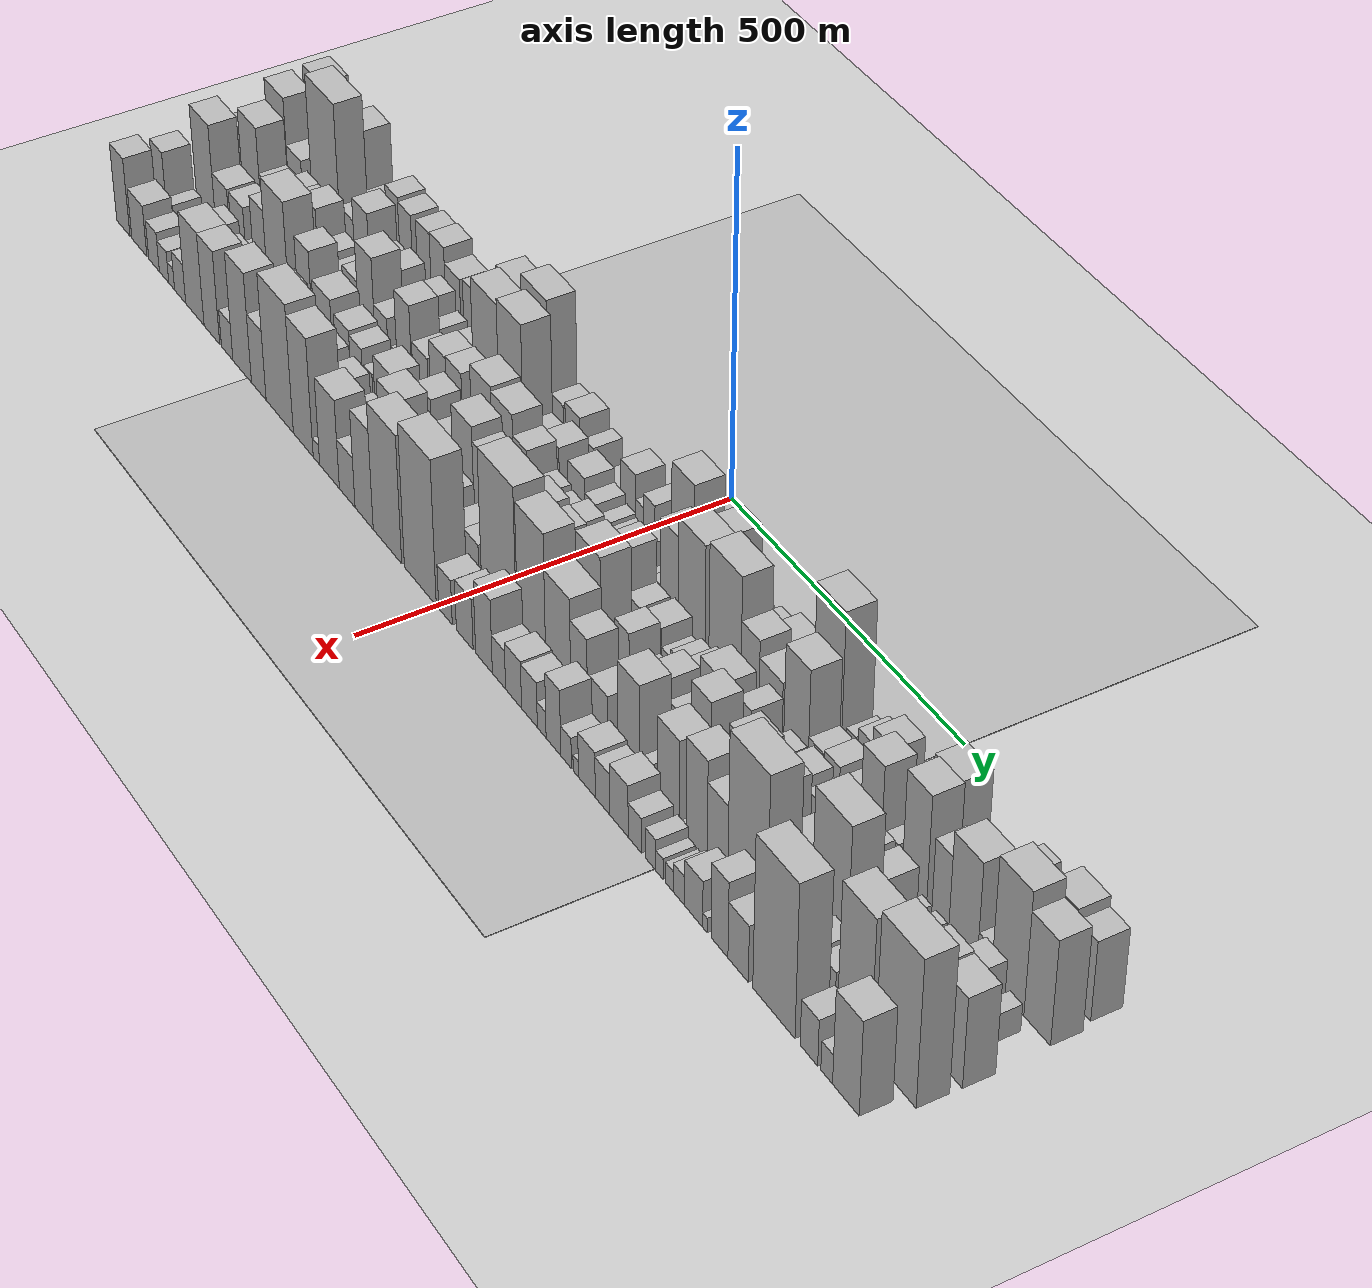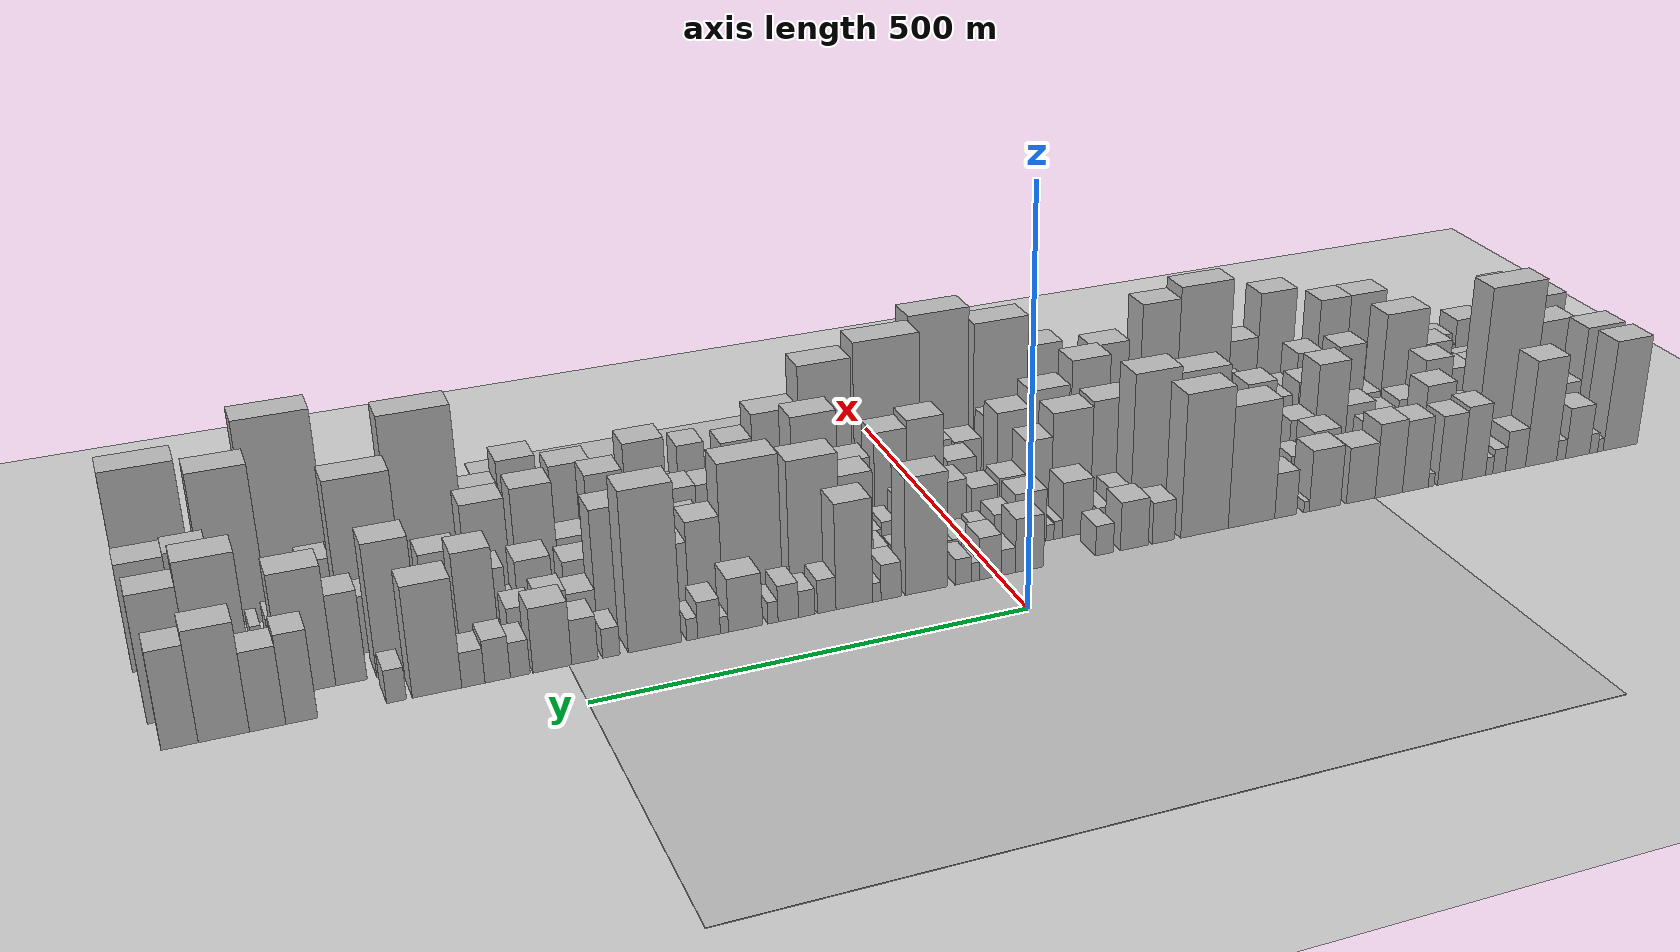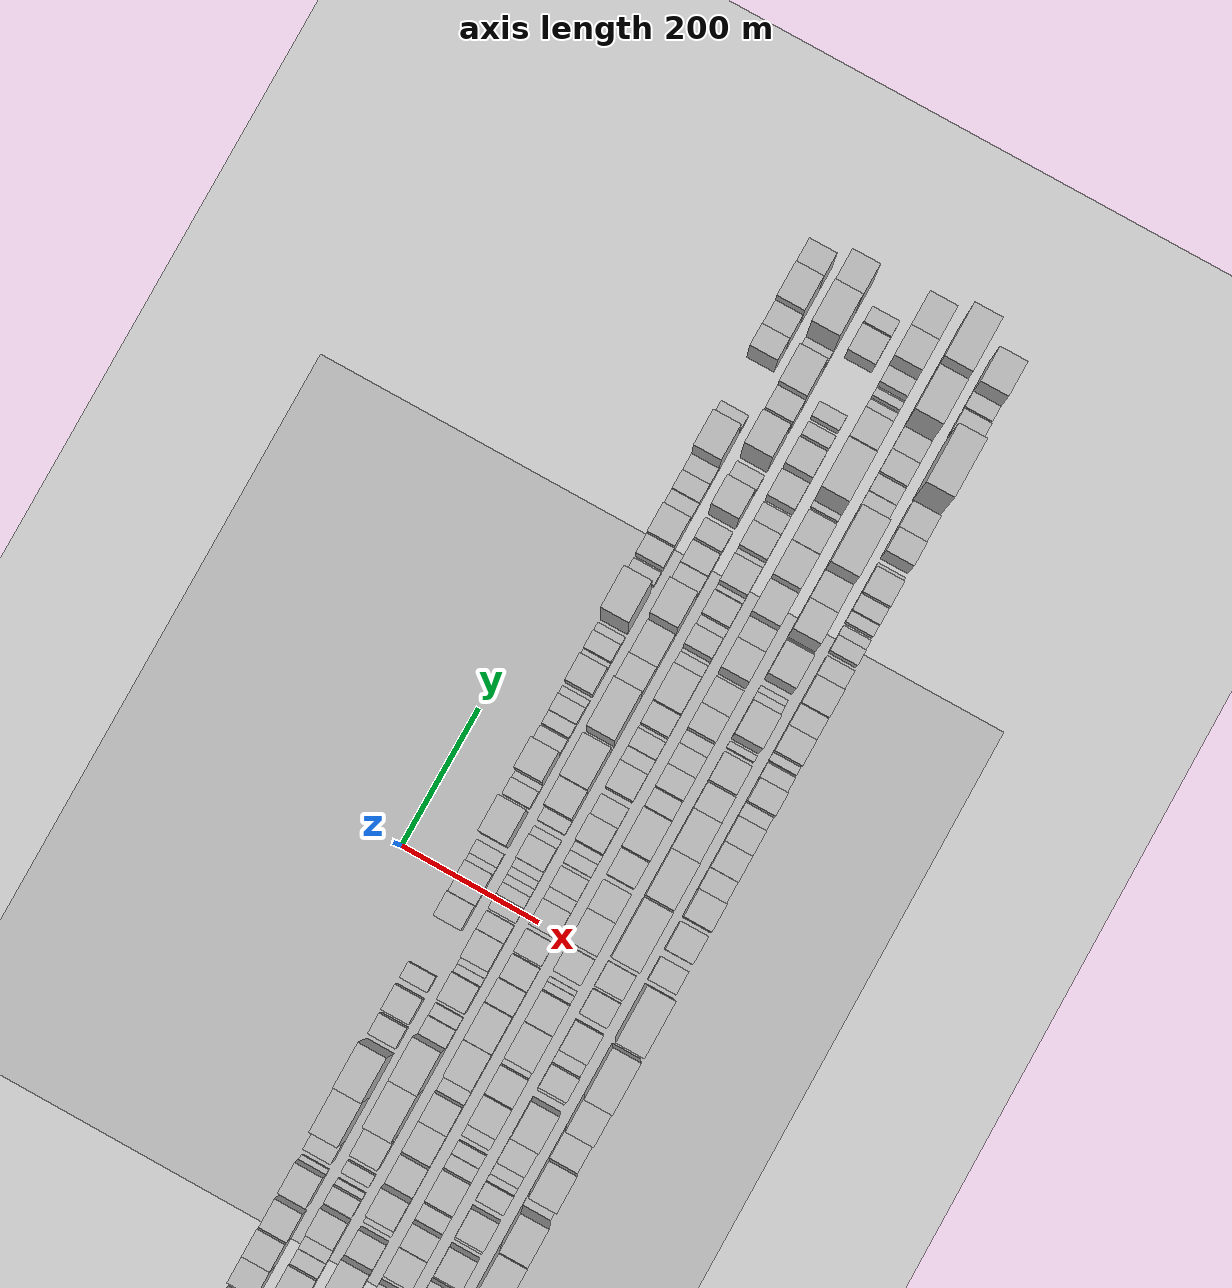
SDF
<?xml version="1.0" encoding="utf-8"?>

<sdf version="1.6">

   <world name="default">

      <gui fullscreen="0">

         <camera name="user_camera">

            <pose>-15 0 4.57585 0 0 0</pose>

            <view_controller>orbit</view_controller>

         </camera>

      </gui>

      <scene>

         <sky>

           <clouds>

             <speed>12</speed>

           </clouds>

         </sky>

         <ambient>0.4 0.4 0.4 1</ambient>

         <background>0.7 0.7 0.7 1</background>

         <shadows>1</shadows>

      </scene>

      <gravity>0 0 -9.8066</gravity>

      <magnetic_field>6e-06 2.3e-05 -4.2e-05</magnetic_field>

      <physics default="0" name="default_physics" type="ode">

         <ode>

            <solver>

               <type>quick</type>

               <iters>10</iters>

               <sor>1.0</sor>

               <use_dynamic_moi_rescaling>0</use_dynamic_moi_rescaling>

            </solver>

            <constraints>

               <cfm>0</cfm>

               <erp>0.2</erp>

               <contact_max_correcting_vel>100</contact_max_correcting_vel>

               <contact_surface_layer>0.001</contact_surface_layer>

            </constraints>

         </ode>

         <max_step_size>0.004</max_step_size>

         <real_time_factor>1</real_time_factor>

         <real_time_update_rate>250</real_time_update_rate>

      </physics>

      <light name="sun" type="directional">

         <cast_shadows>1</cast_shadows>

         <pose>0 0 10 0 0 0</pose>

         <diffuse>0.8 0.8 0.8 1</diffuse>

         <specular>0.2 0.2 0.2 1</specular>

         <attenuation>

            <range>1000</range>

            <constant>0.9</constant>

            <linear>0.01</linear>

            <quadratic>0.001</quadratic>

         </attenuation>

         <direction>-0.5 0.1 -0.9</direction>

      </light>

      <include>

         <name>ground_plane_1</name>

         <uri>model://HANNAS_ground_plane</uri>

         <pose>0 0 0  0 0 0</pose>

      </include>

      <include>

         <name>ground_plane_2</name>

         <uri>model://HANNAS_ground_plane</uri>

         <pose>100 0 0  0 0 0</pose>

      </include>

      <model name="building_1">

         <static>1</static>

         <pose frame="">100.0000 -863.5592 0 0.000000 0.000000 0.000000</pose>

         <link name="link">

            <pose frame="">0 0 75.00 0 0 0</pose>

            <collision name="collision">

               <geometry>

                  <box>

                     <size>40.0000 52.8815 150.0000</size>

                  </box>

               </geometry>

               <max_contacts>10</max_contacts>

               <surface>

                  <contact>

                     <ode/>

                  </contact>

                  <bounce/>

                  <friction>

                     <torsional>

                        <ode/>

                     </torsional>

                     <ode/>

                  </friction>

               </surface>

            </collision>

            <visual name="visual">

               <cast_shadows>0</cast_shadows>

               <geometry>

                  <box>

                     <size>40.0000 52.8815 150.0000</size>

                  </box>

               </geometry>

               <material>

                  <script>

                     <uri>model://HANNAS_wall/materials/scripts</uri>

                     <uri>model://HANNAS_wall/materials/textures</uri>

                     <name>vrc/HANNAS_wall</name>

                  </script>

               </material>

            </visual>

            <self_collide>0</self_collide>

            <enable_wind>0</enable_wind>

            <kinematic>0</kinematic>

         </link>

      </model>

      <model name="building_2">

         <static>1</static>

         <pose frame="">100.0000 -832.8739 0 0.000000 0.000000 0.000000</pose>

         <link name="link">

            <pose frame="">0 0 9.00 0 0 0</pose>

            <collision name="collision">

               <geometry>

                  <box>

                     <size>40.0000 8.4891 18.0000</size>

                  </box>

               </geometry>

               <max_contacts>10</max_contacts>

               <surface>

                  <contact>

                     <ode/>

                  </contact>

                  <bounce/>

                  <friction>

                     <torsional>

                        <ode/>

                     </torsional>

                     <ode/>

                  </friction>

               </surface>

            </collision>

            <visual name="visual">

               <cast_shadows>0</cast_shadows>

               <geometry>

                  <box>

                     <size>40.0000 8.4891 18.0000</size>

                  </box>

               </geometry>

               <material>

                  <script>

                     <uri>model://HANNAS_wall/materials/scripts</uri>

                     <uri>model://HANNAS_wall/materials/textures</uri>

                     <name>vrc/HANNAS_wall</name>

                  </script>

               </material>

            </visual>

            <self_collide>0</self_collide>

            <enable_wind>0</enable_wind>

            <kinematic>0</kinematic>

         </link>

      </model>

      <model name="building_3">

         <static>1</static>

         <pose frame="">100.0000 -822.4442 0 0.000000 0.000000 0.000000</pose>

         <link name="link">

            <pose frame="">0 0 13.50 0 0 0</pose>

            <collision name="collision">

               <geometry>

                  <box>

                     <size>40.0000 12.3704 27.0000</size>

                  </box>

               </geometry>

               <max_contacts>10</max_contacts>

               <surface>

                  <contact>

                     <ode/>

                  </contact>

                  <bounce/>

                  <friction>

                     <torsional>

                        <ode/>

                     </torsional>

                     <ode/>

                  </friction>

               </surface>

            </collision>

            <visual name="visual">

               <cast_shadows>0</cast_shadows>

               <geometry>

                  <box>

                     <size>40.0000 12.3704 27.0000</size>

                  </box>

               </geometry>

               <material>

                  <script>

                     <uri>model://HANNAS_wall/materials/scripts</uri>

                     <uri>model://HANNAS_wall/materials/textures</uri>

                     <name>vrc/HANNAS_wall</name>

                  </script>

               </material>

            </visual>

            <self_collide>0</self_collide>

            <enable_wind>0</enable_wind>

            <kinematic>0</kinematic>

         </link>

      </model>

      <model name="building_4">

         <static>1</static>

         <pose frame="">100.0000 -797.8534 0 0.000000 0.000000 0.000000</pose>

         <link name="link">

            <pose frame="">0 0 34.50 0 0 0</pose>

            <collision name="collision">

               <geometry>

                  <box>

                     <size>40.0000 36.8112 69.0000</size>

                  </box>

               </geometry>

               <max_contacts>10</max_contacts>

               <surface>

                  <contact>

                     <ode/>

                  </contact>

                  <bounce/>

                  <friction>

                     <torsional>

                        <ode/>

                     </torsional>

                     <ode/>

                  </friction>

               </surface>

            </collision>

            <visual name="visual">

               <cast_shadows>0</cast_shadows>

               <geometry>

                  <box>

                     <size>40.0000 36.8112 69.0000</size>

                  </box>

               </geometry>

               <material>

                  <script>

                     <uri>model://HANNAS_wall/materials/scripts</uri>

                     <uri>model://HANNAS_wall/materials/textures</uri>

                     <name>vrc/HANNAS_wall</name>

                  </script>

               </material>

            </visual>

            <self_collide>0</self_collide>

            <enable_wind>0</enable_wind>

            <kinematic>0</kinematic>

         </link>

      </model>

      <model name="building_5">

         <static>1</static>

         <pose frame="">100.0000 -772.7237 0 0.000000 0.000000 0.000000</pose>

         <link name="link">

            <pose frame="">0 0 13.50 0 0 0</pose>

            <collision name="collision">

               <geometry>

                  <box>

                     <size>40.0000 13.4483 27.0000</size>

                  </box>

               </geometry>

               <max_contacts>10</max_contacts>

               <surface>

                  <contact>

                     <ode/>

                  </contact>

                  <bounce/>

                  <friction>

                     <torsional>

                        <ode/>

                     </torsional>

                     <ode/>

                  </friction>

               </surface>

            </collision>

            <visual name="visual">

               <cast_shadows>0</cast_shadows>

               <geometry>

                  <box>

                     <size>40.0000 13.4483 27.0000</size>

                  </box>

               </geometry>

               <material>

                  <script>

                     <uri>model://HANNAS_wall/materials/scripts</uri>

                     <uri>model://HANNAS_wall/materials/textures</uri>

                     <name>vrc/HANNAS_wall</name>

                  </script>

               </material>

            </visual>

            <self_collide>0</self_collide>

            <enable_wind>0</enable_wind>

            <kinematic>0</kinematic>

         </link>

      </model>

      <model name="building_6">

         <static>1</static>

         <pose frame="">100.0000 -742.6112 0 0.000000 0.000000 0.000000</pose>

         <link name="link">

            <pose frame="">0 0 72.00 0 0 0</pose>

            <collision name="collision">

               <geometry>

                  <box>

                     <size>40.0000 46.7767 144.0000</size>

                  </box>

               </geometry>

               <max_contacts>10</max_contacts>

               <surface>

                  <contact>

                     <ode/>

                  </contact>

                  <bounce/>

                  <friction>

                     <torsional>

                        <ode/>

                     </torsional>

                     <ode/>

                  </friction>

               </surface>

            </collision>

            <visual name="visual">

               <cast_shadows>0</cast_shadows>

               <geometry>

                  <box>

                     <size>40.0000 46.7767 144.0000</size>

                  </box>

               </geometry>

               <material>

                  <script>

                     <uri>model://HANNAS_wall/materials/scripts</uri>

                     <uri>model://HANNAS_wall/materials/textures</uri>

                     <name>vrc/HANNAS_wall</name>

                  </script>

               </material>

            </visual>

            <self_collide>0</self_collide>

            <enable_wind>0</enable_wind>

            <kinematic>0</kinematic>

         </link>

      </model>

      <model name="building_7">

         <static>1</static>

         <pose frame="">100.0000 -704.1414 0 0.000000 0.000000 0.000000</pose>

         <link name="link">

            <pose frame="">0 0 27.00 0 0 0</pose>

            <collision name="collision">

               <geometry>

                  <box>

                     <size>40.0000 30.1628 54.0000</size>

                  </box>

               </geometry>

               <max_contacts>10</max_contacts>

               <surface>

                  <contact>

                     <ode/>

                  </contact>

                  <bounce/>

                  <friction>

                     <torsional>

                        <ode/>

                     </torsional>

                     <ode/>

                  </friction>

               </surface>

            </collision>

            <visual name="visual">

               <cast_shadows>0</cast_shadows>

               <geometry>

                  <box>

                     <size>40.0000 30.1628 54.0000</size>

                  </box>

               </geometry>

               <material>

                  <script>

                     <uri>model://HANNAS_wall/materials/scripts</uri>

                     <uri>model://HANNAS_wall/materials/textures</uri>

                     <name>vrc/HANNAS_wall</name>

                  </script>

               </material>

            </visual>

            <self_collide>0</self_collide>

            <enable_wind>0</enable_wind>

            <kinematic>0</kinematic>

         </link>

      </model>

      <model name="building_8">

         <static>1</static>

         <pose frame="">100.0000 -679.7292 0 0.000000 0.000000 0.000000</pose>

         <link name="link">

            <pose frame="">0 0 16.50 0 0 0</pose>

            <collision name="collision">

               <geometry>

                  <box>

                     <size>40.0000 18.6615 33.0000</size>

                  </box>

               </geometry>

               <max_contacts>10</max_contacts>

               <surface>

                  <contact>

                     <ode/>

                  </contact>

                  <bounce/>

                  <friction>

                     <torsional>

                        <ode/>

                     </torsional>

                     <ode/>

                  </friction>

               </surface>

            </collision>

            <visual name="visual">

               <cast_shadows>0</cast_shadows>

               <geometry>

                  <box>

                     <size>40.0000 18.6615 33.0000</size>

                  </box>

               </geometry>

               <material>

                  <script>

                     <uri>model://HANNAS_wall/materials/scripts</uri>

                     <uri>model://HANNAS_wall/materials/textures</uri>

                     <name>vrc/HANNAS_wall</name>

                  </script>

               </material>

            </visual>

            <self_collide>0</self_collide>

            <enable_wind>0</enable_wind>

            <kinematic>0</kinematic>

         </link>

      </model>

      <model name="building_9">

         <static>1</static>

         <pose frame="">100.0000 -665.0958 0 0.000000 0.000000 0.000000</pose>

         <link name="link">

            <pose frame="">0 0 12.00 0 0 0</pose>

            <collision name="collision">

               <geometry>

                  <box>

                     <size>40.0000 10.6054 24.0000</size>

                  </box>

               </geometry>

               <max_contacts>10</max_contacts>

               <surface>

                  <contact>

                     <ode/>

                  </contact>

                  <bounce/>

                  <friction>

                     <torsional>

                        <ode/>

                     </torsional>

                     <ode/>

                  </friction>

               </surface>

            </collision>

            <visual name="visual">

               <cast_shadows>0</cast_shadows>

               <geometry>

                  <box>

                     <size>40.0000 10.6054 24.0000</size>

                  </box>

               </geometry>

               <material>

                  <script>

                     <uri>model://HANNAS_wall/materials/scripts</uri>

                     <uri>model://HANNAS_wall/materials/textures</uri>

                     <name>vrc/HANNAS_wall</name>

                  </script>

               </material>

            </visual>

            <self_collide>0</self_collide>

            <enable_wind>0</enable_wind>

            <kinematic>0</kinematic>

         </link>

      </model>

      <model name="building_10">

         <static>1</static>

         <pose frame="">100.0000 -642.4556 0 0.000000 0.000000 0.000000</pose>

         <link name="link">

            <pose frame="">0 0 49.50 0 0 0</pose>

            <collision name="collision">

               <geometry>

                  <box>

                     <size>40.0000 34.6750 99.0000</size>

                  </box>

               </geometry>

               <max_contacts>10</max_contacts>

               <surface>

                  <contact>

                     <ode/>

                  </contact>

                  <bounce/>

                  <friction>

                     <torsional>

                        <ode/>

                     </torsional>

                     <ode/>

                  </friction>

               </surface>

            </collision>

            <visual name="visual">

               <cast_shadows>0</cast_shadows>

               <geometry>

                  <box>

                     <size>40.0000 34.6750 99.0000</size>

                  </box>

               </geometry>

               <material>

                  <script>

                     <uri>model://HANNAS_wall/materials/scripts</uri>

                     <uri>model://HANNAS_wall/materials/textures</uri>

                     <name>vrc/HANNAS_wall</name>

                  </script>

               </material>

            </visual>

            <self_collide>0</self_collide>

            <enable_wind>0</enable_wind>

            <kinematic>0</kinematic>

         </link>

      </model>

      <model name="building_11">

         <static>1</static>

         <pose frame="">100.0000 -607.3958 0 0.000000 0.000000 0.000000</pose>

         <link name="link">

            <pose frame="">0 0 46.50 0 0 0</pose>

            <collision name="collision">

               <geometry>

                  <box>

                     <size>40.0000 35.4446 93.0000</size>

                  </box>

               </geometry>

               <max_contacts>10</max_contacts>

               <surface>

                  <contact>

                     <ode/>

                  </contact>

                  <bounce/>

                  <friction>

                     <torsional>

                        <ode/>

                     </torsional>

                     <ode/>

                  </friction>

               </surface>

            </collision>

            <visual name="visual">

               <cast_shadows>0</cast_shadows>

               <geometry>

                  <box>

                     <size>40.0000 35.4446 93.0000</size>

                  </box>

               </geometry>

               <material>

                  <script>

                     <uri>model://HANNAS_wall/materials/scripts</uri>

                     <uri>model://HANNAS_wall/materials/textures</uri>

                     <name>vrc/HANNAS_wall</name>

                  </script>

               </material>

            </visual>

            <self_collide>0</self_collide>

            <enable_wind>0</enable_wind>

            <kinematic>0</kinematic>

         </link>

      </model>

      <model name="building_12">

         <static>1</static>

         <pose frame="">100.0000 -580.3775 0 0.000000 0.000000 0.000000</pose>

         <link name="link">

            <pose frame="">0 0 9.00 0 0 0</pose>

            <collision name="collision">

               <geometry>

                  <box>

                     <size>40.0000 8.5919 18.0000</size>

                  </box>

               </geometry>

               <max_contacts>10</max_contacts>

               <surface>

                  <contact>

                     <ode/>

                  </contact>

                  <bounce/>

                  <friction>

                     <torsional>

                        <ode/>

                     </torsional>

                     <ode/>

                  </friction>

               </surface>

            </collision>

            <visual name="visual">

               <cast_shadows>0</cast_shadows>

               <geometry>

                  <box>

                     <size>40.0000 8.5919 18.0000</size>

                  </box>

               </geometry>

               <material>

                  <script>

                     <uri>model://HANNAS_wall/materials/scripts</uri>

                     <uri>model://HANNAS_wall/materials/textures</uri>

                     <name>vrc/HANNAS_wall</name>

                  </script>

               </material>

            </visual>

            <self_collide>0</self_collide>

            <enable_wind>0</enable_wind>

            <kinematic>0</kinematic>

         </link>

      </model>

      <model name="building_13">

         <static>1</static>

         <pose frame="">100.0000 -557.4880 0 0.000000 0.000000 0.000000</pose>

         <link name="link">

            <pose frame="">0 0 48.00 0 0 0</pose>

            <collision name="collision">

               <geometry>

                  <box>

                     <size>40.0000 37.1872 96.0000</size>

                  </box>

               </geometry>

               <max_contacts>10</max_contacts>

               <surface>

                  <contact>

                     <ode/>

                  </contact>

                  <bounce/>

                  <friction>

                     <torsional>

                        <ode/>

                     </torsional>

                     <ode/>

                  </friction>

               </surface>

            </collision>

            <visual name="visual">

               <cast_shadows>0</cast_shadows>

               <geometry>

                  <box>

                     <size>40.0000 37.1872 96.0000</size>

                  </box>

               </geometry>

               <material>

                  <script>

                     <uri>model://HANNAS_wall/materials/scripts</uri>

                     <uri>model://HANNAS_wall/materials/textures</uri>

                     <name>vrc/HANNAS_wall</name>

                  </script>

               </material>

            </visual>

            <self_collide>0</self_collide>

            <enable_wind>0</enable_wind>

            <kinematic>0</kinematic>

         </link>

      </model>

      <model name="building_14">

         <static>1</static>

         <pose frame="">100.0000 -519.3972 0 0.000000 0.000000 0.000000</pose>

         <link name="link">

            <pose frame="">0 0 49.50 0 0 0</pose>

            <collision name="collision">

               <geometry>

                  <box>

                     <size>40.0000 38.9944 99.0000</size>

                  </box>

               </geometry>

               <max_contacts>10</max_contacts>

               <surface>

                  <contact>

                     <ode/>

                  </contact>

                  <bounce/>

                  <friction>

                     <torsional>

                        <ode/>

                     </torsional>

                     <ode/>

                  </friction>

               </surface>

            </collision>

            <visual name="visual">

               <cast_shadows>0</cast_shadows>

               <geometry>

                  <box>

                     <size>40.0000 38.9944 99.0000</size>

                  </box>

               </geometry>

               <material>

                  <script>

                     <uri>model://HANNAS_wall/materials/scripts</uri>

                     <uri>model://HANNAS_wall/materials/textures</uri>

                     <name>vrc/HANNAS_wall</name>

                  </script>

               </material>

            </visual>

            <self_collide>0</self_collide>

            <enable_wind>0</enable_wind>

            <kinematic>0</kinematic>

         </link>

      </model>

      <model name="building_15">

         <static>1</static>

         <pose frame="">100.0000 -479.6449 0 0.000000 0.000000 0.000000</pose>

         <link name="link">

            <pose frame="">0 0 37.50 0 0 0</pose>

            <collision name="collision">

               <geometry>

                  <box>

                     <size>40.0000 40.5102 75.0000</size>

                  </box>

               </geometry>

               <max_contacts>10</max_contacts>

               <surface>

                  <contact>

                     <ode/>

                  </contact>

                  <bounce/>

                  <friction>

                     <torsional>

                        <ode/>

                     </torsional>

                     <ode/>

                  </friction>

               </surface>

            </collision>

            <visual name="visual">

               <cast_shadows>0</cast_shadows>

               <geometry>

                  <box>

                     <size>40.0000 40.5102 75.0000</size>

                  </box>

               </geometry>

               <material>

                  <script>

                     <uri>model://HANNAS_wall/materials/scripts</uri>

                     <uri>model://HANNAS_wall/materials/textures</uri>

                     <name>vrc/HANNAS_wall</name>

                  </script>

               </material>

            </visual>

            <self_collide>0</self_collide>

            <enable_wind>0</enable_wind>

            <kinematic>0</kinematic>

         </link>

      </model>

      <model name="building_16">

         <static>1</static>

         <pose frame="">100.0000 -429.4630 0 0.000000 0.000000 0.000000</pose>

         <link name="link">

            <pose frame="">0 0 40.50 0 0 0</pose>

            <collision name="collision">

               <geometry>

                  <box>

                     <size>40.0000 43.8536 81.0000</size>

                  </box>

               </geometry>

               <max_contacts>10</max_contacts>

               <surface>

                  <contact>

                     <ode/>

                  </contact>

                  <bounce/>

                  <friction>

                     <torsional>

                        <ode/>

                     </torsional>

                     <ode/>

                  </friction>

               </surface>

            </collision>

            <visual name="visual">

               <cast_shadows>0</cast_shadows>

               <geometry>

                  <box>

                     <size>40.0000 43.8536 81.0000</size>

                  </box>

               </geometry>

               <material>

                  <script>

                     <uri>model://HANNAS_wall/materials/scripts</uri>

                     <uri>model://HANNAS_wall/materials/textures</uri>

                     <name>vrc/HANNAS_wall</name>

                  </script>

               </material>

            </visual>

            <self_collide>0</self_collide>

            <enable_wind>0</enable_wind>

            <kinematic>0</kinematic>

         </link>

      </model>

      <model name="building_17">

         <static>1</static>

         <pose frame="">100.0000 -403.8971 0 0.000000 0.000000 0.000000</pose>

         <link name="link">

            <pose frame="">0 0 7.50 0 0 0</pose>

            <collision name="collision">

               <geometry>

                  <box>

                     <size>40.0000 7.2782 15.0000</size>

                  </box>

               </geometry>

               <max_contacts>10</max_contacts>

               <surface>

                  <contact>

                     <ode/>

                  </contact>

                  <bounce/>

                  <friction>

                     <torsional>

                        <ode/>

                     </torsional>

                     <ode/>

                  </friction>

               </surface>

            </collision>

            <visual name="visual">

               <cast_shadows>0</cast_shadows>

               <geometry>

                  <box>

                     <size>40.0000 7.2782 15.0000</size>

                  </box>

               </geometry>

               <material>

                  <script>

                     <uri>model://HANNAS_wall/materials/scripts</uri>

                     <uri>model://HANNAS_wall/materials/textures</uri>

                     <name>vrc/HANNAS_wall</name>

                  </script>

               </material>

            </visual>

            <self_collide>0</self_collide>

            <enable_wind>0</enable_wind>

            <kinematic>0</kinematic>

         </link>

      </model>

      <model name="building_18">

         <static>1</static>

         <pose frame="">100.0000 -375.1844 0 0.000000 0.000000 0.000000</pose>

         <link name="link">

            <pose frame="">0 0 30.00 0 0 0</pose>

            <collision name="collision">

               <geometry>

                  <box>

                     <size>40.0000 30.1471 60.0000</size>

                  </box>

               </geometry>

               <max_contacts>10</max_contacts>

               <surface>

                  <contact>

                     <ode/>

                  </contact>

                  <bounce/>

                  <friction>

                     <torsional>

                        <ode/>

                     </torsional>

                     <ode/>

                  </friction>

               </surface>

            </collision>

            <visual name="visual">

               <cast_shadows>0</cast_shadows>

               <geometry>

                  <box>

                     <size>40.0000 30.1471 60.0000</size>

                  </box>

               </geometry>

               <material>

                  <script>

                     <uri>model://HANNAS_wall/materials/scripts</uri>

                     <uri>model://HANNAS_wall/materials/textures</uri>

                     <name>vrc/HANNAS_wall</name>

                  </script>

               </material>

            </visual>

            <self_collide>0</self_collide>

            <enable_wind>0</enable_wind>

            <kinematic>0</kinematic>

         </link>

      </model>

      <model name="building_19">

         <static>1</static>

         <pose frame="">100.0000 -328.5099 0 0.000000 0.000000 0.000000</pose>

         <link name="link">

            <pose frame="">0 0 79.50 0 0 0</pose>

            <collision name="collision">

               <geometry>

                  <box>

                     <size>40.0000 63.2020 159.0000</size>

                  </box>

               </geometry>

               <max_contacts>10</max_contacts>

               <surface>

                  <contact>

                     <ode/>

                  </contact>

                  <bounce/>

                  <friction>

                     <torsional>

                        <ode/>

                     </torsional>

                     <ode/>

                  </friction>

               </surface>

            </collision>

            <visual name="visual">

               <cast_shadows>0</cast_shadows>

               <geometry>

                  <box>

                     <size>40.0000 63.2020 159.0000</size>

                  </box>

               </geometry>

               <material>

                  <script>

                     <uri>model://HANNAS_wall/materials/scripts</uri>

                     <uri>model://HANNAS_wall/materials/textures</uri>

                     <name>vrc/HANNAS_wall</name>

                  </script>

               </material>

            </visual>

            <self_collide>0</self_collide>

            <enable_wind>0</enable_wind>

            <kinematic>0</kinematic>

         </link>

      </model>

      <model name="building_20">

         <static>1</static>

         <pose frame="">100.0000 -265.2148 0 0.000000 0.000000 0.000000</pose>

         <link name="link">

            <pose frame="">0 0 93.00 0 0 0</pose>

            <collision name="collision">

               <geometry>

                  <box>

                     <size>40.0000 63.3882 186.0000</size>

                  </box>

               </geometry>

               <max_contacts>10</max_contacts>

               <surface>

                  <contact>

                     <ode/>

                  </contact>

                  <bounce/>

                  <friction>

                     <torsional>

                        <ode/>

                     </torsional>

                     <ode/>

                  </friction>

               </surface>

            </collision>

            <visual name="visual">

               <cast_shadows>0</cast_shadows>

               <geometry>

                  <box>

                     <size>40.0000 63.3882 186.0000</size>

                  </box>

               </geometry>

               <material>

                  <script>

                     <uri>model://HANNAS_wall/materials/scripts</uri>

                     <uri>model://HANNAS_wall/materials/textures</uri>

                     <name>vrc/HANNAS_wall</name>

                  </script>

               </material>

            </visual>

            <self_collide>0</self_collide>

            <enable_wind>0</enable_wind>

            <kinematic>0</kinematic>

         </link>

      </model>

      <model name="building_21">

         <static>1</static>

         <pose frame="">100.0000 -210.6596 0 0.000000 0.000000 0.000000</pose>

         <link name="link">

            <pose frame="">0 0 27.00 0 0 0</pose>

            <collision name="collision">

               <geometry>

                  <box>

                     <size>40.0000 29.7221 54.0000</size>

                  </box>

               </geometry>

               <max_contacts>10</max_contacts>

               <surface>

                  <contact>

                     <ode/>

                  </contact>

                  <bounce/>

                  <friction>

                     <torsional>

                        <ode/>

                     </torsional>

                     <ode/>

                  </friction>

               </surface>

            </collision>

            <visual name="visual">

               <cast_shadows>0</cast_shadows>

               <geometry>

                  <box>

                     <size>40.0000 29.7221 54.0000</size>

                  </box>

               </geometry>

               <material>

                  <script>

                     <uri>model://HANNAS_wall/materials/scripts</uri>

                     <uri>model://HANNAS_wall/materials/textures</uri>

                     <name>vrc/HANNAS_wall</name>

                  </script>

               </material>

            </visual>

            <self_collide>0</self_collide>

            <enable_wind>0</enable_wind>

            <kinematic>0</kinematic>

         </link>

      </model>

      <model name="building_22">

         <static>1</static>

         <pose frame="">100.0000 -172.5500 0 0.000000 0.000000 0.000000</pose>

         <link name="link">

            <pose frame="">0 0 31.50 0 0 0</pose>

            <collision name="collision">

               <geometry>

                  <box>

                     <size>40.0000 36.4971 63.0000</size>

                  </box>

               </geometry>

               <max_contacts>10</max_contacts>

               <surface>

                  <contact>

                     <ode/>

                  </contact>

                  <bounce/>

                  <friction>

                     <torsional>

                        <ode/>

                     </torsional>

                     <ode/>

                  </friction>

               </surface>

            </collision>

            <visual name="visual">

               <cast_shadows>0</cast_shadows>

               <geometry>

                  <box>

                     <size>40.0000 36.4971 63.0000</size>

                  </box>

               </geometry>

               <material>

                  <script>

                     <uri>model://HANNAS_wall/materials/scripts</uri>

                     <uri>model://HANNAS_wall/materials/textures</uri>

                     <name>vrc/HANNAS_wall</name>

                  </script>

               </material>

            </visual>

            <self_collide>0</self_collide>

            <enable_wind>0</enable_wind>

            <kinematic>0</kinematic>

         </link>

      </model>

      <model name="building_23">

         <static>1</static>

         <pose frame="">100.0000 -133.8058 0 0.000000 0.000000 0.000000</pose>

         <link name="link">

            <pose frame="">0 0 19.50 0 0 0</pose>

            <collision name="collision">

               <geometry>

                  <box>

                     <size>40.0000 22.9913 39.0000</size>

                  </box>

               </geometry>

               <max_contacts>10</max_contacts>

               <surface>

                  <contact>

                     <ode/>

                  </contact>

                  <bounce/>

                  <friction>

                     <torsional>

                        <ode/>

                     </torsional>

                     <ode/>

                  </friction>

               </surface>

            </collision>

            <visual name="visual">

               <cast_shadows>0</cast_shadows>

               <geometry>

                  <box>

                     <size>40.0000 22.9913 39.0000</size>

                  </box>

               </geometry>

               <material>

                  <script>

                     <uri>model://HANNAS_wall/materials/scripts</uri>

                     <uri>model://HANNAS_wall/materials/textures</uri>

                     <name>vrc/HANNAS_wall</name>

                  </script>

               </material>

            </visual>

            <self_collide>0</self_collide>

            <enable_wind>0</enable_wind>

            <kinematic>0</kinematic>

         </link>

      </model>

      <model name="building_24">

         <static>1</static>

         <pose frame="">100.0000 -38.3105 0 0.000000 0.000000 0.000000</pose>

         <link name="link">

            <pose frame="">0 0 34.50 0 0 0</pose>

            <collision name="collision">

               <geometry>

                  <box>

                     <size>40.0000 35.3331 69.0000</size>

                  </box>

               </geometry>

               <max_contacts>10</max_contacts>

               <surface>

                  <contact>

                     <ode/>

                  </contact>

                  <bounce/>

                  <friction>

                     <torsional>

                        <ode/>

                     </torsional>

                     <ode/>

                  </friction>

               </surface>

            </collision>

            <visual name="visual">

               <cast_shadows>0</cast_shadows>

               <geometry>

                  <box>

                     <size>40.0000 35.3331 69.0000</size>

                  </box>

               </geometry>

               <material>

                  <script>

                     <uri>model://HANNAS_wall/materials/scripts</uri>

                     <uri>model://HANNAS_wall/materials/textures</uri>

                     <name>vrc/HANNAS_wall</name>

                  </script>

               </material>

            </visual>

            <self_collide>0</self_collide>

            <enable_wind>0</enable_wind>

            <kinematic>0</kinematic>

         </link>

      </model>

      <model name="building_25">

         <static>1</static>

         <pose frame="">100.0000 -11.7626 0 0.000000 0.000000 0.000000</pose>

         <link name="link">

            <pose frame="">0 0 16.50 0 0 0</pose>

            <collision name="collision">

               <geometry>

                  <box>

                     <size>40.0000 17.7626 33.0000</size>

                  </box>

               </geometry>

               <max_contacts>10</max_contacts>

               <surface>

                  <contact>

                     <ode/>

                  </contact>

                  <bounce/>

                  <friction>

                     <torsional>

                        <ode/>

                     </torsional>

                     <ode/>

                  </friction>

               </surface>

            </collision>

            <visual name="visual">

               <cast_shadows>0</cast_shadows>

               <geometry>

                  <box>

                     <size>40.0000 17.7626 33.0000</size>

                  </box>

               </geometry>

               <material>

                  <script>

                     <uri>model://HANNAS_wall/materials/scripts</uri>

                     <uri>model://HANNAS_wall/materials/textures</uri>

                     <name>vrc/HANNAS_wall</name>

                  </script>

               </material>

            </visual>

            <self_collide>0</self_collide>

            <enable_wind>0</enable_wind>

            <kinematic>0</kinematic>

         </link>

      </model>

      <model name="building_26">

         <static>1</static>

         <pose frame="">100.0000 10.8010 0 0.000000 0.000000 0.000000</pose>

         <link name="link">

            <pose frame="">0 0 27.00 0 0 0</pose>

            <collision name="collision">

               <geometry>

                  <box>

                     <size>40.0000 27.3646 54.0000</size>

                  </box>

               </geometry>

               <max_contacts>10</max_contacts>

               <surface>

                  <contact>

                     <ode/>

                  </contact>

                  <bounce/>

                  <friction>

                     <torsional>

                        <ode/>

                     </torsional>

                     <ode/>

                  </friction>

               </surface>

            </collision>

            <visual name="visual">

               <cast_shadows>0</cast_shadows>

               <geometry>

                  <box>

                     <size>40.0000 27.3646 54.0000</size>

                  </box>

               </geometry>

               <material>

                  <script>

                     <uri>model://HANNAS_wall/materials/scripts</uri>

                     <uri>model://HANNAS_wall/materials/textures</uri>

                     <name>vrc/HANNAS_wall</name>

                  </script>

               </material>

            </visual>

            <self_collide>0</self_collide>

            <enable_wind>0</enable_wind>

            <kinematic>0</kinematic>

         </link>

      </model>

      <model name="building_27">

         <static>1</static>

         <pose frame="">100.0000 29.5351 0 0.000000 0.000000 0.000000</pose>

         <link name="link">

            <pose frame="">0 0 12.00 0 0 0</pose>

            <collision name="collision">

               <geometry>

                  <box>

                     <size>40.0000 10.1037 24.0000</size>

                  </box>

               </geometry>

               <max_contacts>10</max_contacts>

               <surface>

                  <contact>

                     <ode/>

                  </contact>

                  <bounce/>

                  <friction>

                     <torsional>

                        <ode/>

                     </torsional>

                     <ode/>

                  </friction>

               </surface>

            </collision>

            <visual name="visual">

               <cast_shadows>0</cast_shadows>

               <geometry>

                  <box>

                     <size>40.0000 10.1037 24.0000</size>

                  </box>

               </geometry>

               <material>

                  <script>

                     <uri>model://HANNAS_wall/materials/scripts</uri>

                     <uri>model://HANNAS_wall/materials/textures</uri>

                     <name>vrc/HANNAS_wall</name>

                  </script>

               </material>

            </visual>

            <self_collide>0</self_collide>

            <enable_wind>0</enable_wind>

            <kinematic>0</kinematic>

         </link>

      </model>

      <model name="building_28">

         <static>1</static>

         <pose frame="">100.0000 44.4117 0 0.000000 0.000000 0.000000</pose>

         <link name="link">

            <pose frame="">0 0 16.50 0 0 0</pose>

            <collision name="collision">

               <geometry>

                  <box>

                     <size>40.0000 19.6494 33.0000</size>

                  </box>

               </geometry>

               <max_contacts>10</max_contacts>

               <surface>

                  <contact>

                     <ode/>

                  </contact>

                  <bounce/>

                  <friction>

                     <torsional>

                        <ode/>

                     </torsional>

                     <ode/>

                  </friction>

               </surface>

            </collision>

            <visual name="visual">

               <cast_shadows>0</cast_shadows>

               <geometry>

                  <box>

                     <size>40.0000 19.6494 33.0000</size>

                  </box>

               </geometry>

               <material>

                  <script>

                     <uri>model://HANNAS_wall/materials/scripts</uri>

                     <uri>model://HANNAS_wall/materials/textures</uri>

                     <name>vrc/HANNAS_wall</name>

                  </script>

               </material>

            </visual>

            <self_collide>0</self_collide>

            <enable_wind>0</enable_wind>

            <kinematic>0</kinematic>

         </link>

      </model>

      <model name="building_29">

         <static>1</static>

         <pose frame="">100.0000 89.0298 0 0.000000 0.000000 0.000000</pose>

         <link name="link">

            <pose frame="">0 0 73.50 0 0 0</pose>

            <collision name="collision">

               <geometry>

                  <box>

                     <size>40.0000 51.5868 147.0000</size>

                  </box>

               </geometry>

               <max_contacts>10</max_contacts>

               <surface>

                  <contact>

                     <ode/>

                  </contact>

                  <bounce/>

                  <friction>

                     <torsional>

                        <ode/>

                     </torsional>

                     <ode/>

                  </friction>

               </surface>

            </collision>

            <visual name="visual">

               <cast_shadows>0</cast_shadows>

               <geometry>

                  <box>

                     <size>40.0000 51.5868 147.0000</size>

                  </box>

               </geometry>

               <material>

                  <script>

                     <uri>model://HANNAS_wall/materials/scripts</uri>

                     <uri>model://HANNAS_wall/materials/textures</uri>

                     <name>vrc/HANNAS_wall</name>

                  </script>

               </material>

            </visual>

            <self_collide>0</self_collide>

            <enable_wind>0</enable_wind>

            <kinematic>0</kinematic>

         </link>

      </model>

      <model name="building_30">

         <static>1</static>

         <pose frame="">100.0000 131.9228 0 0.000000 0.000000 0.000000</pose>

         <link name="link">

            <pose frame="">0 0 22.50 0 0 0</pose>

            <collision name="collision">

               <geometry>

                  <box>

                     <size>40.0000 24.1992 45.0000</size>

                  </box>

               </geometry>

               <max_contacts>10</max_contacts>

               <surface>

                  <contact>

                     <ode/>

                  </contact>

                  <bounce/>

                  <friction>

                     <torsional>

                        <ode/>

                     </torsional>

                     <ode/>

                  </friction>

               </surface>

            </collision>

            <visual name="visual">

               <cast_shadows>0</cast_shadows>

               <geometry>

                  <box>

                     <size>40.0000 24.1992 45.0000</size>

                  </box>

               </geometry>

               <material>

                  <script>

                     <uri>model://HANNAS_wall/materials/scripts</uri>

                     <uri>model://HANNAS_wall/materials/textures</uri>

                     <name>vrc/HANNAS_wall</name>

                  </script>

               </material>

            </visual>

            <self_collide>0</self_collide>

            <enable_wind>0</enable_wind>

            <kinematic>0</kinematic>

         </link>

      </model>

      <model name="building_31">

         <static>1</static>

         <pose frame="">100.0000 149.0816 0 0.000000 0.000000 0.000000</pose>

         <link name="link">

            <pose frame="">0 0 12.00 0 0 0</pose>

            <collision name="collision">

               <geometry>

                  <box>

                     <size>40.0000 10.1185 24.0000</size>

                  </box>

               </geometry>

               <max_contacts>10</max_contacts>

               <surface>

                  <contact>

                     <ode/>

                  </contact>

                  <bounce/>

                  <friction>

                     <torsional>

                        <ode/>

                     </torsional>

                     <ode/>

                  </friction>

               </surface>

            </collision>

            <visual name="visual">

               <cast_shadows>0</cast_shadows>

               <geometry>

                  <box>

                     <size>40.0000 10.1185 24.0000</size>

                  </box>

               </geometry>

               <material>

                  <script>

                     <uri>model://HANNAS_wall/materials/scripts</uri>

                     <uri>model://HANNAS_wall/materials/textures</uri>

                     <name>vrc/HANNAS_wall</name>

                  </script>

               </material>

            </visual>

            <self_collide>0</self_collide>

            <enable_wind>0</enable_wind>

            <kinematic>0</kinematic>

         </link>

      </model>

      <model name="building_32">

         <static>1</static>

         <pose frame="">100.0000 175.8906 0 0.000000 0.000000 0.000000</pose>

         <link name="link">

            <pose frame="">0 0 66.00 0 0 0</pose>

            <collision name="collision">

               <geometry>

                  <box>

                     <size>40.0000 43.4994 132.0000</size>

                  </box>

               </geometry>

               <max_contacts>10</max_contacts>

               <surface>

                  <contact>

                     <ode/>

                  </contact>

                  <bounce/>

                  <friction>

                     <torsional>

                        <ode/>

                     </torsional>

                     <ode/>

                  </friction>

               </surface>

            </collision>

            <visual name="visual">

               <cast_shadows>0</cast_shadows>

               <geometry>

                  <box>

                     <size>40.0000 43.4994 132.0000</size>

                  </box>

               </geometry>

               <material>

                  <script>

                     <uri>model://HANNAS_wall/materials/scripts</uri>

                     <uri>model://HANNAS_wall/materials/textures</uri>

                     <name>vrc/HANNAS_wall</name>

                  </script>

               </material>

            </visual>

            <self_collide>0</self_collide>

            <enable_wind>0</enable_wind>

            <kinematic>0</kinematic>

         </link>

      </model>

      <model name="building_33">

         <static>1</static>

         <pose frame="">100.0000 208.5232 0 0.000000 0.000000 0.000000</pose>

         <link name="link">

            <pose frame="">0 0 21.00 0 0 0</pose>

            <collision name="collision">

               <geometry>

                  <box>

                     <size>40.0000 21.7659 42.0000</size>

                  </box>

               </geometry>

               <max_contacts>10</max_contacts>

               <surface>

                  <contact>

                     <ode/>

                  </contact>

                  <bounce/>

                  <friction>

                     <torsional>

                        <ode/>

                     </torsional>

                     <ode/>

                  </friction>

               </surface>

            </collision>

            <visual name="visual">

               <cast_shadows>0</cast_shadows>

               <geometry>

                  <box>

                     <size>40.0000 21.7659 42.0000</size>

                  </box>

               </geometry>

               <material>

                  <script>

                     <uri>model://HANNAS_wall/materials/scripts</uri>

                     <uri>model://HANNAS_wall/materials/textures</uri>

                     <name>vrc/HANNAS_wall</name>

                  </script>

               </material>

            </visual>

            <self_collide>0</self_collide>

            <enable_wind>0</enable_wind>

            <kinematic>0</kinematic>

         </link>

      </model>

      <model name="building_34">

         <static>1</static>

         <pose frame="">100.0000 231.9285 0 0.000000 0.000000 0.000000</pose>

         <link name="link">

            <pose frame="">0 0 16.50 0 0 0</pose>

            <collision name="collision">

               <geometry>

                  <box>

                     <size>40.0000 19.0447 33.0000</size>

                  </box>

               </geometry>

               <max_contacts>10</max_contacts>

               <surface>

                  <contact>

                     <ode/>

                  </contact>

                  <bounce/>

                  <friction>

                     <torsional>

                        <ode/>

                     </torsional>

                     <ode/>

                  </friction>

               </surface>

            </collision>

            <visual name="visual">

               <cast_shadows>0</cast_shadows>

               <geometry>

                  <box>

                     <size>40.0000 19.0447 33.0000</size>

                  </box>

               </geometry>

               <material>

                  <script>

                     <uri>model://HANNAS_wall/materials/scripts</uri>

                     <uri>model://HANNAS_wall/materials/textures</uri>

                     <name>vrc/HANNAS_wall</name>

                  </script>

               </material>

            </visual>

            <self_collide>0</self_collide>

            <enable_wind>0</enable_wind>

            <kinematic>0</kinematic>

         </link>

      </model>

      <model name="building_35">

         <static>1</static>

         <pose frame="">100.0000 253.4220 0 0.000000 0.000000 0.000000</pose>

         <link name="link">

            <pose frame="">0 0 22.50 0 0 0</pose>

            <collision name="collision">

               <geometry>

                  <box>

                     <size>40.0000 23.9424 45.0000</size>

                  </box>

               </geometry>

               <max_contacts>10</max_contacts>

               <surface>

                  <contact>

                     <ode/>

                  </contact>

                  <bounce/>

                  <friction>

                     <torsional>

                        <ode/>

                     </torsional>

                     <ode/>

                  </friction>

               </surface>

            </collision>

            <visual name="visual">

               <cast_shadows>0</cast_shadows>

               <geometry>

                  <box>

                     <size>40.0000 23.9424 45.0000</size>

                  </box>

               </geometry>

               <material>

                  <script>

                     <uri>model://HANNAS_wall/materials/scripts</uri>

                     <uri>model://HANNAS_wall/materials/textures</uri>

                     <name>vrc/HANNAS_wall</name>

                  </script>

               </material>

            </visual>

            <self_collide>0</self_collide>

            <enable_wind>0</enable_wind>

            <kinematic>0</kinematic>

         </link>

      </model>

      <model name="building_36">

         <static>1</static>

         <pose frame="">100.0000 271.3329 0 0.000000 0.000000 0.000000</pose>

         <link name="link">

            <pose frame="">0 0 13.50 0 0 0</pose>

            <collision name="collision">

               <geometry>

                  <box>

                     <size>40.0000 11.8794 27.0000</size>

                  </box>

               </geometry>

               <max_contacts>10</max_contacts>

               <surface>

                  <contact>

                     <ode/>

                  </contact>

                  <bounce/>

                  <friction>

                     <torsional>

                        <ode/>

                     </torsional>

                     <ode/>

                  </friction>

               </surface>

            </collision>

            <visual name="visual">

               <cast_shadows>0</cast_shadows>

               <geometry>

                  <box>

                     <size>40.0000 11.8794 27.0000</size>

                  </box>

               </geometry>

               <material>

                  <script>

                     <uri>model://HANNAS_wall/materials/scripts</uri>

                     <uri>model://HANNAS_wall/materials/textures</uri>

                     <name>vrc/HANNAS_wall</name>

                  </script>

               </material>

            </visual>

            <self_collide>0</self_collide>

            <enable_wind>0</enable_wind>

            <kinematic>0</kinematic>

         </link>

      </model>

      <model name="building_37">

         <static>1</static>

         <pose frame="">100.0000 302.8294 0 0.000000 0.000000 0.000000</pose>

         <link name="link">

            <pose frame="">0 0 33.00 0 0 0</pose>

            <collision name="collision">

               <geometry>

                  <box>

                     <size>40.0000 39.1136 66.0000</size>

                  </box>

               </geometry>

               <max_contacts>10</max_contacts>

               <surface>

                  <contact>

                     <ode/>

                  </contact>

                  <bounce/>

                  <friction>

                     <torsional>

                        <ode/>

                     </torsional>

                     <ode/>

                  </friction>

               </surface>

            </collision>

            <visual name="visual">

               <cast_shadows>0</cast_shadows>

               <geometry>

                  <box>

                     <size>40.0000 39.1136 66.0000</size>

                  </box>

               </geometry>

               <material>

                  <script>

                     <uri>model://HANNAS_wall/materials/scripts</uri>

                     <uri>model://HANNAS_wall/materials/textures</uri>

                     <name>vrc/HANNAS_wall</name>

                  </script>

               </material>

            </visual>

            <self_collide>0</self_collide>

            <enable_wind>0</enable_wind>

            <kinematic>0</kinematic>

         </link>

      </model>

      <model name="building_38">

         <static>1</static>

         <pose frame="">100.0000 327.0356 0 0.000000 0.000000 0.000000</pose>

         <link name="link">

            <pose frame="">0 0 10.50 0 0 0</pose>

            <collision name="collision">

               <geometry>

                  <box>

                     <size>40.0000 9.2986 21.0000</size>

                  </box>

               </geometry>

               <max_contacts>10</max_contacts>

               <surface>

                  <contact>

                     <ode/>

                  </contact>

                  <bounce/>

                  <friction>

                     <torsional>

                        <ode/>

                     </torsional>

                     <ode/>

                  </friction>

               </surface>

            </collision>

            <visual name="visual">

               <cast_shadows>0</cast_shadows>

               <geometry>

                  <box>

                     <size>40.0000 9.2986 21.0000</size>

                  </box>

               </geometry>

               <material>

                  <script>

                     <uri>model://HANNAS_wall/materials/scripts</uri>

                     <uri>model://HANNAS_wall/materials/textures</uri>

                     <name>vrc/HANNAS_wall</name>

                  </script>

               </material>

            </visual>

            <self_collide>0</self_collide>

            <enable_wind>0</enable_wind>

            <kinematic>0</kinematic>

         </link>

      </model>

      <model name="building_39">

         <static>1</static>

         <pose frame="">100.0000 344.4830 0 0.000000 0.000000 0.000000</pose>

         <link name="link">

            <pose frame="">0 0 22.50 0 0 0</pose>

            <collision name="collision">

               <geometry>

                  <box>

                     <size>40.0000 25.5962 45.0000</size>

                  </box>

               </geometry>

               <max_contacts>10</max_contacts>

               <surface>

                  <contact>

                     <ode/>

                  </contact>

                  <bounce/>

                  <friction>

                     <torsional>

                        <ode/>

                     </torsional>

                     <ode/>

                  </friction>

               </surface>

            </collision>

            <visual name="visual">

               <cast_shadows>0</cast_shadows>

               <geometry>

                  <box>

                     <size>40.0000 25.5962 45.0000</size>

                  </box>

               </geometry>

               <material>

                  <script>

                     <uri>model://HANNAS_wall/materials/scripts</uri>

                     <uri>model://HANNAS_wall/materials/textures</uri>

                     <name>vrc/HANNAS_wall</name>

                  </script>

               </material>

            </visual>

            <self_collide>0</self_collide>

            <enable_wind>0</enable_wind>

            <kinematic>0</kinematic>

         </link>

      </model>

      <model name="building_40">

         <static>1</static>

         <pose frame="">100.0000 363.4777 0 0.000000 0.000000 0.000000</pose>

         <link name="link">

            <pose frame="">0 0 13.50 0 0 0</pose>

            <collision name="collision">

               <geometry>

                  <box>

                     <size>40.0000 12.3933 27.0000</size>

                  </box>

               </geometry>

               <max_contacts>10</max_contacts>

               <surface>

                  <contact>

                     <ode/>

                  </contact>

                  <bounce/>

                  <friction>

                     <torsional>

                        <ode/>

                     </torsional>

                     <ode/>

                  </friction>

               </surface>

            </collision>

            <visual name="visual">

               <cast_shadows>0</cast_shadows>

               <geometry>

                  <box>

                     <size>40.0000 12.3933 27.0000</size>

                  </box>

               </geometry>

               <material>

                  <script>

                     <uri>model://HANNAS_wall/materials/scripts</uri>

                     <uri>model://HANNAS_wall/materials/textures</uri>

                     <name>vrc/HANNAS_wall</name>

                  </script>

               </material>

            </visual>

            <self_collide>0</self_collide>

            <enable_wind>0</enable_wind>

            <kinematic>0</kinematic>

         </link>

      </model>

      <model name="building_41">

         <static>1</static>

         <pose frame="">100.0000 405.3680 0 0.000000 0.000000 0.000000</pose>

         <link name="link">

            <pose frame="">0 0 97.50 0 0 0</pose>

            <collision name="collision">

               <geometry>

                  <box>

                     <size>40.0000 59.3873 195.0000</size>

                  </box>

               </geometry>

               <max_contacts>10</max_contacts>

               <surface>

                  <contact>

                     <ode/>

                  </contact>

                  <bounce/>

                  <friction>

                     <torsional>

                        <ode/>

                     </torsional>

                     <ode/>

                  </friction>

               </surface>

            </collision>

            <visual name="visual">

               <cast_shadows>0</cast_shadows>

               <geometry>

                  <box>

                     <size>40.0000 59.3873 195.0000</size>

                  </box>

               </geometry>

               <material>

                  <script>

                     <uri>model://HANNAS_wall/materials/scripts</uri>

                     <uri>model://HANNAS_wall/materials/textures</uri>

                     <name>vrc/HANNAS_wall</name>

                  </script>

               </material>

            </visual>

            <self_collide>0</self_collide>

            <enable_wind>0</enable_wind>

            <kinematic>0</kinematic>

         </link>

      </model>

      <model name="building_42">

         <static>1</static>

         <pose frame="">100.0000 453.6295 0 0.000000 0.000000 0.000000</pose>

         <link name="link">

            <pose frame="">0 0 18.00 0 0 0</pose>

            <collision name="collision">

               <geometry>

                  <box>

                     <size>40.0000 19.1355 36.0000</size>

                  </box>

               </geometry>

               <max_contacts>10</max_contacts>

               <surface>

                  <contact>

                     <ode/>

                  </contact>

                  <bounce/>

                  <friction>

                     <torsional>

                        <ode/>

                     </torsional>

                     <ode/>

                  </friction>

               </surface>

            </collision>

            <visual name="visual">

               <cast_shadows>0</cast_shadows>

               <geometry>

                  <box>

                     <size>40.0000 19.1355 36.0000</size>

                  </box>

               </geometry>

               <material>

                  <script>

                     <uri>model://HANNAS_wall/materials/scripts</uri>

                     <uri>model://HANNAS_wall/materials/textures</uri>

                     <name>vrc/HANNAS_wall</name>

                  </script>

               </material>

            </visual>

            <self_collide>0</self_collide>

            <enable_wind>0</enable_wind>

            <kinematic>0</kinematic>

         </link>

      </model>

      <model name="building_43">

         <static>1</static>

         <pose frame="">100.0000 482.5405 0 0.000000 0.000000 0.000000</pose>

         <link name="link">

            <pose frame="">0 0 27.00 0 0 0</pose>

            <collision name="collision">

               <geometry>

                  <box>

                     <size>40.0000 28.6865 54.0000</size>

                  </box>

               </geometry>

               <max_contacts>10</max_contacts>

               <surface>

                  <contact>

                     <ode/>

                  </contact>

                  <bounce/>

                  <friction>

                     <torsional>

                        <ode/>

                     </torsional>

                     <ode/>

                  </friction>

               </surface>

            </collision>

            <visual name="visual">

               <cast_shadows>0</cast_shadows>

               <geometry>

                  <box>

                     <size>40.0000 28.6865 54.0000</size>

                  </box>

               </geometry>

               <material>

                  <script>

                     <uri>model://HANNAS_wall/materials/scripts</uri>

                     <uri>model://HANNAS_wall/materials/textures</uri>

                     <name>vrc/HANNAS_wall</name>

                  </script>

               </material>

            </visual>

            <self_collide>0</self_collide>

            <enable_wind>0</enable_wind>

            <kinematic>0</kinematic>

         </link>

      </model>

      <model name="building_44">

         <static>1</static>

         <pose frame="">100.0000 517.8508 0 0.000000 0.000000 0.000000</pose>

         <link name="link">

            <pose frame="">0 0 39.00 0 0 0</pose>

            <collision name="collision">

               <geometry>

                  <box>

                     <size>40.0000 41.9341 78.0000</size>

                  </box>

               </geometry>

               <max_contacts>10</max_contacts>

               <surface>

                  <contact>

                     <ode/>

                  </contact>

                  <bounce/>

                  <friction>

                     <torsional>

                        <ode/>

                     </torsional>

                     <ode/>

                  </friction>

               </surface>

            </collision>

            <visual name="visual">

               <cast_shadows>0</cast_shadows>

               <geometry>

                  <box>

                     <size>40.0000 41.9341 78.0000</size>

                  </box>

               </geometry>

               <material>

                  <script>

                     <uri>model://HANNAS_wall/materials/scripts</uri>

                     <uri>model://HANNAS_wall/materials/textures</uri>

                     <name>vrc/HANNAS_wall</name>

                  </script>

               </material>

            </visual>

            <self_collide>0</self_collide>

            <enable_wind>0</enable_wind>

            <kinematic>0</kinematic>

         </link>

      </model>

      <model name="building_45">

         <static>1</static>

         <pose frame="">100.0000 552.3802 0 0.000000 0.000000 0.000000</pose>

         <link name="link">

            <pose frame="">0 0 21.00 0 0 0</pose>

            <collision name="collision">

               <geometry>

                  <box>

                     <size>40.0000 21.1246 42.0000</size>

                  </box>

               </geometry>

               <max_contacts>10</max_contacts>

               <surface>

                  <contact>

                     <ode/>

                  </contact>

                  <bounce/>

                  <friction>

                     <torsional>

                        <ode/>

                     </torsional>

                     <ode/>

                  </friction>

               </surface>

            </collision>

            <visual name="visual">

               <cast_shadows>0</cast_shadows>

               <geometry>

                  <box>

                     <size>40.0000 21.1246 42.0000</size>

                  </box>

               </geometry>

               <material>

                  <script>

                     <uri>model://HANNAS_wall/materials/scripts</uri>

                     <uri>model://HANNAS_wall/materials/textures</uri>

                     <name>vrc/HANNAS_wall</name>

                  </script>

               </material>

            </visual>

            <self_collide>0</self_collide>

            <enable_wind>0</enable_wind>

            <kinematic>0</kinematic>

         </link>

      </model>

      <model name="building_46">

         <static>1</static>

         <pose frame="">100.0000 576.4382 0 0.000000 0.000000 0.000000</pose>

         <link name="link">

            <pose frame="">0 0 25.50 0 0 0</pose>

            <collision name="collision">

               <geometry>

                  <box>

                     <size>40.0000 26.9914 51.0000</size>

                  </box>

               </geometry>

               <max_contacts>10</max_contacts>

               <surface>

                  <contact>

                     <ode/>

                  </contact>

                  <bounce/>

                  <friction>

                     <torsional>

                        <ode/>

                     </torsional>

                     <ode/>

                  </friction>

               </surface>

            </collision>

            <visual name="visual">

               <cast_shadows>0</cast_shadows>

               <geometry>

                  <box>

                     <size>40.0000 26.9914 51.0000</size>

                  </box>

               </geometry>

               <material>

                  <script>

                     <uri>model://HANNAS_wall/materials/scripts</uri>

                     <uri>model://HANNAS_wall/materials/textures</uri>

                     <name>vrc/HANNAS_wall</name>

                  </script>

               </material>

            </visual>

            <self_collide>0</self_collide>

            <enable_wind>0</enable_wind>

            <kinematic>0</kinematic>

         </link>

      </model>

      <model name="building_47">

         <static>1</static>

         <pose frame="">100.0000 602.1581 0 0.000000 0.000000 0.000000</pose>

         <link name="link">

            <pose frame="">0 0 21.00 0 0 0</pose>

            <collision name="collision">

               <geometry>

                  <box>

                     <size>40.0000 24.4485 42.0000</size>

                  </box>

               </geometry>

               <max_contacts>10</max_contacts>

               <surface>

                  <contact>

                     <ode/>

                  </contact>

                  <bounce/>

                  <friction>

                     <torsional>

                        <ode/>

                     </torsional>

                     <ode/>

                  </friction>

               </surface>

            </collision>

            <visual name="visual">

               <cast_shadows>0</cast_shadows>

               <geometry>

                  <box>

                     <size>40.0000 24.4485 42.0000</size>

                  </box>

               </geometry>

               <material>

                  <script>

                     <uri>model://HANNAS_wall/materials/scripts</uri>

                     <uri>model://HANNAS_wall/materials/textures</uri>

                     <name>vrc/HANNAS_wall</name>

                  </script>

               </material>

            </visual>

            <self_collide>0</self_collide>

            <enable_wind>0</enable_wind>

            <kinematic>0</kinematic>

         </link>

      </model>

      <model name="building_48">

         <static>1</static>

         <pose frame="">100.0000 640.1710 0 0.000000 0.000000 0.000000</pose>

         <link name="link">

            <pose frame="">0 0 66.00 0 0 0</pose>

            <collision name="collision">

               <geometry>

                  <box>

                     <size>40.0000 51.5771 132.0000</size>

                  </box>

               </geometry>

               <max_contacts>10</max_contacts>

               <surface>

                  <contact>

                     <ode/>

                  </contact>

                  <bounce/>

                  <friction>

                     <torsional>

                        <ode/>

                     </torsional>

                     <ode/>

                  </friction>

               </surface>

            </collision>

            <visual name="visual">

               <cast_shadows>0</cast_shadows>

               <geometry>

                  <box>

                     <size>40.0000 51.5771 132.0000</size>

                  </box>

               </geometry>

               <material>

                  <script>

                     <uri>model://HANNAS_wall/materials/scripts</uri>

                     <uri>model://HANNAS_wall/materials/textures</uri>

                     <name>vrc/HANNAS_wall</name>

                  </script>

               </material>

            </visual>

            <self_collide>0</self_collide>

            <enable_wind>0</enable_wind>

            <kinematic>0</kinematic>

         </link>

      </model>

      <model name="building_49">

         <static>1</static>

         <pose frame="">100.0000 682.2339 0 0.000000 0.000000 0.000000</pose>

         <link name="link">

            <pose frame="">0 0 19.50 0 0 0</pose>

            <collision name="collision">

               <geometry>

                  <box>

                     <size>40.0000 20.5488 39.0000</size>

                  </box>

               </geometry>

               <max_contacts>10</max_contacts>

               <surface>

                  <contact>

                     <ode/>

                  </contact>

                  <bounce/>

                  <friction>

                     <torsional>

                        <ode/>

                     </torsional>

                     <ode/>

                  </friction>

               </surface>

            </collision>

            <visual name="visual">

               <cast_shadows>0</cast_shadows>

               <geometry>

                  <box>

                     <size>40.0000 20.5488 39.0000</size>

                  </box>

               </geometry>

               <material>

                  <script>

                     <uri>model://HANNAS_wall/materials/scripts</uri>

                     <uri>model://HANNAS_wall/materials/textures</uri>

                     <name>vrc/HANNAS_wall</name>

                  </script>

               </material>

            </visual>

            <self_collide>0</self_collide>

            <enable_wind>0</enable_wind>

            <kinematic>0</kinematic>

         </link>

      </model>

      <model name="building_50">

         <static>1</static>

         <pose frame="">100.0000 778.3598 0 0.000000 0.000000 0.000000</pose>

         <link name="link">

            <pose frame="">0 0 52.50 0 0 0</pose>

            <collision name="collision">

               <geometry>

                  <box>

                     <size>40.0000 31.9010 105.0000</size>

                  </box>

               </geometry>

               <max_contacts>10</max_contacts>

               <surface>

                  <contact>

                     <ode/>

                  </contact>

                  <bounce/>

                  <friction>

                     <torsional>

                        <ode/>

                     </torsional>

                     <ode/>

                  </friction>

               </surface>

            </collision>

            <visual name="visual">

               <cast_shadows>0</cast_shadows>

               <geometry>

                  <box>

                     <size>40.0000 31.9010 105.0000</size>

                  </box>

               </geometry>

               <material>

                  <script>

                     <uri>model://HANNAS_wall/materials/scripts</uri>

                     <uri>model://HANNAS_wall/materials/textures</uri>

                     <name>vrc/HANNAS_wall</name>

                  </script>

               </material>

            </visual>

            <self_collide>0</self_collide>

            <enable_wind>0</enable_wind>

            <kinematic>0</kinematic>

         </link>

      </model>

      <model name="building_51">

         <static>1</static>

         <pose frame="">100.0000 812.2921 0 0.000000 0.000000 0.000000</pose>

         <link name="link">

            <pose frame="">0 0 46.50 0 0 0</pose>

            <collision name="collision">

               <geometry>

                  <box>

                     <size>40.0000 35.9637 93.0000</size>

                  </box>

               </geometry>

               <max_contacts>10</max_contacts>

               <surface>

                  <contact>

                     <ode/>

                  </contact>

                  <bounce/>

                  <friction>

                     <torsional>

                        <ode/>

                     </torsional>

                     <ode/>

                  </friction>

               </surface>

            </collision>

            <visual name="visual">

               <cast_shadows>0</cast_shadows>

               <geometry>

                  <box>

                     <size>40.0000 35.9637 93.0000</size>

                  </box>

               </geometry>

               <material>

                  <script>

                     <uri>model://HANNAS_wall/materials/scripts</uri>

                     <uri>model://HANNAS_wall/materials/textures</uri>

                     <name>vrc/HANNAS_wall</name>

                  </script>

               </material>

            </visual>

            <self_collide>0</self_collide>

            <enable_wind>0</enable_wind>

            <kinematic>0</kinematic>

         </link>

      </model>

      <model name="building_52">

         <static>1</static>

         <pose frame="">100.0000 855.3692 0 0.000000 0.000000 0.000000</pose>

         <link name="link">

            <pose frame="">0 0 64.50 0 0 0</pose>

            <collision name="collision">

               <geometry>

                  <box>

                     <size>40.0000 50.1904 129.0000</size>

                  </box>

               </geometry>

               <max_contacts>10</max_contacts>

               <surface>

                  <contact>

                     <ode/>

                  </contact>

                  <bounce/>

                  <friction>

                     <torsional>

                        <ode/>

                     </torsional>

                     <ode/>

                  </friction>

               </surface>

            </collision>

            <visual name="visual">

               <cast_shadows>0</cast_shadows>

               <geometry>

                  <box>

                     <size>40.0000 50.1904 129.0000</size>

                  </box>

               </geometry>

               <material>

                  <script>

                     <uri>model://HANNAS_wall/materials/scripts</uri>

                     <uri>model://HANNAS_wall/materials/textures</uri>

                     <name>vrc/HANNAS_wall</name>

                  </script>

               </material>

            </visual>

            <self_collide>0</self_collide>

            <enable_wind>0</enable_wind>

            <kinematic>0</kinematic>

         </link>

      </model>

      <model name="building_53">

         <static>1</static>

         <pose frame="">100.0000 898.5017 0 0.000000 0.000000 0.000000</pose>

         <link name="link">

            <pose frame="">0 0 57.00 0 0 0</pose>

            <collision name="collision">

               <geometry>

                  <box>

                     <size>40.0000 36.0745 114.0000</size>

                  </box>

               </geometry>

               <max_contacts>10</max_contacts>

               <surface>

                  <contact>

                     <ode/>

                  </contact>

                  <bounce/>

                  <friction>

                     <torsional>

                        <ode/>

                     </torsional>

                     <ode/>

                  </friction>

               </surface>

            </collision>

            <visual name="visual">

               <cast_shadows>0</cast_shadows>

               <geometry>

                  <box>

                     <size>40.0000 36.0745 114.0000</size>

                  </box>

               </geometry>

               <material>

                  <script>

                     <uri>model://HANNAS_wall/materials/scripts</uri>

                     <uri>model://HANNAS_wall/materials/textures</uri>

                     <name>vrc/HANNAS_wall</name>

                  </script>

               </material>

            </visual>

            <self_collide>0</self_collide>

            <enable_wind>0</enable_wind>

            <kinematic>0</kinematic>

         </link>

      </model>

      <model name="building_54">

         <static>1</static>

         <pose frame="">155.0000 -862.2005 0 0.000000 0.000000 0.000000</pose>

         <link name="link">

            <pose frame="">0 0 73.50 0 0 0</pose>

            <collision name="collision">

               <geometry>

                  <box>

                     <size>40.0000 55.5990 147.0000</size>

                  </box>

               </geometry>

               <max_contacts>10</max_contacts>

               <surface>

                  <contact>

                     <ode/>

                  </contact>

                  <bounce/>

                  <friction>

                     <torsional>

                        <ode/>

                     </torsional>

                     <ode/>

                  </friction>

               </surface>

            </collision>

            <visual name="visual">

               <cast_shadows>0</cast_shadows>

               <geometry>

                  <box>

                     <size>40.0000 55.5990 147.0000</size>

                  </box>

               </geometry>

               <material>

                  <script>

                     <uri>model://HANNAS_wall/materials/scripts</uri>

                     <uri>model://HANNAS_wall/materials/textures</uri>

                     <name>vrc/HANNAS_wall</name>

                  </script>

               </material>

            </visual>

            <self_collide>0</self_collide>

            <enable_wind>0</enable_wind>

            <kinematic>0</kinematic>

         </link>

      </model>

      <model name="building_55">

         <static>1</static>

         <pose frame="">155.0000 -813.0366 0 0.000000 0.000000 0.000000</pose>

         <link name="link">

            <pose frame="">0 0 37.50 0 0 0</pose>

            <collision name="collision">

               <geometry>

                  <box>

                     <size>40.0000 42.7287 75.0000</size>

                  </box>

               </geometry>

               <max_contacts>10</max_contacts>

               <surface>

                  <contact>

                     <ode/>

                  </contact>

                  <bounce/>

                  <friction>

                     <torsional>

                        <ode/>

                     </torsional>

                     <ode/>

                  </friction>

               </surface>

            </collision>

            <visual name="visual">

               <cast_shadows>0</cast_shadows>

               <geometry>

                  <box>

                     <size>40.0000 42.7287 75.0000</size>

                  </box>

               </geometry>

               <material>

                  <script>

                     <uri>model://HANNAS_wall/materials/scripts</uri>

                     <uri>model://HANNAS_wall/materials/textures</uri>

                     <name>vrc/HANNAS_wall</name>

                  </script>

               </material>

            </visual>

            <self_collide>0</self_collide>

            <enable_wind>0</enable_wind>

            <kinematic>0</kinematic>

         </link>

      </model>

      <model name="building_56">

         <static>1</static>

         <pose frame="">155.0000 -776.8651 0 0.000000 0.000000 0.000000</pose>

         <link name="link">

            <pose frame="">0 0 25.50 0 0 0</pose>

            <collision name="collision">

               <geometry>

                  <box>

                     <size>40.0000 29.6142 51.0000</size>

                  </box>

               </geometry>

               <max_contacts>10</max_contacts>

               <surface>

                  <contact>

                     <ode/>

                  </contact>

                  <bounce/>

                  <friction>

                     <torsional>

                        <ode/>

                     </torsional>

                     <ode/>

                  </friction>

               </surface>

            </collision>

            <visual name="visual">

               <cast_shadows>0</cast_shadows>

               <geometry>

                  <box>

                     <size>40.0000 29.6142 51.0000</size>

                  </box>

               </geometry>

               <material>

                  <script>

                     <uri>model://HANNAS_wall/materials/scripts</uri>

                     <uri>model://HANNAS_wall/materials/textures</uri>

                     <name>vrc/HANNAS_wall</name>

                  </script>

               </material>

            </visual>

            <self_collide>0</self_collide>

            <enable_wind>0</enable_wind>

            <kinematic>0</kinematic>

         </link>

      </model>

      <model name="building_57">

         <static>1</static>

         <pose frame="">155.0000 -722.0040 0 0.000000 0.000000 0.000000</pose>

         <link name="link">

            <pose frame="">0 0 112.50 0 0 0</pose>

            <collision name="collision">

               <geometry>

                  <box>

                     <size>40.0000 80.1081 225.0000</size>

                  </box>

               </geometry>

               <max_contacts>10</max_contacts>

               <surface>

                  <contact>

                     <ode/>

                  </contact>

                  <bounce/>

                  <friction>

                     <torsional>

                        <ode/>

                     </torsional>

                     <ode/>

                  </friction>

               </surface>

            </collision>

            <visual name="visual">

               <cast_shadows>0</cast_shadows>

               <geometry>

                  <box>

                     <size>40.0000 80.1081 225.0000</size>

                  </box>

               </geometry>

               <material>

                  <script>

                     <uri>model://HANNAS_wall/materials/scripts</uri>

                     <uri>model://HANNAS_wall/materials/textures</uri>

                     <name>vrc/HANNAS_wall</name>

                  </script>

               </material>

            </visual>

            <self_collide>0</self_collide>

            <enable_wind>0</enable_wind>

            <kinematic>0</kinematic>

         </link>

      </model>

      <model name="building_58">

         <static>1</static>

         <pose frame="">155.0000 -662.4127 0 0.000000 0.000000 0.000000</pose>

         <link name="link">

            <pose frame="">0 0 36.00 0 0 0</pose>

            <collision name="collision">

               <geometry>

                  <box>

                     <size>40.0000 39.0746 72.0000</size>

                  </box>

               </geometry>

               <max_contacts>10</max_contacts>

               <surface>

                  <contact>

                     <ode/>

                  </contact>

                  <bounce/>

                  <friction>

                     <torsional>

                        <ode/>

                     </torsional>

                     <ode/>

                  </friction>

               </surface>

            </collision>

            <visual name="visual">

               <cast_shadows>0</cast_shadows>

               <geometry>

                  <box>

                     <size>40.0000 39.0746 72.0000</size>

                  </box>

               </geometry>

               <material>

                  <script>

                     <uri>model://HANNAS_wall/materials/scripts</uri>

                     <uri>model://HANNAS_wall/materials/textures</uri>

                     <name>vrc/HANNAS_wall</name>

                  </script>

               </material>

            </visual>

            <self_collide>0</self_collide>

            <enable_wind>0</enable_wind>

            <kinematic>0</kinematic>

         </link>

      </model>

      <model name="building_59">

         <static>1</static>

         <pose frame="">155.0000 -621.8939 0 0.000000 0.000000 0.000000</pose>

         <link name="link">

            <pose frame="">0 0 54.00 0 0 0</pose>

            <collision name="collision">

               <geometry>

                  <box>

                     <size>40.0000 41.9629 108.0000</size>

                  </box>

               </geometry>

               <max_contacts>10</max_contacts>

               <surface>

                  <contact>

                     <ode/>

                  </contact>

                  <bounce/>

                  <friction>

                     <torsional>

                        <ode/>

                     </torsional>

                     <ode/>

                  </friction>

               </surface>

            </collision>

            <visual name="visual">

               <cast_shadows>0</cast_shadows>

               <geometry>

                  <box>

                     <size>40.0000 41.9629 108.0000</size>

                  </box>

               </geometry>

               <material>

                  <script>

                     <uri>model://HANNAS_wall/materials/scripts</uri>

                     <uri>model://HANNAS_wall/materials/textures</uri>

                     <name>vrc/HANNAS_wall</name>

                  </script>

               </material>

            </visual>

            <self_collide>0</self_collide>

            <enable_wind>0</enable_wind>

            <kinematic>0</kinematic>

         </link>

      </model>

      <model name="building_60">

         <static>1</static>

         <pose frame="">155.0000 -586.1257 0 0.000000 0.000000 0.000000</pose>

         <link name="link">

            <pose frame="">0 0 27.00 0 0 0</pose>

            <collision name="collision">

               <geometry>

                  <box>

                     <size>40.0000 29.5734 54.0000</size>

                  </box>

               </geometry>

               <max_contacts>10</max_contacts>

               <surface>

                  <contact>

                     <ode/>

                  </contact>

                  <bounce/>

                  <friction>

                     <torsional>

                        <ode/>

                     </torsional>

                     <ode/>

                  </friction>

               </surface>

            </collision>

            <visual name="visual">

               <cast_shadows>0</cast_shadows>

               <geometry>

                  <box>

                     <size>40.0000 29.5734 54.0000</size>

                  </box>

               </geometry>

               <material>

                  <script>

                     <uri>model://HANNAS_wall/materials/scripts</uri>

                     <uri>model://HANNAS_wall/materials/textures</uri>

                     <name>vrc/HANNAS_wall</name>

                  </script>

               </material>

            </visual>

            <self_collide>0</self_collide>

            <enable_wind>0</enable_wind>

            <kinematic>0</kinematic>

         </link>

      </model>

      <model name="building_61">

         <static>1</static>

         <pose frame="">155.0000 -543.0832 0 0.000000 0.000000 0.000000</pose>

         <link name="link">

            <pose frame="">0 0 33.00 0 0 0</pose>

            <collision name="collision">

               <geometry>

                  <box>

                     <size>40.0000 38.5117 66.0000</size>

                  </box>

               </geometry>

               <max_contacts>10</max_contacts>

               <surface>

                  <contact>

                     <ode/>

                  </contact>

                  <bounce/>

                  <friction>

                     <torsional>

                        <ode/>

                     </torsional>

                     <ode/>

                  </friction>

               </surface>

            </collision>

            <visual name="visual">

               <cast_shadows>0</cast_shadows>

               <geometry>

                  <box>

                     <size>40.0000 38.5117 66.0000</size>

                  </box>

               </geometry>

               <material>

                  <script>

                     <uri>model://HANNAS_wall/materials/scripts</uri>

                     <uri>model://HANNAS_wall/materials/textures</uri>

                     <name>vrc/HANNAS_wall</name>

                  </script>

               </material>

            </visual>

            <self_collide>0</self_collide>

            <enable_wind>0</enable_wind>

            <kinematic>0</kinematic>

         </link>

      </model>

      <model name="building_62">

         <static>1</static>

         <pose frame="">155.0000 -513.1304 0 0.000000 0.000000 0.000000</pose>

         <link name="link">

            <pose frame="">0 0 21.00 0 0 0</pose>

            <collision name="collision">

               <geometry>

                  <box>

                     <size>40.0000 21.3938 42.0000</size>

                  </box>

               </geometry>

               <max_contacts>10</max_contacts>

               <surface>

                  <contact>

                     <ode/>

                  </contact>

                  <bounce/>

                  <friction>

                     <torsional>

                        <ode/>

                     </torsional>

                     <ode/>

                  </friction>

               </surface>

            </collision>

            <visual name="visual">

               <cast_shadows>0</cast_shadows>

               <geometry>

                  <box>

                     <size>40.0000 21.3938 42.0000</size>

                  </box>

               </geometry>

               <material>

                  <script>

                     <uri>model://HANNAS_wall/materials/scripts</uri>

                     <uri>model://HANNAS_wall/materials/textures</uri>

                     <name>vrc/HANNAS_wall</name>

                  </script>

               </material>

            </visual>

            <self_collide>0</self_collide>

            <enable_wind>0</enable_wind>

            <kinematic>0</kinematic>

         </link>

      </model>

      <model name="building_63">

         <static>1</static>

         <pose frame="">155.0000 -491.4696 0 0.000000 0.000000 0.000000</pose>

         <link name="link">

            <pose frame="">0 0 19.50 0 0 0</pose>

            <collision name="collision">

               <geometry>

                  <box>

                     <size>40.0000 21.9277 39.0000</size>

                  </box>

               </geometry>

               <max_contacts>10</max_contacts>

               <surface>

                  <contact>

                     <ode/>

                  </contact>

                  <bounce/>

                  <friction>

                     <torsional>

                        <ode/>

                     </torsional>

                     <ode/>

                  </friction>

               </surface>

            </collision>

            <visual name="visual">

               <cast_shadows>0</cast_shadows>

               <geometry>

                  <box>

                     <size>40.0000 21.9277 39.0000</size>

                  </box>

               </geometry>

               <material>

                  <script>

                     <uri>model://HANNAS_wall/materials/scripts</uri>

                     <uri>model://HANNAS_wall/materials/textures</uri>

                     <name>vrc/HANNAS_wall</name>

                  </script>

               </material>

            </visual>

            <self_collide>0</self_collide>

            <enable_wind>0</enable_wind>

            <kinematic>0</kinematic>

         </link>

      </model>

      <model name="building_64">

         <static>1</static>

         <pose frame="">155.0000 -461.3105 0 0.000000 0.000000 0.000000</pose>

         <link name="link">

            <pose frame="">0 0 37.50 0 0 0</pose>

            <collision name="collision">

               <geometry>

                  <box>

                     <size>40.0000 38.3906 75.0000</size>

                  </box>

               </geometry>

               <max_contacts>10</max_contacts>

               <surface>

                  <contact>

                     <ode/>

                  </contact>

                  <bounce/>

                  <friction>

                     <torsional>

                        <ode/>

                     </torsional>

                     <ode/>

                  </friction>

               </surface>

            </collision>

            <visual name="visual">

               <cast_shadows>0</cast_shadows>

               <geometry>

                  <box>

                     <size>40.0000 38.3906 75.0000</size>

                  </box>

               </geometry>

               <material>

                  <script>

                     <uri>model://HANNAS_wall/materials/scripts</uri>

                     <uri>model://HANNAS_wall/materials/textures</uri>

                     <name>vrc/HANNAS_wall</name>

                  </script>

               </material>

            </visual>

            <self_collide>0</self_collide>

            <enable_wind>0</enable_wind>

            <kinematic>0</kinematic>

         </link>

      </model>

      <model name="building_65">

         <static>1</static>

         <pose frame="">155.0000 -424.7836 0 0.000000 0.000000 0.000000</pose>

         <link name="link">

            <pose frame="">0 0 24.00 0 0 0</pose>

            <collision name="collision">

               <geometry>

                  <box>

                     <size>40.0000 24.6631 48.0000</size>

                  </box>

               </geometry>

               <max_contacts>10</max_contacts>

               <surface>

                  <contact>

                     <ode/>

                  </contact>

                  <bounce/>

                  <friction>

                     <torsional>

                        <ode/>

                     </torsional>

                     <ode/>

                  </friction>

               </surface>

            </collision>

            <visual name="visual">

               <cast_shadows>0</cast_shadows>

               <geometry>

                  <box>

                     <size>40.0000 24.6631 48.0000</size>

                  </box>

               </geometry>

               <material>

                  <script>

                     <uri>model://HANNAS_wall/materials/scripts</uri>

                     <uri>model://HANNAS_wall/materials/textures</uri>

                     <name>vrc/HANNAS_wall</name>

                  </script>

               </material>

            </visual>

            <self_collide>0</self_collide>

            <enable_wind>0</enable_wind>

            <kinematic>0</kinematic>

         </link>

      </model>

      <model name="building_66">

         <static>1</static>

         <pose frame="">155.0000 -408.0593 0 0.000000 0.000000 0.000000</pose>

         <link name="link">

            <pose frame="">0 0 9.00 0 0 0</pose>

            <collision name="collision">

               <geometry>

                  <box>

                     <size>40.0000 8.7856 18.0000</size>

                  </box>

               </geometry>

               <max_contacts>10</max_contacts>

               <surface>

                  <contact>

                     <ode/>

                  </contact>

                  <bounce/>

                  <friction>

                     <torsional>

                        <ode/>

                     </torsional>

                     <ode/>

                  </friction>

               </surface>

            </collision>

            <visual name="visual">

               <cast_shadows>0</cast_shadows>

               <geometry>

                  <box>

                     <size>40.0000 8.7856 18.0000</size>

                  </box>

               </geometry>

               <material>

                  <script>

                     <uri>model://HANNAS_wall/materials/scripts</uri>

                     <uri>model://HANNAS_wall/materials/textures</uri>

                     <name>vrc/HANNAS_wall</name>

                  </script>

               </material>

            </visual>

            <self_collide>0</self_collide>

            <enable_wind>0</enable_wind>

            <kinematic>0</kinematic>

         </link>

      </model>

      <model name="building_67">

         <static>1</static>

         <pose frame="">155.0000 -386.0575 0 0.000000 0.000000 0.000000</pose>

         <link name="link">

            <pose frame="">0 0 15.00 0 0 0</pose>

            <collision name="collision">

               <geometry>

                  <box>

                     <size>40.0000 17.2179 30.0000</size>

                  </box>

               </geometry>

               <max_contacts>10</max_contacts>

               <surface>

                  <contact>

                     <ode/>

                  </contact>

                  <bounce/>

                  <friction>

                     <torsional>

                        <ode/>

                     </torsional>

                     <ode/>

                  </friction>

               </surface>

            </collision>

            <visual name="visual">

               <cast_shadows>0</cast_shadows>

               <geometry>

                  <box>

                     <size>40.0000 17.2179 30.0000</size>

                  </box>

               </geometry>

               <material>

                  <script>

                     <uri>model://HANNAS_wall/materials/scripts</uri>

                     <uri>model://HANNAS_wall/materials/textures</uri>

                     <name>vrc/HANNAS_wall</name>

                  </script>

               </material>

            </visual>

            <self_collide>0</self_collide>

            <enable_wind>0</enable_wind>

            <kinematic>0</kinematic>

         </link>

      </model>

      <model name="building_68">

         <static>1</static>

         <pose frame="">155.0000 -348.2010 0 0.000000 0.000000 0.000000</pose>

         <link name="link">

            <pose frame="">0 0 37.50 0 0 0</pose>

            <collision name="collision">

               <geometry>

                  <box>

                     <size>40.0000 38.4952 75.0000</size>

                  </box>

               </geometry>

               <max_contacts>10</max_contacts>

               <surface>

                  <contact>

                     <ode/>

                  </contact>

                  <bounce/>

                  <friction>

                     <torsional>

                        <ode/>

                     </torsional>

                     <ode/>

                  </friction>

               </surface>

            </collision>

            <visual name="visual">

               <cast_shadows>0</cast_shadows>

               <geometry>

                  <box>

                     <size>40.0000 38.4952 75.0000</size>

                  </box>

               </geometry>

               <material>

                  <script>

                     <uri>model://HANNAS_wall/materials/scripts</uri>

                     <uri>model://HANNAS_wall/materials/textures</uri>

                     <name>vrc/HANNAS_wall</name>

                  </script>

               </material>

            </visual>

            <self_collide>0</self_collide>

            <enable_wind>0</enable_wind>

            <kinematic>0</kinematic>

         </link>

      </model>

      <model name="building_69">

         <static>1</static>

         <pose frame="">155.0000 -325.0655 0 0.000000 0.000000 0.000000</pose>

         <link name="link">

            <pose frame="">0 0 9.00 0 0 0</pose>

            <collision name="collision">

               <geometry>

                  <box>

                     <size>40.0000 7.7756 18.0000</size>

                  </box>

               </geometry>

               <max_contacts>10</max_contacts>

               <surface>

                  <contact>

                     <ode/>

                  </contact>

                  <bounce/>

                  <friction>

                     <torsional>

                        <ode/>

                     </torsional>

                     <ode/>

                  </friction>

               </surface>

            </collision>

            <visual name="visual">

               <cast_shadows>0</cast_shadows>

               <geometry>

                  <box>

                     <size>40.0000 7.7756 18.0000</size>

                  </box>

               </geometry>

               <material>

                  <script>

                     <uri>model://HANNAS_wall/materials/scripts</uri>

                     <uri>model://HANNAS_wall/materials/textures</uri>

                     <name>vrc/HANNAS_wall</name>

                  </script>

               </material>

            </visual>

            <self_collide>0</self_collide>

            <enable_wind>0</enable_wind>

            <kinematic>0</kinematic>

         </link>

      </model>

      <model name="building_70">

         <static>1</static>

         <pose frame="">155.0000 -288.4502 0 0.000000 0.000000 0.000000</pose>

         <link name="link">

            <pose frame="">0 0 93.00 0 0 0</pose>

            <collision name="collision">

               <geometry>

                  <box>

                     <size>40.0000 65.4550 186.0000</size>

                  </box>

               </geometry>

               <max_contacts>10</max_contacts>

               <surface>

                  <contact>

                     <ode/>

                  </contact>

                  <bounce/>

                  <friction>

                     <torsional>

                        <ode/>

                     </torsional>

                     <ode/>

                  </friction>

               </surface>

            </collision>

            <visual name="visual">

               <cast_shadows>0</cast_shadows>

               <geometry>

                  <box>

                     <size>40.0000 65.4550 186.0000</size>

                  </box>

               </geometry>

               <material>

                  <script>

                     <uri>model://HANNAS_wall/materials/scripts</uri>

                     <uri>model://HANNAS_wall/materials/textures</uri>

                     <name>vrc/HANNAS_wall</name>

                  </script>

               </material>

            </visual>

            <self_collide>0</self_collide>

            <enable_wind>0</enable_wind>

            <kinematic>0</kinematic>

         </link>

      </model>

      <model name="building_71">

         <static>1</static>

         <pose frame="">155.0000 -225.3385 0 0.000000 0.000000 0.000000</pose>

         <link name="link">

            <pose frame="">0 0 97.50 0 0 0</pose>

            <collision name="collision">

               <geometry>

                  <box>

                     <size>40.0000 60.7685 195.0000</size>

                  </box>

               </geometry>

               <max_contacts>10</max_contacts>

               <surface>

                  <contact>

                     <ode/>

                  </contact>

                  <bounce/>

                  <friction>

                     <torsional>

                        <ode/>

                     </torsional>

                     <ode/>

                  </friction>

               </surface>

            </collision>

            <visual name="visual">

               <cast_shadows>0</cast_shadows>

               <geometry>

                  <box>

                     <size>40.0000 60.7685 195.0000</size>

                  </box>

               </geometry>

               <material>

                  <script>

                     <uri>model://HANNAS_wall/materials/scripts</uri>

                     <uri>model://HANNAS_wall/materials/textures</uri>

                     <name>vrc/HANNAS_wall</name>

                  </script>

               </material>

            </visual>

            <self_collide>0</self_collide>

            <enable_wind>0</enable_wind>

            <kinematic>0</kinematic>

         </link>

      </model>

      <model name="building_72">

         <static>1</static>

         <pose frame="">155.0000 -181.8668 0 0.000000 0.000000 0.000000</pose>

         <link name="link">

            <pose frame="">0 0 25.50 0 0 0</pose>

            <collision name="collision">

               <geometry>

                  <box>

                     <size>40.0000 26.1749 51.0000</size>

                  </box>

               </geometry>

               <max_contacts>10</max_contacts>

               <surface>

                  <contact>

                     <ode/>

                  </contact>

                  <bounce/>

                  <friction>

                     <torsional>

                        <ode/>

                     </torsional>

                     <ode/>

                  </friction>

               </surface>

            </collision>

            <visual name="visual">

               <cast_shadows>0</cast_shadows>

               <geometry>

                  <box>

                     <size>40.0000 26.1749 51.0000</size>

                  </box>

               </geometry>

               <material>

                  <script>

                     <uri>model://HANNAS_wall/materials/scripts</uri>

                     <uri>model://HANNAS_wall/materials/textures</uri>

                     <name>vrc/HANNAS_wall</name>

                  </script>

               </material>

            </visual>

            <self_collide>0</self_collide>

            <enable_wind>0</enable_wind>

            <kinematic>0</kinematic>

         </link>

      </model>

      <model name="building_73">

         <static>1</static>

         <pose frame="">155.0000 -159.9413 0 0.000000 0.000000 0.000000</pose>

         <link name="link">

            <pose frame="">0 0 15.00 0 0 0</pose>

            <collision name="collision">

               <geometry>

                  <box>

                     <size>40.0000 17.6762 30.0000</size>

                  </box>

               </geometry>

               <max_contacts>10</max_contacts>

               <surface>

                  <contact>

                     <ode/>

                  </contact>

                  <bounce/>

                  <friction>

                     <torsional>

                        <ode/>

                     </torsional>

                     <ode/>

                  </friction>

               </surface>

            </collision>

            <visual name="visual">

               <cast_shadows>0</cast_shadows>

               <geometry>

                  <box>

                     <size>40.0000 17.6762 30.0000</size>

                  </box>

               </geometry>

               <material>

                  <script>

                     <uri>model://HANNAS_wall/materials/scripts</uri>

                     <uri>model://HANNAS_wall/materials/textures</uri>

                     <name>vrc/HANNAS_wall</name>

                  </script>

               </material>

            </visual>

            <self_collide>0</self_collide>

            <enable_wind>0</enable_wind>

            <kinematic>0</kinematic>

         </link>

      </model>

      <model name="building_74">

         <static>1</static>

         <pose frame="">155.0000 -125.7221 0 0.000000 0.000000 0.000000</pose>

         <link name="link">

            <pose frame="">0 0 36.00 0 0 0</pose>

            <collision name="collision">

               <geometry>

                  <box>

                     <size>40.0000 38.7620 72.0000</size>

                  </box>

               </geometry>

               <max_contacts>10</max_contacts>

               <surface>

                  <contact>

                     <ode/>

                  </contact>

                  <bounce/>

                  <friction>

                     <torsional>

                        <ode/>

                     </torsional>

                     <ode/>

                  </friction>

               </surface>

            </collision>

            <visual name="visual">

               <cast_shadows>0</cast_shadows>

               <geometry>

                  <box>

                     <size>40.0000 38.7620 72.0000</size>

                  </box>

               </geometry>

               <material>

                  <script>

                     <uri>model://HANNAS_wall/materials/scripts</uri>

                     <uri>model://HANNAS_wall/materials/textures</uri>

                     <name>vrc/HANNAS_wall</name>

                  </script>

               </material>

            </visual>

            <self_collide>0</self_collide>

            <enable_wind>0</enable_wind>

            <kinematic>0</kinematic>

         </link>

      </model>

      <model name="building_75">

         <static>1</static>

         <pose frame="">155.0000 -100.6961 0 0.000000 0.000000 0.000000</pose>

         <link name="link">

            <pose frame="">0 0 12.00 0 0 0</pose>

            <collision name="collision">

               <geometry>

                  <box>

                     <size>40.0000 11.2900 24.0000</size>

                  </box>

               </geometry>

               <max_contacts>10</max_contacts>

               <surface>

                  <contact>

                     <ode/>

                  </contact>

                  <bounce/>

                  <friction>

                     <torsional>

                        <ode/>

                     </torsional>

                     <ode/>

                  </friction>

               </surface>

            </collision>

            <visual name="visual">

               <cast_shadows>0</cast_shadows>

               <geometry>

                  <box>

                     <size>40.0000 11.2900 24.0000</size>

                  </box>

               </geometry>

               <material>

                  <script>

                     <uri>model://HANNAS_wall/materials/scripts</uri>

                     <uri>model://HANNAS_wall/materials/textures</uri>

                     <name>vrc/HANNAS_wall</name>

                  </script>

               </material>

            </visual>

            <self_collide>0</self_collide>

            <enable_wind>0</enable_wind>

            <kinematic>0</kinematic>

         </link>

      </model>

      <model name="building_76">

         <static>1</static>

         <pose frame="">155.0000 -89.9721 0 0.000000 0.000000 0.000000</pose>

         <link name="link">

            <pose frame="">0 0 10.50 0 0 0</pose>

            <collision name="collision">

               <geometry>

                  <box>

                     <size>40.0000 10.1580 21.0000</size>

                  </box>

               </geometry>

               <max_contacts>10</max_contacts>

               <surface>

                  <contact>

                     <ode/>

                  </contact>

                  <bounce/>

                  <friction>

                     <torsional>

                        <ode/>

                     </torsional>

                     <ode/>

                  </friction>

               </surface>

            </collision>

            <visual name="visual">

               <cast_shadows>0</cast_shadows>

               <geometry>

                  <box>

                     <size>40.0000 10.1580 21.0000</size>

                  </box>

               </geometry>

               <material>

                  <script>

                     <uri>model://HANNAS_wall/materials/scripts</uri>

                     <uri>model://HANNAS_wall/materials/textures</uri>

                     <name>vrc/HANNAS_wall</name>

                  </script>

               </material>

            </visual>

            <self_collide>0</self_collide>

            <enable_wind>0</enable_wind>

            <kinematic>0</kinematic>

         </link>

      </model>

      <model name="building_77">

         <static>1</static>

         <pose frame="">155.0000 -64.7002 0 0.000000 0.000000 0.000000</pose>

         <link name="link">

            <pose frame="">0 0 34.50 0 0 0</pose>

            <collision name="collision">

               <geometry>

                  <box>

                     <size>40.0000 40.3858 69.0000</size>

                  </box>

               </geometry>

               <max_contacts>10</max_contacts>

               <surface>

                  <contact>

                     <ode/>

                  </contact>

                  <bounce/>

                  <friction>

                     <torsional>

                        <ode/>

                     </torsional>

                     <ode/>

                  </friction>

               </surface>

            </collision>

            <visual name="visual">

               <cast_shadows>0</cast_shadows>

               <geometry>

                  <box>

                     <size>40.0000 40.3858 69.0000</size>

                  </box>

               </geometry>

               <material>

                  <script>

                     <uri>model://HANNAS_wall/materials/scripts</uri>

                     <uri>model://HANNAS_wall/materials/textures</uri>

                     <name>vrc/HANNAS_wall</name>

                  </script>

               </material>

            </visual>

            <self_collide>0</self_collide>

            <enable_wind>0</enable_wind>

            <kinematic>0</kinematic>

         </link>

      </model>

      <model name="building_78">

         <static>1</static>

         <pose frame="">155.0000 -31.3387 0 0.000000 0.000000 0.000000</pose>

         <link name="link">

            <pose frame="">0 0 24.00 0 0 0</pose>

            <collision name="collision">

               <geometry>

                  <box>

                     <size>40.0000 26.3372 48.0000</size>

                  </box>

               </geometry>

               <max_contacts>10</max_contacts>

               <surface>

                  <contact>

                     <ode/>

                  </contact>

                  <bounce/>

                  <friction>

                     <torsional>

                        <ode/>

                     </torsional>

                     <ode/>

                  </friction>

               </surface>

            </collision>

            <visual name="visual">

               <cast_shadows>0</cast_shadows>

               <geometry>

                  <box>

                     <size>40.0000 26.3372 48.0000</size>

                  </box>

               </geometry>

               <material>

                  <script>

                     <uri>model://HANNAS_wall/materials/scripts</uri>

                     <uri>model://HANNAS_wall/materials/textures</uri>

                     <name>vrc/HANNAS_wall</name>

                  </script>

               </material>

            </visual>

            <self_collide>0</self_collide>

            <enable_wind>0</enable_wind>

            <kinematic>0</kinematic>

         </link>

      </model>

      <model name="building_79">

         <static>1</static>

         <pose frame="">155.0000 -4.5127 0 0.000000 0.000000 0.000000</pose>

         <link name="link">

            <pose frame="">0 0 18.00 0 0 0</pose>

            <collision name="collision">

               <geometry>

                  <box>

                     <size>40.0000 21.3148 36.0000</size>

                  </box>

               </geometry>

               <max_contacts>10</max_contacts>

               <surface>

                  <contact>

                     <ode/>

                  </contact>

                  <bounce/>

                  <friction>

                     <torsional>

                        <ode/>

                     </torsional>

                     <ode/>

                  </friction>

               </surface>

            </collision>

            <visual name="visual">

               <cast_shadows>0</cast_shadows>

               <geometry>

                  <box>

                     <size>40.0000 21.3148 36.0000</size>

                  </box>

               </geometry>

               <material>

                  <script>

                     <uri>model://HANNAS_wall/materials/scripts</uri>

                     <uri>model://HANNAS_wall/materials/textures</uri>

                     <name>vrc/HANNAS_wall</name>

                  </script>

               </material>

            </visual>

            <self_collide>0</self_collide>

            <enable_wind>0</enable_wind>

            <kinematic>0</kinematic>

         </link>

      </model>

      <model name="building_80">

         <static>1</static>

         <pose frame="">155.0000 14.5444 0 0.000000 0.000000 0.000000</pose>

         <link name="link">

            <pose frame="">0 0 15.00 0 0 0</pose>

            <collision name="collision">

               <geometry>

                  <box>

                     <size>40.0000 16.7994 30.0000</size>

                  </box>

               </geometry>

               <max_contacts>10</max_contacts>

               <surface>

                  <contact>

                     <ode/>

                  </contact>

                  <bounce/>

                  <friction>

                     <torsional>

                        <ode/>

                     </torsional>

                     <ode/>

                  </friction>

               </surface>

            </collision>

            <visual name="visual">

               <cast_shadows>0</cast_shadows>

               <geometry>

                  <box>

                     <size>40.0000 16.7994 30.0000</size>

                  </box>

               </geometry>

               <material>

                  <script>

                     <uri>model://HANNAS_wall/materials/scripts</uri>

                     <uri>model://HANNAS_wall/materials/textures</uri>

                     <name>vrc/HANNAS_wall</name>

                  </script>

               </material>

            </visual>

            <self_collide>0</self_collide>

            <enable_wind>0</enable_wind>

            <kinematic>0</kinematic>

         </link>

      </model>

      <model name="building_81">

         <static>1</static>

         <pose frame="">155.0000 28.5646 0 0.000000 0.000000 0.000000</pose>

         <link name="link">

            <pose frame="">0 0 13.50 0 0 0</pose>

            <collision name="collision">

               <geometry>

                  <box>

                     <size>40.0000 11.2410 27.0000</size>

                  </box>

               </geometry>

               <max_contacts>10</max_contacts>

               <surface>

                  <contact>

                     <ode/>

                  </contact>

                  <bounce/>

                  <friction>

                     <torsional>

                        <ode/>

                     </torsional>

                     <ode/>

                  </friction>

               </surface>

            </collision>

            <visual name="visual">

               <cast_shadows>0</cast_shadows>

               <geometry>

                  <box>

                     <size>40.0000 11.2410 27.0000</size>

                  </box>

               </geometry>

               <material>

                  <script>

                     <uri>model://HANNAS_wall/materials/scripts</uri>

                     <uri>model://HANNAS_wall/materials/textures</uri>

                     <name>vrc/HANNAS_wall</name>

                  </script>

               </material>

            </visual>

            <self_collide>0</self_collide>

            <enable_wind>0</enable_wind>

            <kinematic>0</kinematic>

         </link>

      </model>

      <model name="building_82">

         <static>1</static>

         <pose frame="">155.0000 39.7942 0 0.000000 0.000000 0.000000</pose>

         <link name="link">

            <pose frame="">0 0 13.50 0 0 0</pose>

            <collision name="collision">

               <geometry>

                  <box>

                     <size>40.0000 11.2180 27.0000</size>

                  </box>

               </geometry>

               <max_contacts>10</max_contacts>

               <surface>

                  <contact>

                     <ode/>

                  </contact>

                  <bounce/>

                  <friction>

                     <torsional>

                        <ode/>

                     </torsional>

                     <ode/>

                  </friction>

               </surface>

            </collision>

            <visual name="visual">

               <cast_shadows>0</cast_shadows>

               <geometry>

                  <box>

                     <size>40.0000 11.2180 27.0000</size>

                  </box>

               </geometry>

               <material>

                  <script>

                     <uri>model://HANNAS_wall/materials/scripts</uri>

                     <uri>model://HANNAS_wall/materials/textures</uri>

                     <name>vrc/HANNAS_wall</name>

                  </script>

               </material>

            </visual>

            <self_collide>0</self_collide>

            <enable_wind>0</enable_wind>

            <kinematic>0</kinematic>

         </link>

      </model>

      <model name="building_83">

         <static>1</static>

         <pose frame="">155.0000 51.8045 0 0.000000 0.000000 0.000000</pose>

         <link name="link">

            <pose frame="">0 0 13.50 0 0 0</pose>

            <collision name="collision">

               <geometry>

                  <box>

                     <size>40.0000 12.8027 27.0000</size>

                  </box>

               </geometry>

               <max_contacts>10</max_contacts>

               <surface>

                  <contact>

                     <ode/>

                  </contact>

                  <bounce/>

                  <friction>

                     <torsional>

                        <ode/>

                     </torsional>

                     <ode/>

                  </friction>

               </surface>

            </collision>

            <visual name="visual">

               <cast_shadows>0</cast_shadows>

               <geometry>

                  <box>

                     <size>40.0000 12.8027 27.0000</size>

                  </box>

               </geometry>

               <material>

                  <script>

                     <uri>model://HANNAS_wall/materials/scripts</uri>

                     <uri>model://HANNAS_wall/materials/textures</uri>

                     <name>vrc/HANNAS_wall</name>

                  </script>

               </material>

            </visual>

            <self_collide>0</self_collide>

            <enable_wind>0</enable_wind>

            <kinematic>0</kinematic>

         </link>

      </model>

      <model name="building_84">

         <static>1</static>

         <pose frame="">155.0000 75.0886 0 0.000000 0.000000 0.000000</pose>

         <link name="link">

            <pose frame="">0 0 31.50 0 0 0</pose>

            <collision name="collision">

               <geometry>

                  <box>

                     <size>40.0000 33.7656 63.0000</size>

                  </box>

               </geometry>

               <max_contacts>10</max_contacts>

               <surface>

                  <contact>

                     <ode/>

                  </contact>

                  <bounce/>

                  <friction>

                     <torsional>

                        <ode/>

                     </torsional>

                     <ode/>

                  </friction>

               </surface>

            </collision>

            <visual name="visual">

               <cast_shadows>0</cast_shadows>

               <geometry>

                  <box>

                     <size>40.0000 33.7656 63.0000</size>

                  </box>

               </geometry>

               <material>

                  <script>

                     <uri>model://HANNAS_wall/materials/scripts</uri>

                     <uri>model://HANNAS_wall/materials/textures</uri>

                     <name>vrc/HANNAS_wall</name>

                  </script>

               </material>

            </visual>

            <self_collide>0</self_collide>

            <enable_wind>0</enable_wind>

            <kinematic>0</kinematic>

         </link>

      </model>

      <model name="building_85">

         <static>1</static>

         <pose frame="">155.0000 98.3248 0 0.000000 0.000000 0.000000</pose>

         <link name="link">

            <pose frame="">0 0 13.50 0 0 0</pose>

            <collision name="collision">

               <geometry>

                  <box>

                     <size>40.0000 12.7068 27.0000</size>

                  </box>

               </geometry>

               <max_contacts>10</max_contacts>

               <surface>

                  <contact>

                     <ode/>

                  </contact>

                  <bounce/>

                  <friction>

                     <torsional>

                        <ode/>

                     </torsional>

                     <ode/>

                  </friction>

               </surface>

            </collision>

            <visual name="visual">

               <cast_shadows>0</cast_shadows>

               <geometry>

                  <box>

                     <size>40.0000 12.7068 27.0000</size>

                  </box>

               </geometry>

               <material>

                  <script>

                     <uri>model://HANNAS_wall/materials/scripts</uri>

                     <uri>model://HANNAS_wall/materials/textures</uri>

                     <name>vrc/HANNAS_wall</name>

                  </script>

               </material>

            </visual>

            <self_collide>0</self_collide>

            <enable_wind>0</enable_wind>

            <kinematic>0</kinematic>

         </link>

      </model>

      <model name="building_86">

         <static>1</static>

         <pose frame="">155.0000 122.1822 0 0.000000 0.000000 0.000000</pose>

         <link name="link">

            <pose frame="">0 0 18.00 0 0 0</pose>

            <collision name="collision">

               <geometry>

                  <box>

                     <size>40.0000 19.0079 36.0000</size>

                  </box>

               </geometry>

               <max_contacts>10</max_contacts>

               <surface>

                  <contact>

                     <ode/>

                  </contact>

                  <bounce/>

                  <friction>

                     <torsional>

                        <ode/>

                     </torsional>

                     <ode/>

                  </friction>

               </surface>

            </collision>

            <visual name="visual">

               <cast_shadows>0</cast_shadows>

               <geometry>

                  <box>

                     <size>40.0000 19.0079 36.0000</size>

                  </box>

               </geometry>

               <material>

                  <script>

                     <uri>model://HANNAS_wall/materials/scripts</uri>

                     <uri>model://HANNAS_wall/materials/textures</uri>

                     <name>vrc/HANNAS_wall</name>

                  </script>

               </material>

            </visual>

            <self_collide>0</self_collide>

            <enable_wind>0</enable_wind>

            <kinematic>0</kinematic>

         </link>

      </model>

      <model name="building_87">

         <static>1</static>

         <pose frame="">155.0000 152.0349 0 0.000000 0.000000 0.000000</pose>

         <link name="link">

            <pose frame="">0 0 67.50 0 0 0</pose>

            <collision name="collision">

               <geometry>

                  <box>

                     <size>40.0000 40.6977 135.0000</size>

                  </box>

               </geometry>

               <max_contacts>10</max_contacts>

               <surface>

                  <contact>

                     <ode/>

                  </contact>

                  <bounce/>

                  <friction>

                     <torsional>

                        <ode/>

                     </torsional>

                     <ode/>

                  </friction>

               </surface>

            </collision>

            <visual name="visual">

               <cast_shadows>0</cast_shadows>

               <geometry>

                  <box>

                     <size>40.0000 40.6977 135.0000</size>

                  </box>

               </geometry>

               <material>

                  <script>

                     <uri>model://HANNAS_wall/materials/scripts</uri>

                     <uri>model://HANNAS_wall/materials/textures</uri>

                     <name>vrc/HANNAS_wall</name>

                  </script>

               </material>

            </visual>

            <self_collide>0</self_collide>

            <enable_wind>0</enable_wind>

            <kinematic>0</kinematic>

         </link>

      </model>

      <model name="building_88">

         <static>1</static>

         <pose frame="">155.0000 202.4002 0 0.000000 0.000000 0.000000</pose>

         <link name="link">

            <pose frame="">0 0 82.50 0 0 0</pose>

            <collision name="collision">

               <geometry>

                  <box>

                     <size>40.0000 60.0328 165.0000</size>

                  </box>

               </geometry>

               <max_contacts>10</max_contacts>

               <surface>

                  <contact>

                     <ode/>

                  </contact>

                  <bounce/>

                  <friction>

                     <torsional>

                        <ode/>

                     </torsional>

                     <ode/>

                  </friction>

               </surface>

            </collision>

            <visual name="visual">

               <cast_shadows>0</cast_shadows>

               <geometry>

                  <box>

                     <size>40.0000 60.0328 165.0000</size>

                  </box>

               </geometry>

               <material>

                  <script>

                     <uri>model://HANNAS_wall/materials/scripts</uri>

                     <uri>model://HANNAS_wall/materials/textures</uri>

                     <name>vrc/HANNAS_wall</name>

                  </script>

               </material>

            </visual>

            <self_collide>0</self_collide>

            <enable_wind>0</enable_wind>

            <kinematic>0</kinematic>

         </link>

      </model>

      <model name="building_89">

         <static>1</static>

         <pose frame="">155.0000 236.7056 0 0.000000 0.000000 0.000000</pose>

         <link name="link">

            <pose frame="">0 0 10.50 0 0 0</pose>

            <collision name="collision">

               <geometry>

                  <box>

                     <size>40.0000 8.5781 21.0000</size>

                  </box>

               </geometry>

               <max_contacts>10</max_contacts>

               <surface>

                  <contact>

                     <ode/>

                  </contact>

                  <bounce/>

                  <friction>

                     <torsional>

                        <ode/>

                     </torsional>

                     <ode/>

                  </friction>

               </surface>

            </collision>

            <visual name="visual">

               <cast_shadows>0</cast_shadows>

               <geometry>

                  <box>

                     <size>40.0000 8.5781 21.0000</size>

                  </box>

               </geometry>

               <material>

                  <script>

                     <uri>model://HANNAS_wall/materials/scripts</uri>

                     <uri>model://HANNAS_wall/materials/textures</uri>

                     <name>vrc/HANNAS_wall</name>

                  </script>

               </material>

            </visual>

            <self_collide>0</self_collide>

            <enable_wind>0</enable_wind>

            <kinematic>0</kinematic>

         </link>

      </model>

      <model name="building_90">

         <static>1</static>

         <pose frame="">155.0000 275.9135 0 0.000000 0.000000 0.000000</pose>

         <link name="link">

            <pose frame="">0 0 88.50 0 0 0</pose>

            <collision name="collision">

               <geometry>

                  <box>

                     <size>40.0000 69.8377 177.0000</size>

                  </box>

               </geometry>

               <max_contacts>10</max_contacts>

               <surface>

                  <contact>

                     <ode/>

                  </contact>

                  <bounce/>

                  <friction>

                     <torsional>

                        <ode/>

                     </torsional>

                     <ode/>

                  </friction>

               </surface>

            </collision>

            <visual name="visual">

               <cast_shadows>0</cast_shadows>

               <geometry>

                  <box>

                     <size>40.0000 69.8377 177.0000</size>

                  </box>

               </geometry>

               <material>

                  <script>

                     <uri>model://HANNAS_wall/materials/scripts</uri>

                     <uri>model://HANNAS_wall/materials/textures</uri>

                     <name>vrc/HANNAS_wall</name>

                  </script>

               </material>

            </visual>

            <self_collide>0</self_collide>

            <enable_wind>0</enable_wind>

            <kinematic>0</kinematic>

         </link>

      </model>

      <model name="building_91">

         <static>1</static>

         <pose frame="">155.0000 330.3484 0 0.000000 0.000000 0.000000</pose>

         <link name="link">

            <pose frame="">0 0 57.00 0 0 0</pose>

            <collision name="collision">

               <geometry>

                  <box>

                     <size>40.0000 39.0320 114.0000</size>

                  </box>

               </geometry>

               <max_contacts>10</max_contacts>

               <surface>

                  <contact>

                     <ode/>

                  </contact>

                  <bounce/>

                  <friction>

                     <torsional>

                        <ode/>

                     </torsional>

                     <ode/>

                  </friction>

               </surface>

            </collision>

            <visual name="visual">

               <cast_shadows>0</cast_shadows>

               <geometry>

                  <box>

                     <size>40.0000 39.0320 114.0000</size>

                  </box>

               </geometry>

               <material>

                  <script>

                     <uri>model://HANNAS_wall/materials/scripts</uri>

                     <uri>model://HANNAS_wall/materials/textures</uri>

                     <name>vrc/HANNAS_wall</name>

                  </script>

               </material>

            </visual>

            <self_collide>0</self_collide>

            <enable_wind>0</enable_wind>

            <kinematic>0</kinematic>

         </link>

      </model>

      <model name="building_92">

         <static>1</static>

         <pose frame="">155.0000 374.4311 0 0.000000 0.000000 0.000000</pose>

         <link name="link">

            <pose frame="">0 0 45.00 0 0 0</pose>

            <collision name="collision">

               <geometry>

                  <box>

                     <size>40.0000 49.1333 90.0000</size>

                  </box>

               </geometry>

               <max_contacts>10</max_contacts>

               <surface>

                  <contact>

                     <ode/>

                  </contact>

                  <bounce/>

                  <friction>

                     <torsional>

                        <ode/>

                     </torsional>

                     <ode/>

                  </friction>

               </surface>

            </collision>

            <visual name="visual">

               <cast_shadows>0</cast_shadows>

               <geometry>

                  <box>

                     <size>40.0000 49.1333 90.0000</size>

                  </box>

               </geometry>

               <material>

                  <script>

                     <uri>model://HANNAS_wall/materials/scripts</uri>

                     <uri>model://HANNAS_wall/materials/textures</uri>

                     <name>vrc/HANNAS_wall</name>

                  </script>

               </material>

            </visual>

            <self_collide>0</self_collide>

            <enable_wind>0</enable_wind>

            <kinematic>0</kinematic>

         </link>

      </model>

      <model name="building_93">

         <static>1</static>

         <pose frame="">155.0000 428.5436 0 0.000000 0.000000 0.000000</pose>

         <link name="link">

            <pose frame="">0 0 75.00 0 0 0</pose>

            <collision name="collision">

               <geometry>

                  <box>

                     <size>40.0000 51.0916 150.0000</size>

                  </box>

               </geometry>

               <max_contacts>10</max_contacts>

               <surface>

                  <contact>

                     <ode/>

                  </contact>

                  <bounce/>

                  <friction>

                     <torsional>

                        <ode/>

                     </torsional>

                     <ode/>

                  </friction>

               </surface>

            </collision>

            <visual name="visual">

               <cast_shadows>0</cast_shadows>

               <geometry>

                  <box>

                     <size>40.0000 51.0916 150.0000</size>

                  </box>

               </geometry>

               <material>

                  <script>

                     <uri>model://HANNAS_wall/materials/scripts</uri>

                     <uri>model://HANNAS_wall/materials/textures</uri>

                     <name>vrc/HANNAS_wall</name>

                  </script>

               </material>

            </visual>

            <self_collide>0</self_collide>

            <enable_wind>0</enable_wind>

            <kinematic>0</kinematic>

         </link>

      </model>

      <model name="building_94">

         <static>1</static>

         <pose frame="">155.0000 469.7883 0 0.000000 0.000000 0.000000</pose>

         <link name="link">

            <pose frame="">0 0 27.00 0 0 0</pose>

            <collision name="collision">

               <geometry>

                  <box>

                     <size>40.0000 31.3979 54.0000</size>

                  </box>

               </geometry>

               <max_contacts>10</max_contacts>

               <surface>

                  <contact>

                     <ode/>

                  </contact>

                  <bounce/>

                  <friction>

                     <torsional>

                        <ode/>

                     </torsional>

                     <ode/>

                  </friction>

               </surface>

            </collision>

            <visual name="visual">

               <cast_shadows>0</cast_shadows>

               <geometry>

                  <box>

                     <size>40.0000 31.3979 54.0000</size>

                  </box>

               </geometry>

               <material>

                  <script>

                     <uri>model://HANNAS_wall/materials/scripts</uri>

                     <uri>model://HANNAS_wall/materials/textures</uri>

                     <name>vrc/HANNAS_wall</name>

                  </script>

               </material>

            </visual>

            <self_collide>0</self_collide>

            <enable_wind>0</enable_wind>

            <kinematic>0</kinematic>

         </link>

      </model>

      <model name="building_95">

         <static>1</static>

         <pose frame="">155.0000 501.6435 0 0.000000 0.000000 0.000000</pose>

         <link name="link">

            <pose frame="">0 0 30.00 0 0 0</pose>

            <collision name="collision">

               <geometry>

                  <box>

                     <size>40.0000 32.3125 60.0000</size>

                  </box>

               </geometry>

               <max_contacts>10</max_contacts>

               <surface>

                  <contact>

                     <ode/>

                  </contact>

                  <bounce/>

                  <friction>

                     <torsional>

                        <ode/>

                     </torsional>

                     <ode/>

                  </friction>

               </surface>

            </collision>

            <visual name="visual">

               <cast_shadows>0</cast_shadows>

               <geometry>

                  <box>

                     <size>40.0000 32.3125 60.0000</size>

                  </box>

               </geometry>

               <material>

                  <script>

                     <uri>model://HANNAS_wall/materials/scripts</uri>

                     <uri>model://HANNAS_wall/materials/textures</uri>

                     <name>vrc/HANNAS_wall</name>

                  </script>

               </material>

            </visual>

            <self_collide>0</self_collide>

            <enable_wind>0</enable_wind>

            <kinematic>0</kinematic>

         </link>

      </model>

      <model name="building_96">

         <static>1</static>

         <pose frame="">155.0000 536.3667 0 0.000000 0.000000 0.000000</pose>

         <link name="link">

            <pose frame="">0 0 25.50 0 0 0</pose>

            <collision name="collision">

               <geometry>

                  <box>

                     <size>40.0000 29.1340 51.0000</size>

                  </box>

               </geometry>

               <max_contacts>10</max_contacts>

               <surface>

                  <contact>

                     <ode/>

                  </contact>

                  <bounce/>

                  <friction>

                     <torsional>

                        <ode/>

                     </torsional>

                     <ode/>

                  </friction>

               </surface>

            </collision>

            <visual name="visual">

               <cast_shadows>0</cast_shadows>

               <geometry>

                  <box>

                     <size>40.0000 29.1340 51.0000</size>

                  </box>

               </geometry>

               <material>

                  <script>

                     <uri>model://HANNAS_wall/materials/scripts</uri>

                     <uri>model://HANNAS_wall/materials/textures</uri>

                     <name>vrc/HANNAS_wall</name>

                  </script>

               </material>

            </visual>

            <self_collide>0</self_collide>

            <enable_wind>0</enable_wind>

            <kinematic>0</kinematic>

         </link>

      </model>

      <model name="building_97">

         <static>1</static>

         <pose frame="">155.0000 582.0551 0 0.000000 0.000000 0.000000</pose>

         <link name="link">

            <pose frame="">0 0 64.50 0 0 0</pose>

            <collision name="collision">

               <geometry>

                  <box>

                     <size>40.0000 42.2427 129.0000</size>

                  </box>

               </geometry>

               <max_contacts>10</max_contacts>

               <surface>

                  <contact>

                     <ode/>

                  </contact>

                  <bounce/>

                  <friction>

                     <torsional>

                        <ode/>

                     </torsional>

                     <ode/>

                  </friction>

               </surface>

            </collision>

            <visual name="visual">

               <cast_shadows>0</cast_shadows>

               <geometry>

                  <box>

                     <size>40.0000 42.2427 129.0000</size>

                  </box>

               </geometry>

               <material>

                  <script>

                     <uri>model://HANNAS_wall/materials/scripts</uri>

                     <uri>model://HANNAS_wall/materials/textures</uri>

                     <name>vrc/HANNAS_wall</name>

                  </script>

               </material>

            </visual>

            <self_collide>0</self_collide>

            <enable_wind>0</enable_wind>

            <kinematic>0</kinematic>

         </link>

      </model>

      <model name="building_98">

         <static>1</static>

         <pose frame="">155.0000 622.3955 0 0.000000 0.000000 0.000000</pose>

         <link name="link">

            <pose frame="">0 0 21.00 0 0 0</pose>

            <collision name="collision">

               <geometry>

                  <box>

                     <size>40.0000 24.4379 42.0000</size>

                  </box>

               </geometry>

               <max_contacts>10</max_contacts>

               <surface>

                  <contact>

                     <ode/>

                  </contact>

                  <bounce/>

                  <friction>

                     <torsional>

                        <ode/>

                     </torsional>

                     <ode/>

                  </friction>

               </surface>

            </collision>

            <visual name="visual">

               <cast_shadows>0</cast_shadows>

               <geometry>

                  <box>

                     <size>40.0000 24.4379 42.0000</size>

                  </box>

               </geometry>

               <material>

                  <script>

                     <uri>model://HANNAS_wall/materials/scripts</uri>

                     <uri>model://HANNAS_wall/materials/textures</uri>

                     <name>vrc/HANNAS_wall</name>

                  </script>

               </material>

            </visual>

            <self_collide>0</self_collide>

            <enable_wind>0</enable_wind>

            <kinematic>0</kinematic>

         </link>

      </model>

      <model name="building_99">

         <static>1</static>

         <pose frame="">155.0000 668.6088 0 0.000000 0.000000 0.000000</pose>

         <link name="link">

            <pose frame="">0 0 79.50 0 0 0</pose>

            <collision name="collision">

               <geometry>

                  <box>

                     <size>40.0000 47.9887 159.0000</size>

                  </box>

               </geometry>

               <max_contacts>10</max_contacts>

               <surface>

                  <contact>

                     <ode/>

                  </contact>

                  <bounce/>

                  <friction>

                     <torsional>

                        <ode/>

                     </torsional>

                     <ode/>

                  </friction>

               </surface>

            </collision>

            <visual name="visual">

               <cast_shadows>0</cast_shadows>

               <geometry>

                  <box>

                     <size>40.0000 47.9887 159.0000</size>

                  </box>

               </geometry>

               <material>

                  <script>

                     <uri>model://HANNAS_wall/materials/scripts</uri>

                     <uri>model://HANNAS_wall/materials/textures</uri>

                     <name>vrc/HANNAS_wall</name>

                  </script>

               </material>

            </visual>

            <self_collide>0</self_collide>

            <enable_wind>0</enable_wind>

            <kinematic>0</kinematic>

         </link>

      </model>

      <model name="building_100">

         <static>1</static>

         <pose frame="">155.0000 718.8504 0 0.000000 0.000000 0.000000</pose>

         <link name="link">

            <pose frame="">0 0 54.00 0 0 0</pose>

            <collision name="collision">

               <geometry>

                  <box>

                     <size>40.0000 32.4945 108.0000</size>

                  </box>

               </geometry>

               <max_contacts>10</max_contacts>

               <surface>

                  <contact>

                     <ode/>

                  </contact>

                  <bounce/>

                  <friction>

                     <torsional>

                        <ode/>

                     </torsional>

                     <ode/>

                  </friction>

               </surface>

            </collision>

            <visual name="visual">

               <cast_shadows>0</cast_shadows>

               <geometry>

                  <box>

                     <size>40.0000 32.4945 108.0000</size>

                  </box>

               </geometry>

               <material>

                  <script>

                     <uri>model://HANNAS_wall/materials/scripts</uri>

                     <uri>model://HANNAS_wall/materials/textures</uri>

                     <name>vrc/HANNAS_wall</name>

                  </script>

               </material>

            </visual>

            <self_collide>0</self_collide>

            <enable_wind>0</enable_wind>

            <kinematic>0</kinematic>

         </link>

      </model>

      <model name="building_101">

         <static>1</static>

         <pose frame="">155.0000 762.1811 0 0.000000 0.000000 0.000000</pose>

         <link name="link">

            <pose frame="">0 0 72.00 0 0 0</pose>

            <collision name="collision">

               <geometry>

                  <box>

                     <size>40.0000 54.1671 144.0000</size>

                  </box>

               </geometry>

               <max_contacts>10</max_contacts>

               <surface>

                  <contact>

                     <ode/>

                  </contact>

                  <bounce/>

                  <friction>

                     <torsional>

                        <ode/>

                     </torsional>

                     <ode/>

                  </friction>

               </surface>

            </collision>

            <visual name="visual">

               <cast_shadows>0</cast_shadows>

               <geometry>

                  <box>

                     <size>40.0000 54.1671 144.0000</size>

                  </box>

               </geometry>

               <material>

                  <script>

                     <uri>model://HANNAS_wall/materials/scripts</uri>

                     <uri>model://HANNAS_wall/materials/textures</uri>

                     <name>vrc/HANNAS_wall</name>

                  </script>

               </material>

            </visual>

            <self_collide>0</self_collide>

            <enable_wind>0</enable_wind>

            <kinematic>0</kinematic>

         </link>

      </model>

      <model name="building_102">

         <static>1</static>

         <pose frame="">155.0000 802.4595 0 0.000000 0.000000 0.000000</pose>

         <link name="link">

            <pose frame="">0 0 22.50 0 0 0</pose>

            <collision name="collision">

               <geometry>

                  <box>

                     <size>40.0000 26.3896 45.0000</size>

                  </box>

               </geometry>

               <max_contacts>10</max_contacts>

               <surface>

                  <contact>

                     <ode/>

                  </contact>

                  <bounce/>

                  <friction>

                     <torsional>

                        <ode/>

                     </torsional>

                     <ode/>

                  </friction>

               </surface>

            </collision>

            <visual name="visual">

               <cast_shadows>0</cast_shadows>

               <geometry>

                  <box>

                     <size>40.0000 26.3896 45.0000</size>

                  </box>

               </geometry>

               <material>

                  <script>

                     <uri>model://HANNAS_wall/materials/scripts</uri>

                     <uri>model://HANNAS_wall/materials/textures</uri>

                     <name>vrc/HANNAS_wall</name>

                  </script>

               </material>

            </visual>

            <self_collide>0</self_collide>

            <enable_wind>0</enable_wind>

            <kinematic>0</kinematic>

         </link>

      </model>

      <model name="building_103">

         <static>1</static>

         <pose frame="">155.0000 845.8336 0 0.000000 0.000000 0.000000</pose>

         <link name="link">

            <pose frame="">0 0 88.50 0 0 0</pose>

            <collision name="collision">

               <geometry>

                  <box>

                     <size>40.0000 60.3588 177.0000</size>

                  </box>

               </geometry>

               <max_contacts>10</max_contacts>

               <surface>

                  <contact>

                     <ode/>

                  </contact>

                  <bounce/>

                  <friction>

                     <torsional>

                        <ode/>

                     </torsional>

                     <ode/>

                  </friction>

               </surface>

            </collision>

            <visual name="visual">

               <cast_shadows>0</cast_shadows>

               <geometry>

                  <box>

                     <size>40.0000 60.3588 177.0000</size>

                  </box>

               </geometry>

               <material>

                  <script>

                     <uri>model://HANNAS_wall/materials/scripts</uri>

                     <uri>model://HANNAS_wall/materials/textures</uri>

                     <name>vrc/HANNAS_wall</name>

                  </script>

               </material>

            </visual>

            <self_collide>0</self_collide>

            <enable_wind>0</enable_wind>

            <kinematic>0</kinematic>

         </link>

      </model>

      <model name="building_104">

         <static>1</static>

         <pose frame="">155.0000 900.2681 0 0.000000 0.000000 0.000000</pose>

         <link name="link">

            <pose frame="">0 0 75.00 0 0 0</pose>

            <collision name="collision">

               <geometry>

                  <box>

                     <size>40.0000 48.5101 150.0000</size>

                  </box>

               </geometry>

               <max_contacts>10</max_contacts>

               <surface>

                  <contact>

                     <ode/>

                  </contact>

                  <bounce/>

                  <friction>

                     <torsional>

                        <ode/>

                     </torsional>

                     <ode/>

                  </friction>

               </surface>

            </collision>

            <visual name="visual">

               <cast_shadows>0</cast_shadows>

               <geometry>

                  <box>

                     <size>40.0000 48.5101 150.0000</size>

                  </box>

               </geometry>

               <material>

                  <script>

                     <uri>model://HANNAS_wall/materials/scripts</uri>

                     <uri>model://HANNAS_wall/materials/textures</uri>

                     <name>vrc/HANNAS_wall</name>

                  </script>

               </material>

            </visual>

            <self_collide>0</self_collide>

            <enable_wind>0</enable_wind>

            <kinematic>0</kinematic>

         </link>

      </model>

      <model name="building_105">

         <static>1</static>

         <pose frame="">210.0000 -873.1310 0 0.000000 0.000000 0.000000</pose>

         <link name="link">

            <pose frame="">0 0 54.00 0 0 0</pose>

            <collision name="collision">

               <geometry>

                  <box>

                     <size>40.0000 33.7380 108.0000</size>

                  </box>

               </geometry>

               <max_contacts>10</max_contacts>

               <surface>

                  <contact>

                     <ode/>

                  </contact>

                  <bounce/>

                  <friction>

                     <torsional>

                        <ode/>

                     </torsional>

                     <ode/>

                  </friction>

               </surface>

            </collision>

            <visual name="visual">

               <cast_shadows>0</cast_shadows>

               <geometry>

                  <box>

                     <size>40.0000 33.7380 108.0000</size>

                  </box>

               </geometry>

               <material>

                  <script>

                     <uri>model://HANNAS_wall/materials/scripts</uri>

                     <uri>model://HANNAS_wall/materials/textures</uri>

                     <name>vrc/HANNAS_wall</name>

                  </script>

               </material>

            </visual>

            <self_collide>0</self_collide>

            <enable_wind>0</enable_wind>

            <kinematic>0</kinematic>

         </link>

      </model>

      <model name="building_106">

         <static>1</static>

         <pose frame="">210.0000 -829.2123 0 0.000000 0.000000 0.000000</pose>

         <link name="link">

            <pose frame="">0 0 69.00 0 0 0</pose>

            <collision name="collision">

               <geometry>

                  <box>

                     <size>40.0000 54.0993 138.0000</size>

                  </box>

               </geometry>

               <max_contacts>10</max_contacts>

               <surface>

                  <contact>

                     <ode/>

                  </contact>

                  <bounce/>

                  <friction>

                     <torsional>

                        <ode/>

                     </torsional>

                     <ode/>

                  </friction>

               </surface>

            </collision>

            <visual name="visual">

               <cast_shadows>0</cast_shadows>

               <geometry>

                  <box>

                     <size>40.0000 54.0993 138.0000</size>

                  </box>

               </geometry>

               <material>

                  <script>

                     <uri>model://HANNAS_wall/materials/scripts</uri>

                     <uri>model://HANNAS_wall/materials/textures</uri>

                     <name>vrc/HANNAS_wall</name>

                  </script>

               </material>

            </visual>

            <self_collide>0</self_collide>

            <enable_wind>0</enable_wind>

            <kinematic>0</kinematic>

         </link>

      </model>

      <model name="building_107">

         <static>1</static>

         <pose frame="">210.0000 -782.6339 0 0.000000 0.000000 0.000000</pose>

         <link name="link">

            <pose frame="">0 0 34.50 0 0 0</pose>

            <collision name="collision">

               <geometry>

                  <box>

                     <size>40.0000 39.0576 69.0000</size>

                  </box>

               </geometry>

               <max_contacts>10</max_contacts>

               <surface>

                  <contact>

                     <ode/>

                  </contact>

                  <bounce/>

                  <friction>

                     <torsional>

                        <ode/>

                     </torsional>

                     <ode/>

                  </friction>

               </surface>

            </collision>

            <visual name="visual">

               <cast_shadows>0</cast_shadows>

               <geometry>

                  <box>

                     <size>40.0000 39.0576 69.0000</size>

                  </box>

               </geometry>

               <material>

                  <script>

                     <uri>model://HANNAS_wall/materials/scripts</uri>

                     <uri>model://HANNAS_wall/materials/textures</uri>

                     <name>vrc/HANNAS_wall</name>

                  </script>

               </material>

            </visual>

            <self_collide>0</self_collide>

            <enable_wind>0</enable_wind>

            <kinematic>0</kinematic>

         </link>

      </model>

      <model name="building_108">

         <static>1</static>

         <pose frame="">210.0000 -749.1240 0 0.000000 0.000000 0.000000</pose>

         <link name="link">

            <pose frame="">0 0 16.50 0 0 0</pose>

            <collision name="collision">

               <geometry>

                  <box>

                     <size>40.0000 17.9621 33.0000</size>

                  </box>

               </geometry>

               <max_contacts>10</max_contacts>

               <surface>

                  <contact>

                     <ode/>

                  </contact>

                  <bounce/>

                  <friction>

                     <torsional>

                        <ode/>

                     </torsional>

                     <ode/>

                  </friction>

               </surface>

            </collision>

            <visual name="visual">

               <cast_shadows>0</cast_shadows>

               <geometry>

                  <box>

                     <size>40.0000 17.9621 33.0000</size>

                  </box>

               </geometry>

               <material>

                  <script>

                     <uri>model://HANNAS_wall/materials/scripts</uri>

                     <uri>model://HANNAS_wall/materials/textures</uri>

                     <name>vrc/HANNAS_wall</name>

                  </script>

               </material>

            </visual>

            <self_collide>0</self_collide>

            <enable_wind>0</enable_wind>

            <kinematic>0</kinematic>

         </link>

      </model>

      <model name="building_109">

         <static>1</static>

         <pose frame="">210.0000 -723.3912 0 0.000000 0.000000 0.000000</pose>

         <link name="link">

            <pose frame="">0 0 48.00 0 0 0</pose>

            <collision name="collision">

               <geometry>

                  <box>

                     <size>40.0000 33.5036 96.0000</size>

                  </box>

               </geometry>

               <max_contacts>10</max_contacts>

               <surface>

                  <contact>

                     <ode/>

                  </contact>

                  <bounce/>

                  <friction>

                     <torsional>

                        <ode/>

                     </torsional>

                     <ode/>

                  </friction>

               </surface>

            </collision>

            <visual name="visual">

               <cast_shadows>0</cast_shadows>

               <geometry>

                  <box>

                     <size>40.0000 33.5036 96.0000</size>

                  </box>

               </geometry>

               <material>

                  <script>

                     <uri>model://HANNAS_wall/materials/scripts</uri>

                     <uri>model://HANNAS_wall/materials/textures</uri>

                     <name>vrc/HANNAS_wall</name>

                  </script>

               </material>

            </visual>

            <self_collide>0</self_collide>

            <enable_wind>0</enable_wind>

            <kinematic>0</kinematic>

         </link>

      </model>

      <model name="building_110">

         <static>1</static>

         <pose frame="">210.0000 -690.7032 0 0.000000 0.000000 0.000000</pose>

         <link name="link">

            <pose frame="">0 0 48.00 0 0 0</pose>

            <collision name="collision">

               <geometry>

                  <box>

                     <size>40.0000 31.8725 96.0000</size>

                  </box>

               </geometry>

               <max_contacts>10</max_contacts>

               <surface>

                  <contact>

                     <ode/>

                  </contact>

                  <bounce/>

                  <friction>

                     <torsional>

                        <ode/>

                     </torsional>

                     <ode/>

                  </friction>

               </surface>

            </collision>

            <visual name="visual">

               <cast_shadows>0</cast_shadows>

               <geometry>

                  <box>

                     <size>40.0000 31.8725 96.0000</size>

                  </box>

               </geometry>

               <material>

                  <script>

                     <uri>model://HANNAS_wall/materials/scripts</uri>

                     <uri>model://HANNAS_wall/materials/textures</uri>

                     <name>vrc/HANNAS_wall</name>

                  </script>

               </material>

            </visual>

            <self_collide>0</self_collide>

            <enable_wind>0</enable_wind>

            <kinematic>0</kinematic>

         </link>

      </model>

      <model name="building_111">

         <static>1</static>

         <pose frame="">210.0000 -654.6069 0 0.000000 0.000000 0.000000</pose>

         <link name="link">

            <pose frame="">0 0 57.00 0 0 0</pose>

            <collision name="collision">

               <geometry>

                  <box>

                     <size>40.0000 40.3200 114.0000</size>

                  </box>

               </geometry>

               <max_contacts>10</max_contacts>

               <surface>

                  <contact>

                     <ode/>

                  </contact>

                  <bounce/>

                  <friction>

                     <torsional>

                        <ode/>

                     </torsional>

                     <ode/>

                  </friction>

               </surface>

            </collision>

            <visual name="visual">

               <cast_shadows>0</cast_shadows>

               <geometry>

                  <box>

                     <size>40.0000 40.3200 114.0000</size>

                  </box>

               </geometry>

               <material>

                  <script>

                     <uri>model://HANNAS_wall/materials/scripts</uri>

                     <uri>model://HANNAS_wall/materials/textures</uri>

                     <name>vrc/HANNAS_wall</name>

                  </script>

               </material>

            </visual>

            <self_collide>0</self_collide>

            <enable_wind>0</enable_wind>

            <kinematic>0</kinematic>

         </link>

      </model>

      <model name="building_112">

         <static>1</static>

         <pose frame="">210.0000 -616.8641 0 0.000000 0.000000 0.000000</pose>

         <link name="link">

            <pose frame="">0 0 33.00 0 0 0</pose>

            <collision name="collision">

               <geometry>

                  <box>

                     <size>40.0000 35.1656 66.0000</size>

                  </box>

               </geometry>

               <max_contacts>10</max_contacts>

               <surface>

                  <contact>

                     <ode/>

                  </contact>

                  <bounce/>

                  <friction>

                     <torsional>

                        <ode/>

                     </torsional>

                     <ode/>

                  </friction>

               </surface>

            </collision>

            <visual name="visual">

               <cast_shadows>0</cast_shadows>

               <geometry>

                  <box>

                     <size>40.0000 35.1656 66.0000</size>

                  </box>

               </geometry>

               <material>

                  <script>

                     <uri>model://HANNAS_wall/materials/scripts</uri>

                     <uri>model://HANNAS_wall/materials/textures</uri>

                     <name>vrc/HANNAS_wall</name>

                  </script>

               </material>

            </visual>

            <self_collide>0</self_collide>

            <enable_wind>0</enable_wind>

            <kinematic>0</kinematic>

         </link>

      </model>

      <model name="building_113">

         <static>1</static>

         <pose frame="">210.0000 -583.3590 0 0.000000 0.000000 0.000000</pose>

         <link name="link">

            <pose frame="">0 0 27.00 0 0 0</pose>

            <collision name="collision">

               <geometry>

                  <box>

                     <size>40.0000 31.8446 54.0000</size>

                  </box>

               </geometry>

               <max_contacts>10</max_contacts>

               <surface>

                  <contact>

                     <ode/>

                  </contact>

                  <bounce/>

                  <friction>

                     <torsional>

                        <ode/>

                     </torsional>

                     <ode/>

                  </friction>

               </surface>

            </collision>

            <visual name="visual">

               <cast_shadows>0</cast_shadows>

               <geometry>

                  <box>

                     <size>40.0000 31.8446 54.0000</size>

                  </box>

               </geometry>

               <material>

                  <script>

                     <uri>model://HANNAS_wall/materials/scripts</uri>

                     <uri>model://HANNAS_wall/materials/textures</uri>

                     <name>vrc/HANNAS_wall</name>

                  </script>

               </material>

            </visual>

            <self_collide>0</self_collide>

            <enable_wind>0</enable_wind>

            <kinematic>0</kinematic>

         </link>

      </model>

      <model name="building_114">

         <static>1</static>

         <pose frame="">210.0000 -543.9033 0 0.000000 0.000000 0.000000</pose>

         <link name="link">

            <pose frame="">0 0 36.00 0 0 0</pose>

            <collision name="collision">

               <geometry>

                  <box>

                     <size>40.0000 41.0667 72.0000</size>

                  </box>

               </geometry>

               <max_contacts>10</max_contacts>

               <surface>

                  <contact>

                     <ode/>

                  </contact>

                  <bounce/>

                  <friction>

                     <torsional>

                        <ode/>

                     </torsional>

                     <ode/>

                  </friction>

               </surface>

            </collision>

            <visual name="visual">

               <cast_shadows>0</cast_shadows>

               <geometry>

                  <box>

                     <size>40.0000 41.0667 72.0000</size>

                  </box>

               </geometry>

               <material>

                  <script>

                     <uri>model://HANNAS_wall/materials/scripts</uri>

                     <uri>model://HANNAS_wall/materials/textures</uri>

                     <name>vrc/HANNAS_wall</name>

                  </script>

               </material>

            </visual>

            <self_collide>0</self_collide>

            <enable_wind>0</enable_wind>

            <kinematic>0</kinematic>

         </link>

      </model>

      <model name="building_115">

         <static>1</static>

         <pose frame="">210.0000 -500.8739 0 0.000000 0.000000 0.000000</pose>

         <link name="link">

            <pose frame="">0 0 67.50 0 0 0</pose>

            <collision name="collision">

               <geometry>

                  <box>

                     <size>40.0000 44.9922 135.0000</size>

                  </box>

               </geometry>

               <max_contacts>10</max_contacts>

               <surface>

                  <contact>

                     <ode/>

                  </contact>

                  <bounce/>

                  <friction>

                     <torsional>

                        <ode/>

                     </torsional>

                     <ode/>

                  </friction>

               </surface>

            </collision>

            <visual name="visual">

               <cast_shadows>0</cast_shadows>

               <geometry>

                  <box>

                     <size>40.0000 44.9922 135.0000</size>

                  </box>

               </geometry>

               <material>

                  <script>

                     <uri>model://HANNAS_wall/materials/scripts</uri>

                     <uri>model://HANNAS_wall/materials/textures</uri>

                     <name>vrc/HANNAS_wall</name>

                  </script>

               </material>

            </visual>

            <self_collide>0</self_collide>

            <enable_wind>0</enable_wind>

            <kinematic>0</kinematic>

         </link>

      </model>

      <model name="building_116">

         <static>1</static>

         <pose frame="">210.0000 -460.6158 0 0.000000 0.000000 0.000000</pose>

         <link name="link">

            <pose frame="">0 0 33.00 0 0 0</pose>

            <collision name="collision">

               <geometry>

                  <box>

                     <size>40.0000 35.5241 66.0000</size>

                  </box>

               </geometry>

               <max_contacts>10</max_contacts>

               <surface>

                  <contact>

                     <ode/>

                  </contact>

                  <bounce/>

                  <friction>

                     <torsional>

                        <ode/>

                     </torsional>

                     <ode/>

                  </friction>

               </surface>

            </collision>

            <visual name="visual">

               <cast_shadows>0</cast_shadows>

               <geometry>

                  <box>

                     <size>40.0000 35.5241 66.0000</size>

                  </box>

               </geometry>

               <material>

                  <script>

                     <uri>model://HANNAS_wall/materials/scripts</uri>

                     <uri>model://HANNAS_wall/materials/textures</uri>

                     <name>vrc/HANNAS_wall</name>

                  </script>

               </material>

            </visual>

            <self_collide>0</self_collide>

            <enable_wind>0</enable_wind>

            <kinematic>0</kinematic>

         </link>

      </model>

      <model name="building_117">

         <static>1</static>

         <pose frame="">210.0000 -426.8017 0 0.000000 0.000000 0.000000</pose>

         <link name="link">

            <pose frame="">0 0 15.00 0 0 0</pose>

            <collision name="collision">

               <geometry>

                  <box>

                     <size>40.0000 16.1040 30.0000</size>

                  </box>

               </geometry>

               <max_contacts>10</max_contacts>

               <surface>

                  <contact>

                     <ode/>

                  </contact>

                  <bounce/>

                  <friction>

                     <torsional>

                        <ode/>

                     </torsional>

                     <ode/>

                  </friction>

               </surface>

            </collision>

            <visual name="visual">

               <cast_shadows>0</cast_shadows>

               <geometry>

                  <box>

                     <size>40.0000 16.1040 30.0000</size>

                  </box>

               </geometry>

               <material>

                  <script>

                     <uri>model://HANNAS_wall/materials/scripts</uri>

                     <uri>model://HANNAS_wall/materials/textures</uri>

                     <name>vrc/HANNAS_wall</name>

                  </script>

               </material>

            </visual>

            <self_collide>0</self_collide>

            <enable_wind>0</enable_wind>

            <kinematic>0</kinematic>

         </link>

      </model>

      <model name="building_118">

         <static>1</static>

         <pose frame="">210.0000 -398.7886 0 0.000000 0.000000 0.000000</pose>

         <link name="link">

            <pose frame="">0 0 63.00 0 0 0</pose>

            <collision name="collision">

               <geometry>

                  <box>

                     <size>40.0000 39.9221 126.0000</size>

                  </box>

               </geometry>

               <max_contacts>10</max_contacts>

               <surface>

                  <contact>

                     <ode/>

                  </contact>

                  <bounce/>

                  <friction>

                     <torsional>

                        <ode/>

                     </torsional>

                     <ode/>

                  </friction>

               </surface>

            </collision>

            <visual name="visual">

               <cast_shadows>0</cast_shadows>

               <geometry>

                  <box>

                     <size>40.0000 39.9221 126.0000</size>

                  </box>

               </geometry>

               <material>

                  <script>

                     <uri>model://HANNAS_wall/materials/scripts</uri>

                     <uri>model://HANNAS_wall/materials/textures</uri>

                     <name>vrc/HANNAS_wall</name>

                  </script>

               </material>

            </visual>

            <self_collide>0</self_collide>

            <enable_wind>0</enable_wind>

            <kinematic>0</kinematic>

         </link>

      </model>

      <model name="building_119">

         <static>1</static>

         <pose frame="">210.0000 -355.4312 0 0.000000 0.000000 0.000000</pose>

         <link name="link">

            <pose frame="">0 0 37.50 0 0 0</pose>

            <collision name="collision">

               <geometry>

                  <box>

                     <size>40.0000 40.7927 75.0000</size>

                  </box>

               </geometry>

               <max_contacts>10</max_contacts>

               <surface>

                  <contact>

                     <ode/>

                  </contact>

                  <bounce/>

                  <friction>

                     <torsional>

                        <ode/>

                     </torsional>

                     <ode/>

                  </friction>

               </surface>

            </collision>

            <visual name="visual">

               <cast_shadows>0</cast_shadows>

               <geometry>

                  <box>

                     <size>40.0000 40.7927 75.0000</size>

                  </box>

               </geometry>

               <material>

                  <script>

                     <uri>model://HANNAS_wall/materials/scripts</uri>

                     <uri>model://HANNAS_wall/materials/textures</uri>

                     <name>vrc/HANNAS_wall</name>

                  </script>

               </material>

            </visual>

            <self_collide>0</self_collide>

            <enable_wind>0</enable_wind>

            <kinematic>0</kinematic>

         </link>

      </model>

      <model name="building_120">

         <static>1</static>

         <pose frame="">210.0000 -307.5753 0 0.000000 0.000000 0.000000</pose>

         <link name="link">

            <pose frame="">0 0 54.00 0 0 0</pose>

            <collision name="collision">

               <geometry>

                  <box>

                     <size>40.0000 42.9193 108.0000</size>

                  </box>

               </geometry>

               <max_contacts>10</max_contacts>

               <surface>

                  <contact>

                     <ode/>

                  </contact>

                  <bounce/>

                  <friction>

                     <torsional>

                        <ode/>

                     </torsional>

                     <ode/>

                  </friction>

               </surface>

            </collision>

            <visual name="visual">

               <cast_shadows>0</cast_shadows>

               <geometry>

                  <box>

                     <size>40.0000 42.9193 108.0000</size>

                  </box>

               </geometry>

               <material>

                  <script>

                     <uri>model://HANNAS_wall/materials/scripts</uri>

                     <uri>model://HANNAS_wall/materials/textures</uri>

                     <name>vrc/HANNAS_wall</name>

                  </script>

               </material>

            </visual>

            <self_collide>0</self_collide>

            <enable_wind>0</enable_wind>

            <kinematic>0</kinematic>

         </link>

      </model>

      <model name="building_121">

         <static>1</static>

         <pose frame="">210.0000 -265.8573 0 0.000000 0.000000 0.000000</pose>

         <link name="link">

            <pose frame="">0 0 55.50 0 0 0</pose>

            <collision name="collision">

               <geometry>

                  <box>

                     <size>40.0000 40.5167 111.0000</size>

                  </box>

               </geometry>

               <max_contacts>10</max_contacts>

               <surface>

                  <contact>

                     <ode/>

                  </contact>

                  <bounce/>

                  <friction>

                     <torsional>

                        <ode/>

                     </torsional>

                     <ode/>

                  </friction>

               </surface>

            </collision>

            <visual name="visual">

               <cast_shadows>0</cast_shadows>

               <geometry>

                  <box>

                     <size>40.0000 40.5167 111.0000</size>

                  </box>

               </geometry>

               <material>

                  <script>

                     <uri>model://HANNAS_wall/materials/scripts</uri>

                     <uri>model://HANNAS_wall/materials/textures</uri>

                     <name>vrc/HANNAS_wall</name>

                  </script>

               </material>

            </visual>

            <self_collide>0</self_collide>

            <enable_wind>0</enable_wind>

            <kinematic>0</kinematic>

         </link>

      </model>

      <model name="building_122">

         <static>1</static>

         <pose frame="">210.0000 -233.8029 0 0.000000 0.000000 0.000000</pose>

         <link name="link">

            <pose frame="">0 0 22.50 0 0 0</pose>

            <collision name="collision">

               <geometry>

                  <box>

                     <size>40.0000 23.5922 45.0000</size>

                  </box>

               </geometry>

               <max_contacts>10</max_contacts>

               <surface>

                  <contact>

                     <ode/>

                  </contact>

                  <bounce/>

                  <friction>

                     <torsional>

                        <ode/>

                     </torsional>

                     <ode/>

                  </friction>

               </surface>

            </collision>

            <visual name="visual">

               <cast_shadows>0</cast_shadows>

               <geometry>

                  <box>

                     <size>40.0000 23.5922 45.0000</size>

                  </box>

               </geometry>

               <material>

                  <script>

                     <uri>model://HANNAS_wall/materials/scripts</uri>

                     <uri>model://HANNAS_wall/materials/textures</uri>

                     <name>vrc/HANNAS_wall</name>

                  </script>

               </material>

            </visual>

            <self_collide>0</self_collide>

            <enable_wind>0</enable_wind>

            <kinematic>0</kinematic>

         </link>

      </model>

      <model name="building_123">

         <static>1</static>

         <pose frame="">210.0000 -195.9886 0 0.000000 0.000000 0.000000</pose>

         <link name="link">

            <pose frame="">0 0 70.50 0 0 0</pose>

            <collision name="collision">

               <geometry>

                  <box>

                     <size>40.0000 52.0364 141.0000</size>

                  </box>

               </geometry>

               <max_contacts>10</max_contacts>

               <surface>

                  <contact>

                     <ode/>

                  </contact>

                  <bounce/>

                  <friction>

                     <torsional>

                        <ode/>

                     </torsional>

                     <ode/>

                  </friction>

               </surface>

            </collision>

            <visual name="visual">

               <cast_shadows>0</cast_shadows>

               <geometry>

                  <box>

                     <size>40.0000 52.0364 141.0000</size>

                  </box>

               </geometry>

               <material>

                  <script>

                     <uri>model://HANNAS_wall/materials/scripts</uri>

                     <uri>model://HANNAS_wall/materials/textures</uri>

                     <name>vrc/HANNAS_wall</name>

                  </script>

               </material>

            </visual>

            <self_collide>0</self_collide>

            <enable_wind>0</enable_wind>

            <kinematic>0</kinematic>

         </link>

      </model>

      <model name="building_124">

         <static>1</static>

         <pose frame="">210.0000 -143.7323 0 0.000000 0.000000 0.000000</pose>

         <link name="link">

            <pose frame="">0 0 67.50 0 0 0</pose>

            <collision name="collision">

               <geometry>

                  <box>

                     <size>40.0000 52.4762 135.0000</size>

                  </box>

               </geometry>

               <max_contacts>10</max_contacts>

               <surface>

                  <contact>

                     <ode/>

                  </contact>

                  <bounce/>

                  <friction>

                     <torsional>

                        <ode/>

                     </torsional>

                     <ode/>

                  </friction>

               </surface>

            </collision>

            <visual name="visual">

               <cast_shadows>0</cast_shadows>

               <geometry>

                  <box>

                     <size>40.0000 52.4762 135.0000</size>

                  </box>

               </geometry>

               <material>

                  <script>

                     <uri>model://HANNAS_wall/materials/scripts</uri>

                     <uri>model://HANNAS_wall/materials/textures</uri>

                     <name>vrc/HANNAS_wall</name>

                  </script>

               </material>

            </visual>

            <self_collide>0</self_collide>

            <enable_wind>0</enable_wind>

            <kinematic>0</kinematic>

         </link>

      </model>

      <model name="building_125">

         <static>1</static>

         <pose frame="">210.0000 -100.3800 0 0.000000 0.000000 0.000000</pose>

         <link name="link">

            <pose frame="">0 0 52.50 0 0 0</pose>

            <collision name="collision">

               <geometry>

                  <box>

                     <size>40.0000 34.2284 105.0000</size>

                  </box>

               </geometry>

               <max_contacts>10</max_contacts>

               <surface>

                  <contact>

                     <ode/>

                  </contact>

                  <bounce/>

                  <friction>

                     <torsional>

                        <ode/>

                     </torsional>

                     <ode/>

                  </friction>

               </surface>

            </collision>

            <visual name="visual">

               <cast_shadows>0</cast_shadows>

               <geometry>

                  <box>

                     <size>40.0000 34.2284 105.0000</size>

                  </box>

               </geometry>

               <material>

                  <script>

                     <uri>model://HANNAS_wall/materials/scripts</uri>

                     <uri>model://HANNAS_wall/materials/textures</uri>

                     <name>vrc/HANNAS_wall</name>

                  </script>

               </material>

            </visual>

            <self_collide>0</self_collide>

            <enable_wind>0</enable_wind>

            <kinematic>0</kinematic>

         </link>

      </model>

      <model name="building_126">

         <static>1</static>

         <pose frame="">210.0000 -66.3722 0 0.000000 0.000000 0.000000</pose>

         <link name="link">

            <pose frame="">0 0 31.50 0 0 0</pose>

            <collision name="collision">

               <geometry>

                  <box>

                     <size>40.0000 33.7871 63.0000</size>

                  </box>

               </geometry>

               <max_contacts>10</max_contacts>

               <surface>

                  <contact>

                     <ode/>

                  </contact>

                  <bounce/>

                  <friction>

                     <torsional>

                        <ode/>

                     </torsional>

                     <ode/>

                  </friction>

               </surface>

            </collision>

            <visual name="visual">

               <cast_shadows>0</cast_shadows>

               <geometry>

                  <box>

                     <size>40.0000 33.7871 63.0000</size>

                  </box>

               </geometry>

               <material>

                  <script>

                     <uri>model://HANNAS_wall/materials/scripts</uri>

                     <uri>model://HANNAS_wall/materials/textures</uri>

                     <name>vrc/HANNAS_wall</name>

                  </script>

               </material>

            </visual>

            <self_collide>0</self_collide>

            <enable_wind>0</enable_wind>

            <kinematic>0</kinematic>

         </link>

      </model>

      <model name="building_127">

         <static>1</static>

         <pose frame="">210.0000 -29.9133 0 0.000000 0.000000 0.000000</pose>

         <link name="link">

            <pose frame="">0 0 28.50 0 0 0</pose>

            <collision name="collision">

               <geometry>

                  <box>

                     <size>40.0000 33.1308 57.0000</size>

                  </box>

               </geometry>

               <max_contacts>10</max_contacts>

               <surface>

                  <contact>

                     <ode/>

                  </contact>

                  <bounce/>

                  <friction>

                     <torsional>

                        <ode/>

                     </torsional>

                     <ode/>

                  </friction>

               </surface>

            </collision>

            <visual name="visual">

               <cast_shadows>0</cast_shadows>

               <geometry>

                  <box>

                     <size>40.0000 33.1308 57.0000</size>

                  </box>

               </geometry>

               <material>

                  <script>

                     <uri>model://HANNAS_wall/materials/scripts</uri>

                     <uri>model://HANNAS_wall/materials/textures</uri>

                     <name>vrc/HANNAS_wall</name>

                  </script>

               </material>

            </visual>

            <self_collide>0</self_collide>

            <enable_wind>0</enable_wind>

            <kinematic>0</kinematic>

         </link>

      </model>

      <model name="building_128">

         <static>1</static>

         <pose frame="">210.0000 11.3127 0 0.000000 0.000000 0.000000</pose>

         <link name="link">

            <pose frame="">0 0 36.00 0 0 0</pose>

            <collision name="collision">

               <geometry>

                  <box>

                     <size>40.0000 37.3212 72.0000</size>

                  </box>

               </geometry>

               <max_contacts>10</max_contacts>

               <surface>

                  <contact>

                     <ode/>

                  </contact>

                  <bounce/>

                  <friction>

                     <torsional>

                        <ode/>

                     </torsional>

                     <ode/>

                  </friction>

               </surface>

            </collision>

            <visual name="visual">

               <cast_shadows>0</cast_shadows>

               <geometry>

                  <box>

                     <size>40.0000 37.3212 72.0000</size>

                  </box>

               </geometry>

               <material>

                  <script>

                     <uri>model://HANNAS_wall/materials/scripts</uri>

                     <uri>model://HANNAS_wall/materials/textures</uri>

                     <name>vrc/HANNAS_wall</name>

                  </script>

               </material>

            </visual>

            <self_collide>0</self_collide>

            <enable_wind>0</enable_wind>

            <kinematic>0</kinematic>

         </link>

      </model>

      <model name="building_129">

         <static>1</static>

         <pose frame="">210.0000 38.2741 0 0.000000 0.000000 0.000000</pose>

         <link name="link">

            <pose frame="">0 0 15.00 0 0 0</pose>

            <collision name="collision">

               <geometry>

                  <box>

                     <size>40.0000 16.6015 30.0000</size>

                  </box>

               </geometry>

               <max_contacts>10</max_contacts>

               <surface>

                  <contact>

                     <ode/>

                  </contact>

                  <bounce/>

                  <friction>

                     <torsional>

                        <ode/>

                     </torsional>

                     <ode/>

                  </friction>

               </surface>

            </collision>

            <visual name="visual">

               <cast_shadows>0</cast_shadows>

               <geometry>

                  <box>

                     <size>40.0000 16.6015 30.0000</size>

                  </box>

               </geometry>

               <material>

                  <script>

                     <uri>model://HANNAS_wall/materials/scripts</uri>

                     <uri>model://HANNAS_wall/materials/textures</uri>

                     <name>vrc/HANNAS_wall</name>

                  </script>

               </material>

            </visual>

            <self_collide>0</self_collide>

            <enable_wind>0</enable_wind>

            <kinematic>0</kinematic>

         </link>

      </model>

      <model name="building_130">

         <static>1</static>

         <pose frame="">210.0000 61.6853 0 0.000000 0.000000 0.000000</pose>

         <link name="link">

            <pose frame="">0 0 28.50 0 0 0</pose>

            <collision name="collision">

               <geometry>

                  <box>

                     <size>40.0000 30.2209 57.0000</size>

                  </box>

               </geometry>

               <max_contacts>10</max_contacts>

               <surface>

                  <contact>

                     <ode/>

                  </contact>

                  <bounce/>

                  <friction>

                     <torsional>

                        <ode/>

                     </torsional>

                     <ode/>

                  </friction>

               </surface>

            </collision>

            <visual name="visual">

               <cast_shadows>0</cast_shadows>

               <geometry>

                  <box>

                     <size>40.0000 30.2209 57.0000</size>

                  </box>

               </geometry>

               <material>

                  <script>

                     <uri>model://HANNAS_wall/materials/scripts</uri>

                     <uri>model://HANNAS_wall/materials/textures</uri>

                     <name>vrc/HANNAS_wall</name>

                  </script>

               </material>

            </visual>

            <self_collide>0</self_collide>

            <enable_wind>0</enable_wind>

            <kinematic>0</kinematic>

         </link>

      </model>

      <model name="building_131">

         <static>1</static>

         <pose frame="">210.0000 90.9158 0 0.000000 0.000000 0.000000</pose>

         <link name="link">

            <pose frame="">0 0 18.00 0 0 0</pose>

            <collision name="collision">

               <geometry>

                  <box>

                     <size>40.0000 18.2402 36.0000</size>

                  </box>

               </geometry>

               <max_contacts>10</max_contacts>

               <surface>

                  <contact>

                     <ode/>

                  </contact>

                  <bounce/>

                  <friction>

                     <torsional>

                        <ode/>

                     </torsional>

                     <ode/>

                  </friction>

               </surface>

            </collision>

            <visual name="visual">

               <cast_shadows>0</cast_shadows>

               <geometry>

                  <box>

                     <size>40.0000 18.2402 36.0000</size>

                  </box>

               </geometry>

               <material>

                  <script>

                     <uri>model://HANNAS_wall/materials/scripts</uri>

                     <uri>model://HANNAS_wall/materials/textures</uri>

                     <name>vrc/HANNAS_wall</name>

                  </script>

               </material>

            </visual>

            <self_collide>0</self_collide>

            <enable_wind>0</enable_wind>

            <kinematic>0</kinematic>

         </link>

      </model>

      <model name="building_132">

         <static>1</static>

         <pose frame="">210.0000 106.5720 0 0.000000 0.000000 0.000000</pose>

         <link name="link">

            <pose frame="">0 0 13.50 0 0 0</pose>

            <collision name="collision">

               <geometry>

                  <box>

                     <size>40.0000 13.0722 27.0000</size>

                  </box>

               </geometry>

               <max_contacts>10</max_contacts>

               <surface>

                  <contact>

                     <ode/>

                  </contact>

                  <bounce/>

                  <friction>

                     <torsional>

                        <ode/>

                     </torsional>

                     <ode/>

                  </friction>

               </surface>

            </collision>

            <visual name="visual">

               <cast_shadows>0</cast_shadows>

               <geometry>

                  <box>

                     <size>40.0000 13.0722 27.0000</size>

                  </box>

               </geometry>

               <material>

                  <script>

                     <uri>model://HANNAS_wall/materials/scripts</uri>

                     <uri>model://HANNAS_wall/materials/textures</uri>

                     <name>vrc/HANNAS_wall</name>

                  </script>

               </material>

            </visual>

            <self_collide>0</self_collide>

            <enable_wind>0</enable_wind>

            <kinematic>0</kinematic>

         </link>

      </model>

      <model name="building_133">

         <static>1</static>

         <pose frame="">210.0000 131.6312 0 0.000000 0.000000 0.000000</pose>

         <link name="link">

            <pose frame="">0 0 61.50 0 0 0</pose>

            <collision name="collision">

               <geometry>

                  <box>

                     <size>40.0000 37.0461 123.0000</size>

                  </box>

               </geometry>

               <max_contacts>10</max_contacts>

               <surface>

                  <contact>

                     <ode/>

                  </contact>

                  <bounce/>

                  <friction>

                     <torsional>

                        <ode/>

                     </torsional>

                     <ode/>

                  </friction>

               </surface>

            </collision>

            <visual name="visual">

               <cast_shadows>0</cast_shadows>

               <geometry>

                  <box>

                     <size>40.0000 37.0461 123.0000</size>

                  </box>

               </geometry>

               <material>

                  <script>

                     <uri>model://HANNAS_wall/materials/scripts</uri>

                     <uri>model://HANNAS_wall/materials/textures</uri>

                     <name>vrc/HANNAS_wall</name>

                  </script>

               </material>

            </visual>

            <self_collide>0</self_collide>

            <enable_wind>0</enable_wind>

            <kinematic>0</kinematic>

         </link>

      </model>

      <model name="building_134">

         <static>1</static>

         <pose frame="">210.0000 165.3516 0 0.000000 0.000000 0.000000</pose>

         <link name="link">

            <pose frame="">0 0 30.00 0 0 0</pose>

            <collision name="collision">

               <geometry>

                  <box>

                     <size>40.0000 30.3948 60.0000</size>

                  </box>

               </geometry>

               <max_contacts>10</max_contacts>

               <surface>

                  <contact>

                     <ode/>

                  </contact>

                  <bounce/>

                  <friction>

                     <torsional>

                        <ode/>

                     </torsional>

                     <ode/>

                  </friction>

               </surface>

            </collision>

            <visual name="visual">

               <cast_shadows>0</cast_shadows>

               <geometry>

                  <box>

                     <size>40.0000 30.3948 60.0000</size>

                  </box>

               </geometry>

               <material>

                  <script>

                     <uri>model://HANNAS_wall/materials/scripts</uri>

                     <uri>model://HANNAS_wall/materials/textures</uri>

                     <name>vrc/HANNAS_wall</name>

                  </script>

               </material>

            </visual>

            <self_collide>0</self_collide>

            <enable_wind>0</enable_wind>

            <kinematic>0</kinematic>

         </link>

      </model>

      <model name="building_135">

         <static>1</static>

         <pose frame="">210.0000 209.8594 0 0.000000 0.000000 0.000000</pose>

         <link name="link">

            <pose frame="">0 0 33.00 0 0 0</pose>

            <collision name="collision">

               <geometry>

                  <box>

                     <size>40.0000 38.6208 66.0000</size>

                  </box>

               </geometry>

               <max_contacts>10</max_contacts>

               <surface>

                  <contact>

                     <ode/>

                  </contact>

                  <bounce/>

                  <friction>

                     <torsional>

                        <ode/>

                     </torsional>

                     <ode/>

                  </friction>

               </surface>

            </collision>

            <visual name="visual">

               <cast_shadows>0</cast_shadows>

               <geometry>

                  <box>

                     <size>40.0000 38.6208 66.0000</size>

                  </box>

               </geometry>

               <material>

                  <script>

                     <uri>model://HANNAS_wall/materials/scripts</uri>

                     <uri>model://HANNAS_wall/materials/textures</uri>

                     <name>vrc/HANNAS_wall</name>

                  </script>

               </material>

            </visual>

            <self_collide>0</self_collide>

            <enable_wind>0</enable_wind>

            <kinematic>0</kinematic>

         </link>

      </model>

      <model name="building_136">

         <static>1</static>

         <pose frame="">210.0000 239.8237 0 0.000000 0.000000 0.000000</pose>

         <link name="link">

            <pose frame="">0 0 19.50 0 0 0</pose>

            <collision name="collision">

               <geometry>

                  <box>

                     <size>40.0000 21.3077 39.0000</size>

                  </box>

               </geometry>

               <max_contacts>10</max_contacts>

               <surface>

                  <contact>

                     <ode/>

                  </contact>

                  <bounce/>

                  <friction>

                     <torsional>

                        <ode/>

                     </torsional>

                     <ode/>

                  </friction>

               </surface>

            </collision>

            <visual name="visual">

               <cast_shadows>0</cast_shadows>

               <geometry>

                  <box>

                     <size>40.0000 21.3077 39.0000</size>

                  </box>

               </geometry>

               <material>

                  <script>

                     <uri>model://HANNAS_wall/materials/scripts</uri>

                     <uri>model://HANNAS_wall/materials/textures</uri>

                     <name>vrc/HANNAS_wall</name>

                  </script>

               </material>

            </visual>

            <self_collide>0</self_collide>

            <enable_wind>0</enable_wind>

            <kinematic>0</kinematic>

         </link>

      </model>

      <model name="building_137">

         <static>1</static>

         <pose frame="">210.0000 263.3612 0 0.000000 0.000000 0.000000</pose>

         <link name="link">

            <pose frame="">0 0 25.50 0 0 0</pose>

            <collision name="collision">

               <geometry>

                  <box>

                     <size>40.0000 25.7672 51.0000</size>

                  </box>

               </geometry>

               <max_contacts>10</max_contacts>

               <surface>

                  <contact>

                     <ode/>

                  </contact>

                  <bounce/>

                  <friction>

                     <torsional>

                        <ode/>

                     </torsional>

                     <ode/>

                  </friction>

               </surface>

            </collision>

            <visual name="visual">

               <cast_shadows>0</cast_shadows>

               <geometry>

                  <box>

                     <size>40.0000 25.7672 51.0000</size>

                  </box>

               </geometry>

               <material>

                  <script>

                     <uri>model://HANNAS_wall/materials/scripts</uri>

                     <uri>model://HANNAS_wall/materials/textures</uri>

                     <name>vrc/HANNAS_wall</name>

                  </script>

               </material>

            </visual>

            <self_collide>0</self_collide>

            <enable_wind>0</enable_wind>

            <kinematic>0</kinematic>

         </link>

      </model>

      <model name="building_138">

         <static>1</static>

         <pose frame="">210.0000 279.4580 0 0.000000 0.000000 0.000000</pose>

         <link name="link">

            <pose frame="">0 0 7.50 0 0 0</pose>

            <collision name="collision">

               <geometry>

                  <box>

                     <size>40.0000 6.4266 15.0000</size>

                  </box>

               </geometry>

               <max_contacts>10</max_contacts>

               <surface>

                  <contact>

                     <ode/>

                  </contact>

                  <bounce/>

                  <friction>

                     <torsional>

                        <ode/>

                     </torsional>

                     <ode/>

                  </friction>

               </surface>

            </collision>

            <visual name="visual">

               <cast_shadows>0</cast_shadows>

               <geometry>

                  <box>

                     <size>40.0000 6.4266 15.0000</size>

                  </box>

               </geometry>

               <material>

                  <script>

                     <uri>model://HANNAS_wall/materials/scripts</uri>

                     <uri>model://HANNAS_wall/materials/textures</uri>

                     <name>vrc/HANNAS_wall</name>

                  </script>

               </material>

            </visual>

            <self_collide>0</self_collide>

            <enable_wind>0</enable_wind>

            <kinematic>0</kinematic>

         </link>

      </model>

      <model name="building_139">

         <static>1</static>

         <pose frame="">210.0000 298.5849 0 0.000000 0.000000 0.000000</pose>

         <link name="link">

            <pose frame="">0 0 31.50 0 0 0</pose>

            <collision name="collision">

               <geometry>

                  <box>

                     <size>40.0000 31.8272 63.0000</size>

                  </box>

               </geometry>

               <max_contacts>10</max_contacts>

               <surface>

                  <contact>

                     <ode/>

                  </contact>

                  <bounce/>

                  <friction>

                     <torsional>

                        <ode/>

                     </torsional>

                     <ode/>

                  </friction>

               </surface>

            </collision>

            <visual name="visual">

               <cast_shadows>0</cast_shadows>

               <geometry>

                  <box>

                     <size>40.0000 31.8272 63.0000</size>

                  </box>

               </geometry>

               <material>

                  <script>

                     <uri>model://HANNAS_wall/materials/scripts</uri>

                     <uri>model://HANNAS_wall/materials/textures</uri>

                     <name>vrc/HANNAS_wall</name>

                  </script>

               </material>

            </visual>

            <self_collide>0</self_collide>

            <enable_wind>0</enable_wind>

            <kinematic>0</kinematic>

         </link>

      </model>

      <model name="building_140">

         <static>1</static>

         <pose frame="">210.0000 341.1894 0 0.000000 0.000000 0.000000</pose>

         <link name="link">

            <pose frame="">0 0 45.00 0 0 0</pose>

            <collision name="collision">

               <geometry>

                  <box>

                     <size>40.0000 53.3818 90.0000</size>

                  </box>

               </geometry>

               <max_contacts>10</max_contacts>

               <surface>

                  <contact>

                     <ode/>

                  </contact>

                  <bounce/>

                  <friction>

                     <torsional>

                        <ode/>

                     </torsional>

                     <ode/>

                  </friction>

               </surface>

            </collision>

            <visual name="visual">

               <cast_shadows>0</cast_shadows>

               <geometry>

                  <box>

                     <size>40.0000 53.3818 90.0000</size>

                  </box>

               </geometry>

               <material>

                  <script>

                     <uri>model://HANNAS_wall/materials/scripts</uri>

                     <uri>model://HANNAS_wall/materials/textures</uri>

                     <name>vrc/HANNAS_wall</name>

                  </script>

               </material>

            </visual>

            <self_collide>0</self_collide>

            <enable_wind>0</enable_wind>

            <kinematic>0</kinematic>

         </link>

      </model>

      <model name="building_141">

         <static>1</static>

         <pose frame="">210.0000 377.9662 0 0.000000 0.000000 0.000000</pose>

         <link name="link">

            <pose frame="">0 0 18.00 0 0 0</pose>

            <collision name="collision">

               <geometry>

                  <box>

                     <size>40.0000 20.1720 36.0000</size>

                  </box>

               </geometry>

               <max_contacts>10</max_contacts>

               <surface>

                  <contact>

                     <ode/>

                  </contact>

                  <bounce/>

                  <friction>

                     <torsional>

                        <ode/>

                     </torsional>

                     <ode/>

                  </friction>

               </surface>

            </collision>

            <visual name="visual">

               <cast_shadows>0</cast_shadows>

               <geometry>

                  <box>

                     <size>40.0000 20.1720 36.0000</size>

                  </box>

               </geometry>

               <material>

                  <script>

                     <uri>model://HANNAS_wall/materials/scripts</uri>

                     <uri>model://HANNAS_wall/materials/textures</uri>

                     <name>vrc/HANNAS_wall</name>

                  </script>

               </material>

            </visual>

            <self_collide>0</self_collide>

            <enable_wind>0</enable_wind>

            <kinematic>0</kinematic>

         </link>

      </model>

      <model name="building_142">

         <static>1</static>

         <pose frame="">210.0000 391.2594 0 0.000000 0.000000 0.000000</pose>

         <link name="link">

            <pose frame="">0 0 7.50 0 0 0</pose>

            <collision name="collision">

               <geometry>

                  <box>

                     <size>40.0000 6.4143 15.0000</size>

                  </box>

               </geometry>

               <max_contacts>10</max_contacts>

               <surface>

                  <contact>

                     <ode/>

                  </contact>

                  <bounce/>

                  <friction>

                     <torsional>

                        <ode/>

                     </torsional>

                     <ode/>

                  </friction>

               </surface>

            </collision>

            <visual name="visual">

               <cast_shadows>0</cast_shadows>

               <geometry>

                  <box>

                     <size>40.0000 6.4143 15.0000</size>

                  </box>

               </geometry>

               <material>

                  <script>

                     <uri>model://HANNAS_wall/materials/scripts</uri>

                     <uri>model://HANNAS_wall/materials/textures</uri>

                     <name>vrc/HANNAS_wall</name>

                  </script>

               </material>

            </visual>

            <self_collide>0</self_collide>

            <enable_wind>0</enable_wind>

            <kinematic>0</kinematic>

         </link>

      </model>

      <model name="building_143">

         <static>1</static>

         <pose frame="">210.0000 408.9471 0 0.000000 0.000000 0.000000</pose>

         <link name="link">

            <pose frame="">0 0 46.50 0 0 0</pose>

            <collision name="collision">

               <geometry>

                  <box>

                     <size>40.0000 28.9612 93.0000</size>

                  </box>

               </geometry>

               <max_contacts>10</max_contacts>

               <surface>

                  <contact>

                     <ode/>

                  </contact>

                  <bounce/>

                  <friction>

                     <torsional>

                        <ode/>

                     </torsional>

                     <ode/>

                  </friction>

               </surface>

            </collision>

            <visual name="visual">

               <cast_shadows>0</cast_shadows>

               <geometry>

                  <box>

                     <size>40.0000 28.9612 93.0000</size>

                  </box>

               </geometry>

               <material>

                  <script>

                     <uri>model://HANNAS_wall/materials/scripts</uri>

                     <uri>model://HANNAS_wall/materials/textures</uri>

                     <name>vrc/HANNAS_wall</name>

                  </script>

               </material>

            </visual>

            <self_collide>0</self_collide>

            <enable_wind>0</enable_wind>

            <kinematic>0</kinematic>

         </link>

      </model>

      <model name="building_144">

         <static>1</static>

         <pose frame="">210.0000 432.5213 0 0.000000 0.000000 0.000000</pose>

         <link name="link">

            <pose frame="">0 0 16.50 0 0 0</pose>

            <collision name="collision">

               <geometry>

                  <box>

                     <size>40.0000 18.1872 33.0000</size>

                  </box>

               </geometry>

               <max_contacts>10</max_contacts>

               <surface>

                  <contact>

                     <ode/>

                  </contact>

                  <bounce/>

                  <friction>

                     <torsional>

                        <ode/>

                     </torsional>

                     <ode/>

                  </friction>

               </surface>

            </collision>

            <visual name="visual">

               <cast_shadows>0</cast_shadows>

               <geometry>

                  <box>

                     <size>40.0000 18.1872 33.0000</size>

                  </box>

               </geometry>

               <material>

                  <script>

                     <uri>model://HANNAS_wall/materials/scripts</uri>

                     <uri>model://HANNAS_wall/materials/textures</uri>

                     <name>vrc/HANNAS_wall</name>

                  </script>

               </material>

            </visual>

            <self_collide>0</self_collide>

            <enable_wind>0</enable_wind>

            <kinematic>0</kinematic>

         </link>

      </model>

      <model name="building_145">

         <static>1</static>

         <pose frame="">210.0000 458.3797 0 0.000000 0.000000 0.000000</pose>

         <link name="link">

            <pose frame="">0 0 31.50 0 0 0</pose>

            <collision name="collision">

               <geometry>

                  <box>

                     <size>40.0000 33.5295 63.0000</size>

                  </box>

               </geometry>

               <max_contacts>10</max_contacts>

               <surface>

                  <contact>

                     <ode/>

                  </contact>

                  <bounce/>

                  <friction>

                     <torsional>

                        <ode/>

                     </torsional>

                     <ode/>

                  </friction>

               </surface>

            </collision>

            <visual name="visual">

               <cast_shadows>0</cast_shadows>

               <geometry>

                  <box>

                     <size>40.0000 33.5295 63.0000</size>

                  </box>

               </geometry>

               <material>

                  <script>

                     <uri>model://HANNAS_wall/materials/scripts</uri>

                     <uri>model://HANNAS_wall/materials/textures</uri>

                     <name>vrc/HANNAS_wall</name>

                  </script>

               </material>

            </visual>

            <self_collide>0</self_collide>

            <enable_wind>0</enable_wind>

            <kinematic>0</kinematic>

         </link>

      </model>

      <model name="building_146">

         <static>1</static>

         <pose frame="">210.0000 483.8053 0 0.000000 0.000000 0.000000</pose>

         <link name="link">

            <pose frame="">0 0 9.00 0 0 0</pose>

            <collision name="collision">

               <geometry>

                  <box>

                     <size>40.0000 7.3217 18.0000</size>

                  </box>

               </geometry>

               <max_contacts>10</max_contacts>

               <surface>

                  <contact>

                     <ode/>

                  </contact>

                  <bounce/>

                  <friction>

                     <torsional>

                        <ode/>

                     </torsional>

                     <ode/>

                  </friction>

               </surface>

            </collision>

            <visual name="visual">

               <cast_shadows>0</cast_shadows>

               <geometry>

                  <box>

                     <size>40.0000 7.3217 18.0000</size>

                  </box>

               </geometry>

               <material>

                  <script>

                     <uri>model://HANNAS_wall/materials/scripts</uri>

                     <uri>model://HANNAS_wall/materials/textures</uri>

                     <name>vrc/HANNAS_wall</name>

                  </script>

               </material>

            </visual>

            <self_collide>0</self_collide>

            <enable_wind>0</enable_wind>

            <kinematic>0</kinematic>

         </link>

      </model>

      <model name="building_147">

         <static>1</static>

         <pose frame="">210.0000 507.3242 0 0.000000 0.000000 0.000000</pose>

         <link name="link">

            <pose frame="">0 0 37.50 0 0 0</pose>

            <collision name="collision">

               <geometry>

                  <box>

                     <size>40.0000 39.7161 75.0000</size>

                  </box>

               </geometry>

               <max_contacts>10</max_contacts>

               <surface>

                  <contact>

                     <ode/>

                  </contact>

                  <bounce/>

                  <friction>

                     <torsional>

                        <ode/>

                     </torsional>

                     <ode/>

                  </friction>

               </surface>

            </collision>

            <visual name="visual">

               <cast_shadows>0</cast_shadows>

               <geometry>

                  <box>

                     <size>40.0000 39.7161 75.0000</size>

                  </box>

               </geometry>

               <material>

                  <script>

                     <uri>model://HANNAS_wall/materials/scripts</uri>

                     <uri>model://HANNAS_wall/materials/textures</uri>

                     <name>vrc/HANNAS_wall</name>

                  </script>

               </material>

            </visual>

            <self_collide>0</self_collide>

            <enable_wind>0</enable_wind>

            <kinematic>0</kinematic>

         </link>

      </model>

      <model name="building_148">

         <static>1</static>

         <pose frame="">210.0000 533.1512 0 0.000000 0.000000 0.000000</pose>

         <link name="link">

            <pose frame="">0 0 13.50 0 0 0</pose>

            <collision name="collision">

               <geometry>

                  <box>

                     <size>40.0000 11.9378 27.0000</size>

                  </box>

               </geometry>

               <max_contacts>10</max_contacts>

               <surface>

                  <contact>

                     <ode/>

                  </contact>

                  <bounce/>

                  <friction>

                     <torsional>

                        <ode/>

                     </torsional>

                     <ode/>

                  </friction>

               </surface>

            </collision>

            <visual name="visual">

               <cast_shadows>0</cast_shadows>

               <geometry>

                  <box>

                     <size>40.0000 11.9378 27.0000</size>

                  </box>

               </geometry>

               <material>

                  <script>

                     <uri>model://HANNAS_wall/materials/scripts</uri>

                     <uri>model://HANNAS_wall/materials/textures</uri>

                     <name>vrc/HANNAS_wall</name>

                  </script>

               </material>

            </visual>

            <self_collide>0</self_collide>

            <enable_wind>0</enable_wind>

            <kinematic>0</kinematic>

         </link>

      </model>

      <model name="building_149">

         <static>1</static>

         <pose frame="">210.0000 557.2958 0 0.000000 0.000000 0.000000</pose>

         <link name="link">

            <pose frame="">0 0 36.00 0 0 0</pose>

            <collision name="collision">

               <geometry>

                  <box>

                     <size>40.0000 36.3515 72.0000</size>

                  </box>

               </geometry>

               <max_contacts>10</max_contacts>

               <surface>

                  <contact>

                     <ode/>

                  </contact>

                  <bounce/>

                  <friction>

                     <torsional>

                        <ode/>

                     </torsional>

                     <ode/>

                  </friction>

               </surface>

            </collision>

            <visual name="visual">

               <cast_shadows>0</cast_shadows>

               <geometry>

                  <box>

                     <size>40.0000 36.3515 72.0000</size>

                  </box>

               </geometry>

               <material>

                  <script>

                     <uri>model://HANNAS_wall/materials/scripts</uri>

                     <uri>model://HANNAS_wall/materials/textures</uri>

                     <name>vrc/HANNAS_wall</name>

                  </script>

               </material>

            </visual>

            <self_collide>0</self_collide>

            <enable_wind>0</enable_wind>

            <kinematic>0</kinematic>

         </link>

      </model>

      <model name="building_150">

         <static>1</static>

         <pose frame="">210.0000 589.7022 0 0.000000 0.000000 0.000000</pose>

         <link name="link">

            <pose frame="">0 0 25.50 0 0 0</pose>

            <collision name="collision">

               <geometry>

                  <box>

                     <size>40.0000 28.4612 51.0000</size>

                  </box>

               </geometry>

               <max_contacts>10</max_contacts>

               <surface>

                  <contact>

                     <ode/>

                  </contact>

                  <bounce/>

                  <friction>

                     <torsional>

                        <ode/>

                     </torsional>

                     <ode/>

                  </friction>

               </surface>

            </collision>

            <visual name="visual">

               <cast_shadows>0</cast_shadows>

               <geometry>

                  <box>

                     <size>40.0000 28.4612 51.0000</size>

                  </box>

               </geometry>

               <material>

                  <script>

                     <uri>model://HANNAS_wall/materials/scripts</uri>

                     <uri>model://HANNAS_wall/materials/textures</uri>

                     <name>vrc/HANNAS_wall</name>

                  </script>

               </material>

            </visual>

            <self_collide>0</self_collide>

            <enable_wind>0</enable_wind>

            <kinematic>0</kinematic>

         </link>

      </model>

      <model name="building_151">

         <static>1</static>

         <pose frame="">210.0000 631.2632 0 0.000000 0.000000 0.000000</pose>

         <link name="link">

            <pose frame="">0 0 34.50 0 0 0</pose>

            <collision name="collision">

               <geometry>

                  <box>

                     <size>40.0000 38.6607 69.0000</size>

                  </box>

               </geometry>

               <max_contacts>10</max_contacts>

               <surface>

                  <contact>

                     <ode/>

                  </contact>

                  <bounce/>

                  <friction>

                     <torsional>

                        <ode/>

                     </torsional>

                     <ode/>

                  </friction>

               </surface>

            </collision>

            <visual name="visual">

               <cast_shadows>0</cast_shadows>

               <geometry>

                  <box>

                     <size>40.0000 38.6607 69.0000</size>

                  </box>

               </geometry>

               <material>

                  <script>

                     <uri>model://HANNAS_wall/materials/scripts</uri>

                     <uri>model://HANNAS_wall/materials/textures</uri>

                     <name>vrc/HANNAS_wall</name>

                  </script>

               </material>

            </visual>

            <self_collide>0</self_collide>

            <enable_wind>0</enable_wind>

            <kinematic>0</kinematic>

         </link>

      </model>

      <model name="building_152">

         <static>1</static>

         <pose frame="">210.0000 677.7914 0 0.000000 0.000000 0.000000</pose>

         <link name="link">

            <pose frame="">0 0 34.50 0 0 0</pose>

            <collision name="collision">

               <geometry>

                  <box>

                     <size>40.0000 38.3959 69.0000</size>

                  </box>

               </geometry>

               <max_contacts>10</max_contacts>

               <surface>

                  <contact>

                     <ode/>

                  </contact>

                  <bounce/>

                  <friction>

                     <torsional>

                        <ode/>

                     </torsional>

                     <ode/>

                  </friction>

               </surface>

            </collision>

            <visual name="visual">

               <cast_shadows>0</cast_shadows>

               <geometry>

                  <box>

                     <size>40.0000 38.3959 69.0000</size>

                  </box>

               </geometry>

               <material>

                  <script>

                     <uri>model://HANNAS_wall/materials/scripts</uri>

                     <uri>model://HANNAS_wall/materials/textures</uri>

                     <name>vrc/HANNAS_wall</name>

                  </script>

               </material>

            </visual>

            <self_collide>0</self_collide>

            <enable_wind>0</enable_wind>

            <kinematic>0</kinematic>

         </link>

      </model>

      <model name="building_153">

         <static>1</static>

         <pose frame="">210.0000 714.4570 0 0.000000 0.000000 0.000000</pose>

         <link name="link">

            <pose frame="">0 0 18.00 0 0 0</pose>

            <collision name="collision">

               <geometry>

                  <box>

                     <size>40.0000 18.9353 36.0000</size>

                  </box>

               </geometry>

               <max_contacts>10</max_contacts>

               <surface>

                  <contact>

                     <ode/>

                  </contact>

                  <bounce/>

                  <friction>

                     <torsional>

                        <ode/>

                     </torsional>

                     <ode/>

                  </friction>

               </surface>

            </collision>

            <visual name="visual">

               <cast_shadows>0</cast_shadows>

               <geometry>

                  <box>

                     <size>40.0000 18.9353 36.0000</size>

                  </box>

               </geometry>

               <material>

                  <script>

                     <uri>model://HANNAS_wall/materials/scripts</uri>

                     <uri>model://HANNAS_wall/materials/textures</uri>

                     <name>vrc/HANNAS_wall</name>

                  </script>

               </material>

            </visual>

            <self_collide>0</self_collide>

            <enable_wind>0</enable_wind>

            <kinematic>0</kinematic>

         </link>

      </model>

      <model name="building_154">

         <static>1</static>

         <pose frame="">210.0000 742.6307 0 0.000000 0.000000 0.000000</pose>

         <link name="link">

            <pose frame="">0 0 18.00 0 0 0</pose>

            <collision name="collision">

               <geometry>

                  <box>

                     <size>40.0000 21.4121 36.0000</size>

                  </box>

               </geometry>

               <max_contacts>10</max_contacts>

               <surface>

                  <contact>

                     <ode/>

                  </contact>

                  <bounce/>

                  <friction>

                     <torsional>

                        <ode/>

                     </torsional>

                     <ode/>

                  </friction>

               </surface>

            </collision>

            <visual name="visual">

               <cast_shadows>0</cast_shadows>

               <geometry>

                  <box>

                     <size>40.0000 21.4121 36.0000</size>

                  </box>

               </geometry>

               <material>

                  <script>

                     <uri>model://HANNAS_wall/materials/scripts</uri>

                     <uri>model://HANNAS_wall/materials/textures</uri>

                     <name>vrc/HANNAS_wall</name>

                  </script>

               </material>

            </visual>

            <self_collide>0</self_collide>

            <enable_wind>0</enable_wind>

            <kinematic>0</kinematic>

         </link>

      </model>

      <model name="building_155">

         <static>1</static>

         <pose frame="">210.0000 842.0635 0 0.000000 0.000000 0.000000</pose>

         <link name="link">

            <pose frame="">0 0 37.50 0 0 0</pose>

            <collision name="collision">

               <geometry>

                  <box>

                     <size>40.0000 39.1512 75.0000</size>

                  </box>

               </geometry>

               <max_contacts>10</max_contacts>

               <surface>

                  <contact>

                     <ode/>

                  </contact>

                  <bounce/>

                  <friction>

                     <torsional>

                        <ode/>

                     </torsional>

                     <ode/>

                  </friction>

               </surface>

            </collision>

            <visual name="visual">

               <cast_shadows>0</cast_shadows>

               <geometry>

                  <box>

                     <size>40.0000 39.1512 75.0000</size>

                  </box>

               </geometry>

               <material>

                  <script>

                     <uri>model://HANNAS_wall/materials/scripts</uri>

                     <uri>model://HANNAS_wall/materials/textures</uri>

                     <name>vrc/HANNAS_wall</name>

                  </script>

               </material>

            </visual>

            <self_collide>0</self_collide>

            <enable_wind>0</enable_wind>

            <kinematic>0</kinematic>

         </link>

      </model>

      <model name="building_156">

         <static>1</static>

         <pose frame="">210.0000 881.0233 0 0.000000 0.000000 0.000000</pose>

         <link name="link">

            <pose frame="">0 0 19.50 0 0 0</pose>

            <collision name="collision">

               <geometry>

                  <box>

                     <size>40.0000 22.7685 39.0000</size>

                  </box>

               </geometry>

               <max_contacts>10</max_contacts>

               <surface>

                  <contact>

                     <ode/>

                  </contact>

                  <bounce/>

                  <friction>

                     <torsional>

                        <ode/>

                     </torsional>

                     <ode/>

                  </friction>

               </surface>

            </collision>

            <visual name="visual">

               <cast_shadows>0</cast_shadows>

               <geometry>

                  <box>

                     <size>40.0000 22.7685 39.0000</size>

                  </box>

               </geometry>

               <material>

                  <script>

                     <uri>model://HANNAS_wall/materials/scripts</uri>

                     <uri>model://HANNAS_wall/materials/textures</uri>

                     <name>vrc/HANNAS_wall</name>

                  </script>

               </material>

            </visual>

            <self_collide>0</self_collide>

            <enable_wind>0</enable_wind>

            <kinematic>0</kinematic>

         </link>

      </model>

      <model name="building_157">

         <static>1</static>

         <pose frame="">265.0000 -853.7727 0 0.000000 0.000000 0.000000</pose>

         <link name="link">

            <pose frame="">0 0 73.50 0 0 0</pose>

            <collision name="collision">

               <geometry>

                  <box>

                     <size>40.0000 56.4547 147.0000</size>

                  </box>

               </geometry>

               <max_contacts>10</max_contacts>

               <surface>

                  <contact>

                     <ode/>

                  </contact>

                  <bounce/>

                  <friction>

                     <torsional>

                        <ode/>

                     </torsional>

                     <ode/>

                  </friction>

               </surface>

            </collision>

            <visual name="visual">

               <cast_shadows>0</cast_shadows>

               <geometry>

                  <box>

                     <size>40.0000 56.4547 147.0000</size>

                  </box>

               </geometry>

               <material>

                  <script>

                     <uri>model://HANNAS_wall/materials/scripts</uri>

                     <uri>model://HANNAS_wall/materials/textures</uri>

                     <name>vrc/HANNAS_wall</name>

                  </script>

               </material>

            </visual>

            <self_collide>0</self_collide>

            <enable_wind>0</enable_wind>

            <kinematic>0</kinematic>

         </link>

      </model>

      <model name="building_158">

         <static>1</static>

         <pose frame="">265.0000 -803.4010 0 0.000000 0.000000 0.000000</pose>

         <link name="link">

            <pose frame="">0 0 37.50 0 0 0</pose>

            <collision name="collision">

               <geometry>

                  <box>

                     <size>40.0000 44.2886 75.0000</size>

                  </box>

               </geometry>

               <max_contacts>10</max_contacts>

               <surface>

                  <contact>

                     <ode/>

                  </contact>

                  <bounce/>

                  <friction>

                     <torsional>

                        <ode/>

                     </torsional>

                     <ode/>

                  </friction>

               </surface>

            </collision>

            <visual name="visual">

               <cast_shadows>0</cast_shadows>

               <geometry>

                  <box>

                     <size>40.0000 44.2886 75.0000</size>

                  </box>

               </geometry>

               <material>

                  <script>

                     <uri>model://HANNAS_wall/materials/scripts</uri>

                     <uri>model://HANNAS_wall/materials/textures</uri>

                     <name>vrc/HANNAS_wall</name>

                  </script>

               </material>

            </visual>

            <self_collide>0</self_collide>

            <enable_wind>0</enable_wind>

            <kinematic>0</kinematic>

         </link>

      </model>

      <model name="building_159">

         <static>1</static>

         <pose frame="">265.0000 -755.1644 0 0.000000 0.000000 0.000000</pose>

         <link name="link">

            <pose frame="">0 0 37.50 0 0 0</pose>

            <collision name="collision">

               <geometry>

                  <box>

                     <size>40.0000 42.1847 75.0000</size>

                  </box>

               </geometry>

               <max_contacts>10</max_contacts>

               <surface>

                  <contact>

                     <ode/>

                  </contact>

                  <bounce/>

                  <friction>

                     <torsional>

                        <ode/>

                     </torsional>

                     <ode/>

                  </friction>

               </surface>

            </collision>

            <visual name="visual">

               <cast_shadows>0</cast_shadows>

               <geometry>

                  <box>

                     <size>40.0000 42.1847 75.0000</size>

                  </box>

               </geometry>

               <material>

                  <script>

                     <uri>model://HANNAS_wall/materials/scripts</uri>

                     <uri>model://HANNAS_wall/materials/textures</uri>

                     <name>vrc/HANNAS_wall</name>

                  </script>

               </material>

            </visual>

            <self_collide>0</self_collide>

            <enable_wind>0</enable_wind>

            <kinematic>0</kinematic>

         </link>

      </model>

      <model name="building_160">

         <static>1</static>

         <pose frame="">265.0000 -725.0022 0 0.000000 0.000000 0.000000</pose>

         <link name="link">

            <pose frame="">0 0 13.50 0 0 0</pose>

            <collision name="collision">

               <geometry>

                  <box>

                     <size>40.0000 12.1397 27.0000</size>

                  </box>

               </geometry>

               <max_contacts>10</max_contacts>

               <surface>

                  <contact>

                     <ode/>

                  </contact>

                  <bounce/>

                  <friction>

                     <torsional>

                        <ode/>

                     </torsional>

                     <ode/>

                  </friction>

               </surface>

            </collision>

            <visual name="visual">

               <cast_shadows>0</cast_shadows>

               <geometry>

                  <box>

                     <size>40.0000 12.1397 27.0000</size>

                  </box>

               </geometry>

               <material>

                  <script>

                     <uri>model://HANNAS_wall/materials/scripts</uri>

                     <uri>model://HANNAS_wall/materials/textures</uri>

                     <name>vrc/HANNAS_wall</name>

                  </script>

               </material>

            </visual>

            <self_collide>0</self_collide>

            <enable_wind>0</enable_wind>

            <kinematic>0</kinematic>

         </link>

      </model>

      <model name="building_161">

         <static>1</static>

         <pose frame="">265.0000 -691.2650 0 0.000000 0.000000 0.000000</pose>

         <link name="link">

            <pose frame="">0 0 54.00 0 0 0</pose>

            <collision name="collision">

               <geometry>

                  <box>

                     <size>40.0000 39.3346 108.0000</size>

                  </box>

               </geometry>

               <max_contacts>10</max_contacts>

               <surface>

                  <contact>

                     <ode/>

                  </contact>

                  <bounce/>

                  <friction>

                     <torsional>

                        <ode/>

                     </torsional>

                     <ode/>

                  </friction>

               </surface>

            </collision>

            <visual name="visual">

               <cast_shadows>0</cast_shadows>

               <geometry>

                  <box>

                     <size>40.0000 39.3346 108.0000</size>

                  </box>

               </geometry>

               <material>

                  <script>

                     <uri>model://HANNAS_wall/materials/scripts</uri>

                     <uri>model://HANNAS_wall/materials/textures</uri>

                     <name>vrc/HANNAS_wall</name>

                  </script>

               </material>

            </visual>

            <self_collide>0</self_collide>

            <enable_wind>0</enable_wind>

            <kinematic>0</kinematic>

         </link>

      </model>

      <model name="building_162">

         <static>1</static>

         <pose frame="">265.0000 -640.1143 0 0.000000 0.000000 0.000000</pose>

         <link name="link">

            <pose frame="">0 0 79.50 0 0 0</pose>

            <collision name="collision">

               <geometry>

                  <box>

                     <size>40.0000 62.9667 159.0000</size>

                  </box>

               </geometry>

               <max_contacts>10</max_contacts>

               <surface>

                  <contact>

                     <ode/>

                  </contact>

                  <bounce/>

                  <friction>

                     <torsional>

                        <ode/>

                     </torsional>

                     <ode/>

                  </friction>

               </surface>

            </collision>

            <visual name="visual">

               <cast_shadows>0</cast_shadows>

               <geometry>

                  <box>

                     <size>40.0000 62.9667 159.0000</size>

                  </box>

               </geometry>

               <material>

                  <script>

                     <uri>model://HANNAS_wall/materials/scripts</uri>

                     <uri>model://HANNAS_wall/materials/textures</uri>

                     <name>vrc/HANNAS_wall</name>

                  </script>

               </material>

            </visual>

            <self_collide>0</self_collide>

            <enable_wind>0</enable_wind>

            <kinematic>0</kinematic>

         </link>

      </model>

      <model name="building_163">

         <static>1</static>

         <pose frame="">265.0000 -594.6473 0 0.000000 0.000000 0.000000</pose>

         <link name="link">

            <pose frame="">0 0 27.00 0 0 0</pose>

            <collision name="collision">

               <geometry>

                  <box>

                     <size>40.0000 27.9673 54.0000</size>

                  </box>

               </geometry>

               <max_contacts>10</max_contacts>

               <surface>

                  <contact>

                     <ode/>

                  </contact>

                  <bounce/>

                  <friction>

                     <torsional>

                        <ode/>

                     </torsional>

                     <ode/>

                  </friction>

               </surface>

            </collision>

            <visual name="visual">

               <cast_shadows>0</cast_shadows>

               <geometry>

                  <box>

                     <size>40.0000 27.9673 54.0000</size>

                  </box>

               </geometry>

               <material>

                  <script>

                     <uri>model://HANNAS_wall/materials/scripts</uri>

                     <uri>model://HANNAS_wall/materials/textures</uri>

                     <name>vrc/HANNAS_wall</name>

                  </script>

               </material>

            </visual>

            <self_collide>0</self_collide>

            <enable_wind>0</enable_wind>

            <kinematic>0</kinematic>

         </link>

      </model>

      <model name="building_164">

         <static>1</static>

         <pose frame="">265.0000 -560.9533 0 0.000000 0.000000 0.000000</pose>

         <link name="link">

            <pose frame="">0 0 63.00 0 0 0</pose>

            <collision name="collision">

               <geometry>

                  <box>

                     <size>40.0000 39.4207 126.0000</size>

                  </box>

               </geometry>

               <max_contacts>10</max_contacts>

               <surface>

                  <contact>

                     <ode/>

                  </contact>

                  <bounce/>

                  <friction>

                     <torsional>

                        <ode/>

                     </torsional>

                     <ode/>

                  </friction>

               </surface>

            </collision>

            <visual name="visual">

               <cast_shadows>0</cast_shadows>

               <geometry>

                  <box>

                     <size>40.0000 39.4207 126.0000</size>

                  </box>

               </geometry>

               <material>

                  <script>

                     <uri>model://HANNAS_wall/materials/scripts</uri>

                     <uri>model://HANNAS_wall/materials/textures</uri>

                     <name>vrc/HANNAS_wall</name>

                  </script>

               </material>

            </visual>

            <self_collide>0</self_collide>

            <enable_wind>0</enable_wind>

            <kinematic>0</kinematic>

         </link>

      </model>

      <model name="building_165">

         <static>1</static>

         <pose frame="">265.0000 -511.1517 0 0.000000 0.000000 0.000000</pose>

         <link name="link">

            <pose frame="">0 0 43.50 0 0 0</pose>

            <collision name="collision">

               <geometry>

                  <box>

                     <size>40.0000 50.1824 87.0000</size>

                  </box>

               </geometry>

               <max_contacts>10</max_contacts>

               <surface>

                  <contact>

                     <ode/>

                  </contact>

                  <bounce/>

                  <friction>

                     <torsional>

                        <ode/>

                     </torsional>

                     <ode/>

                  </friction>

               </surface>

            </collision>

            <visual name="visual">

               <cast_shadows>0</cast_shadows>

               <geometry>

                  <box>

                     <size>40.0000 50.1824 87.0000</size>

                  </box>

               </geometry>

               <material>

                  <script>

                     <uri>model://HANNAS_wall/materials/scripts</uri>

                     <uri>model://HANNAS_wall/materials/textures</uri>

                     <name>vrc/HANNAS_wall</name>

                  </script>

               </material>

            </visual>

            <self_collide>0</self_collide>

            <enable_wind>0</enable_wind>

            <kinematic>0</kinematic>

         </link>

      </model>

      <model name="building_166">

         <static>1</static>

         <pose frame="">265.0000 -481.7135 0 0.000000 0.000000 0.000000</pose>

         <link name="link">

            <pose frame="">0 0 10.50 0 0 0</pose>

            <collision name="collision">

               <geometry>

                  <box>

                     <size>40.0000 8.6941 21.0000</size>

                  </box>

               </geometry>

               <max_contacts>10</max_contacts>

               <surface>

                  <contact>

                     <ode/>

                  </contact>

                  <bounce/>

                  <friction>

                     <torsional>

                        <ode/>

                     </torsional>

                     <ode/>

                  </friction>

               </surface>

            </collision>

            <visual name="visual">

               <cast_shadows>0</cast_shadows>

               <geometry>

                  <box>

                     <size>40.0000 8.6941 21.0000</size>

                  </box>

               </geometry>

               <material>

                  <script>

                     <uri>model://HANNAS_wall/materials/scripts</uri>

                     <uri>model://HANNAS_wall/materials/textures</uri>

                     <name>vrc/HANNAS_wall</name>

                  </script>

               </material>

            </visual>

            <self_collide>0</self_collide>

            <enable_wind>0</enable_wind>

            <kinematic>0</kinematic>

         </link>

      </model>

      <model name="building_167">

         <static>1</static>

         <pose frame="">265.0000 -456.9520 0 0.000000 0.000000 0.000000</pose>

         <link name="link">

            <pose frame="">0 0 36.00 0 0 0</pose>

            <collision name="collision">

               <geometry>

                  <box>

                     <size>40.0000 40.8289 72.0000</size>

                  </box>

               </geometry>

               <max_contacts>10</max_contacts>

               <surface>

                  <contact>

                     <ode/>

                  </contact>

                  <bounce/>

                  <friction>

                     <torsional>

                        <ode/>

                     </torsional>

                     <ode/>

                  </friction>

               </surface>

            </collision>

            <visual name="visual">

               <cast_shadows>0</cast_shadows>

               <geometry>

                  <box>

                     <size>40.0000 40.8289 72.0000</size>

                  </box>

               </geometry>

               <material>

                  <script>

                     <uri>model://HANNAS_wall/materials/scripts</uri>

                     <uri>model://HANNAS_wall/materials/textures</uri>

                     <name>vrc/HANNAS_wall</name>

                  </script>

               </material>

            </visual>

            <self_collide>0</self_collide>

            <enable_wind>0</enable_wind>

            <kinematic>0</kinematic>

         </link>

      </model>

      <model name="building_168">

         <static>1</static>

         <pose frame="">265.0000 -419.7354 0 0.000000 0.000000 0.000000</pose>

         <link name="link">

            <pose frame="">0 0 33.00 0 0 0</pose>

            <collision name="collision">

               <geometry>

                  <box>

                     <size>40.0000 33.6044 66.0000</size>

                  </box>

               </geometry>

               <max_contacts>10</max_contacts>

               <surface>

                  <contact>

                     <ode/>

                  </contact>

                  <bounce/>

                  <friction>

                     <torsional>

                        <ode/>

                     </torsional>

                     <ode/>

                  </friction>

               </surface>

            </collision>

            <visual name="visual">

               <cast_shadows>0</cast_shadows>

               <geometry>

                  <box>

                     <size>40.0000 33.6044 66.0000</size>

                  </box>

               </geometry>

               <material>

                  <script>

                     <uri>model://HANNAS_wall/materials/scripts</uri>

                     <uri>model://HANNAS_wall/materials/textures</uri>

                     <name>vrc/HANNAS_wall</name>

                  </script>

               </material>

            </visual>

            <self_collide>0</self_collide>

            <enable_wind>0</enable_wind>

            <kinematic>0</kinematic>

         </link>

      </model>

      <model name="building_169">

         <static>1</static>

         <pose frame="">265.0000 -387.5065 0 0.000000 0.000000 0.000000</pose>

         <link name="link">

            <pose frame="">0 0 22.50 0 0 0</pose>

            <collision name="collision">

               <geometry>

                  <box>

                     <size>40.0000 22.8533 45.0000</size>

                  </box>

               </geometry>

               <max_contacts>10</max_contacts>

               <surface>

                  <contact>

                     <ode/>

                  </contact>

                  <bounce/>

                  <friction>

                     <torsional>

                        <ode/>

                     </torsional>

                     <ode/>

                  </friction>

               </surface>

            </collision>

            <visual name="visual">

               <cast_shadows>0</cast_shadows>

               <geometry>

                  <box>

                     <size>40.0000 22.8533 45.0000</size>

                  </box>

               </geometry>

               <material>

                  <script>

                     <uri>model://HANNAS_wall/materials/scripts</uri>

                     <uri>model://HANNAS_wall/materials/textures</uri>

                     <name>vrc/HANNAS_wall</name>

                  </script>

               </material>

            </visual>

            <self_collide>0</self_collide>

            <enable_wind>0</enable_wind>

            <kinematic>0</kinematic>

         </link>

      </model>

      <model name="building_170">

         <static>1</static>

         <pose frame="">265.0000 -348.4466 0 0.000000 0.000000 0.000000</pose>

         <link name="link">

            <pose frame="">0 0 39.00 0 0 0</pose>

            <collision name="collision">

               <geometry>

                  <box>

                     <size>40.0000 45.2665 78.0000</size>

                  </box>

               </geometry>

               <max_contacts>10</max_contacts>

               <surface>

                  <contact>

                     <ode/>

                  </contact>

                  <bounce/>

                  <friction>

                     <torsional>

                        <ode/>

                     </torsional>

                     <ode/>

                  </friction>

               </surface>

            </collision>

            <visual name="visual">

               <cast_shadows>0</cast_shadows>

               <geometry>

                  <box>

                     <size>40.0000 45.2665 78.0000</size>

                  </box>

               </geometry>

               <material>

                  <script>

                     <uri>model://HANNAS_wall/materials/scripts</uri>

                     <uri>model://HANNAS_wall/materials/textures</uri>

                     <name>vrc/HANNAS_wall</name>

                  </script>

               </material>

            </visual>

            <self_collide>0</self_collide>

            <enable_wind>0</enable_wind>

            <kinematic>0</kinematic>

         </link>

      </model>

      <model name="building_171">

         <static>1</static>

         <pose frame="">265.0000 -316.0258 0 0.000000 0.000000 0.000000</pose>

         <link name="link">

            <pose frame="">0 0 19.50 0 0 0</pose>

            <collision name="collision">

               <geometry>

                  <box>

                     <size>40.0000 19.5751 39.0000</size>

                  </box>

               </geometry>

               <max_contacts>10</max_contacts>

               <surface>

                  <contact>

                     <ode/>

                  </contact>

                  <bounce/>

                  <friction>

                     <torsional>

                        <ode/>

                     </torsional>

                     <ode/>

                  </friction>

               </surface>

            </collision>

            <visual name="visual">

               <cast_shadows>0</cast_shadows>

               <geometry>

                  <box>

                     <size>40.0000 19.5751 39.0000</size>

                  </box>

               </geometry>

               <material>

                  <script>

                     <uri>model://HANNAS_wall/materials/scripts</uri>

                     <uri>model://HANNAS_wall/materials/textures</uri>

                     <name>vrc/HANNAS_wall</name>

                  </script>

               </material>

            </visual>

            <self_collide>0</self_collide>

            <enable_wind>0</enable_wind>

            <kinematic>0</kinematic>

         </link>

      </model>

      <model name="building_172">

         <static>1</static>

         <pose frame="">265.0000 -296.9270 0 0.000000 0.000000 0.000000</pose>

         <link name="link">

            <pose frame="">0 0 16.50 0 0 0</pose>

            <collision name="collision">

               <geometry>

                  <box>

                     <size>40.0000 18.6226 33.0000</size>

                  </box>

               </geometry>

               <max_contacts>10</max_contacts>

               <surface>

                  <contact>

                     <ode/>

                  </contact>

                  <bounce/>

                  <friction>

                     <torsional>

                        <ode/>

                     </torsional>

                     <ode/>

                  </friction>

               </surface>

            </collision>

            <visual name="visual">

               <cast_shadows>0</cast_shadows>

               <geometry>

                  <box>

                     <size>40.0000 18.6226 33.0000</size>

                  </box>

               </geometry>

               <material>

                  <script>

                     <uri>model://HANNAS_wall/materials/scripts</uri>

                     <uri>model://HANNAS_wall/materials/textures</uri>

                     <name>vrc/HANNAS_wall</name>

                  </script>

               </material>

            </visual>

            <self_collide>0</self_collide>

            <enable_wind>0</enable_wind>

            <kinematic>0</kinematic>

         </link>

      </model>

      <model name="building_173">

         <static>1</static>

         <pose frame="">265.0000 -269.7869 0 0.000000 0.000000 0.000000</pose>

         <link name="link">

            <pose frame="">0 0 19.50 0 0 0</pose>

            <collision name="collision">

               <geometry>

                  <box>

                     <size>40.0000 19.6577 39.0000</size>

                  </box>

               </geometry>

               <max_contacts>10</max_contacts>

               <surface>

                  <contact>

                     <ode/>

                  </contact>

                  <bounce/>

                  <friction>

                     <torsional>

                        <ode/>

                     </torsional>

                     <ode/>

                  </friction>

               </surface>

            </collision>

            <visual name="visual">

               <cast_shadows>0</cast_shadows>

               <geometry>

                  <box>

                     <size>40.0000 19.6577 39.0000</size>

                  </box>

               </geometry>

               <material>

                  <script>

                     <uri>model://HANNAS_wall/materials/scripts</uri>

                     <uri>model://HANNAS_wall/materials/textures</uri>

                     <name>vrc/HANNAS_wall</name>

                  </script>

               </material>

            </visual>

            <self_collide>0</self_collide>

            <enable_wind>0</enable_wind>

            <kinematic>0</kinematic>

         </link>

      </model>

      <model name="building_174">

         <static>1</static>

         <pose frame="">265.0000 -239.1069 0 0.000000 0.000000 0.000000</pose>

         <link name="link">

            <pose frame="">0 0 55.50 0 0 0</pose>

            <collision name="collision">

               <geometry>

                  <box>

                     <size>40.0000 41.7022 111.0000</size>

                  </box>

               </geometry>

               <max_contacts>10</max_contacts>

               <surface>

                  <contact>

                     <ode/>

                  </contact>

                  <bounce/>

                  <friction>

                     <torsional>

                        <ode/>

                     </torsional>

                     <ode/>

                  </friction>

               </surface>

            </collision>

            <visual name="visual">

               <cast_shadows>0</cast_shadows>

               <geometry>

                  <box>

                     <size>40.0000 41.7022 111.0000</size>

                  </box>

               </geometry>

               <material>

                  <script>

                     <uri>model://HANNAS_wall/materials/scripts</uri>

                     <uri>model://HANNAS_wall/materials/textures</uri>

                     <name>vrc/HANNAS_wall</name>

                  </script>

               </material>

            </visual>

            <self_collide>0</self_collide>

            <enable_wind>0</enable_wind>

            <kinematic>0</kinematic>

         </link>

      </model>

      <model name="building_175">

         <static>1</static>

         <pose frame="">265.0000 -197.7909 0 0.000000 0.000000 0.000000</pose>

         <link name="link">

            <pose frame="">0 0 39.00 0 0 0</pose>

            <collision name="collision">

               <geometry>

                  <box>

                     <size>40.0000 40.9298 78.0000</size>

                  </box>

               </geometry>

               <max_contacts>10</max_contacts>

               <surface>

                  <contact>

                     <ode/>

                  </contact>

                  <bounce/>

                  <friction>

                     <torsional>

                        <ode/>

                     </torsional>

                     <ode/>

                  </friction>

               </surface>

            </collision>

            <visual name="visual">

               <cast_shadows>0</cast_shadows>

               <geometry>

                  <box>

                     <size>40.0000 40.9298 78.0000</size>

                  </box>

               </geometry>

               <material>

                  <script>

                     <uri>model://HANNAS_wall/materials/scripts</uri>

                     <uri>model://HANNAS_wall/materials/textures</uri>

                     <name>vrc/HANNAS_wall</name>

                  </script>

               </material>

            </visual>

            <self_collide>0</self_collide>

            <enable_wind>0</enable_wind>

            <kinematic>0</kinematic>

         </link>

      </model>

      <model name="building_176">

         <static>1</static>

         <pose frame="">265.0000 -171.2518 0 0.000000 0.000000 0.000000</pose>

         <link name="link">

            <pose frame="">0 0 13.50 0 0 0</pose>

            <collision name="collision">

               <geometry>

                  <box>

                     <size>40.0000 12.1485 27.0000</size>

                  </box>

               </geometry>

               <max_contacts>10</max_contacts>

               <surface>

                  <contact>

                     <ode/>

                  </contact>

                  <bounce/>

                  <friction>

                     <torsional>

                        <ode/>

                     </torsional>

                     <ode/>

                  </friction>

               </surface>

            </collision>

            <visual name="visual">

               <cast_shadows>0</cast_shadows>

               <geometry>

                  <box>

                     <size>40.0000 12.1485 27.0000</size>

                  </box>

               </geometry>

               <material>

                  <script>

                     <uri>model://HANNAS_wall/materials/scripts</uri>

                     <uri>model://HANNAS_wall/materials/textures</uri>

                     <name>vrc/HANNAS_wall</name>

                  </script>

               </material>

            </visual>

            <self_collide>0</self_collide>

            <enable_wind>0</enable_wind>

            <kinematic>0</kinematic>

         </link>

      </model>

      <model name="building_177">

         <static>1</static>

         <pose frame="">265.0000 -139.5790 0 0.000000 0.000000 0.000000</pose>

         <link name="link">

            <pose frame="">0 0 70.50 0 0 0</pose>

            <collision name="collision">

               <geometry>

                  <box>

                     <size>40.0000 51.1971 141.0000</size>

                  </box>

               </geometry>

               <max_contacts>10</max_contacts>

               <surface>

                  <contact>

                     <ode/>

                  </contact>

                  <bounce/>

                  <friction>

                     <torsional>

                        <ode/>

                     </torsional>

                     <ode/>

                  </friction>

               </surface>

            </collision>

            <visual name="visual">

               <cast_shadows>0</cast_shadows>

               <geometry>

                  <box>

                     <size>40.0000 51.1971 141.0000</size>

                  </box>

               </geometry>

               <material>

                  <script>

                     <uri>model://HANNAS_wall/materials/scripts</uri>

                     <uri>model://HANNAS_wall/materials/textures</uri>

                     <name>vrc/HANNAS_wall</name>

                  </script>

               </material>

            </visual>

            <self_collide>0</self_collide>

            <enable_wind>0</enable_wind>

            <kinematic>0</kinematic>

         </link>

      </model>

      <model name="building_178">

         <static>1</static>

         <pose frame="">265.0000 -92.2448 0 0.000000 0.000000 0.000000</pose>

         <link name="link">

            <pose frame="">0 0 60.00 0 0 0</pose>

            <collision name="collision">

               <geometry>

                  <box>

                     <size>40.0000 43.4713 120.0000</size>

                  </box>

               </geometry>

               <max_contacts>10</max_contacts>

               <surface>

                  <contact>

                     <ode/>

                  </contact>

                  <bounce/>

                  <friction>

                     <torsional>

                        <ode/>

                     </torsional>

                     <ode/>

                  </friction>

               </surface>

            </collision>

            <visual name="visual">

               <cast_shadows>0</cast_shadows>

               <geometry>

                  <box>

                     <size>40.0000 43.4713 120.0000</size>

                  </box>

               </geometry>

               <material>

                  <script>

                     <uri>model://HANNAS_wall/materials/scripts</uri>

                     <uri>model://HANNAS_wall/materials/textures</uri>

                     <name>vrc/HANNAS_wall</name>

                  </script>

               </material>

            </visual>

            <self_collide>0</self_collide>

            <enable_wind>0</enable_wind>

            <kinematic>0</kinematic>

         </link>

      </model>

      <model name="building_179">

         <static>1</static>

         <pose frame="">265.0000 -64.8264 0 0.000000 0.000000 0.000000</pose>

         <link name="link">

            <pose frame="">0 0 13.50 0 0 0</pose>

            <collision name="collision">

               <geometry>

                  <box>

                     <size>40.0000 11.3654 27.0000</size>

                  </box>

               </geometry>

               <max_contacts>10</max_contacts>

               <surface>

                  <contact>

                     <ode/>

                  </contact>

                  <bounce/>

                  <friction>

                     <torsional>

                        <ode/>

                     </torsional>

                     <ode/>

                  </friction>

               </surface>

            </collision>

            <visual name="visual">

               <cast_shadows>0</cast_shadows>

               <geometry>

                  <box>

                     <size>40.0000 11.3654 27.0000</size>

                  </box>

               </geometry>

               <material>

                  <script>

                     <uri>model://HANNAS_wall/materials/scripts</uri>

                     <uri>model://HANNAS_wall/materials/textures</uri>

                     <name>vrc/HANNAS_wall</name>

                  </script>

               </material>

            </visual>

            <self_collide>0</self_collide>

            <enable_wind>0</enable_wind>

            <kinematic>0</kinematic>

         </link>

      </model>

      <model name="building_180">

         <static>1</static>

         <pose frame="">265.0000 -55.6859 0 0.000000 0.000000 0.000000</pose>

         <link name="link">

            <pose frame="">0 0 7.50 0 0 0</pose>

            <collision name="collision">

               <geometry>

                  <box>

                     <size>40.0000 6.9157 15.0000</size>

                  </box>

               </geometry>

               <max_contacts>10</max_contacts>

               <surface>

                  <contact>

                     <ode/>

                  </contact>

                  <bounce/>

                  <friction>

                     <torsional>

                        <ode/>

                     </torsional>

                     <ode/>

                  </friction>

               </surface>

            </collision>

            <visual name="visual">

               <cast_shadows>0</cast_shadows>

               <geometry>

                  <box>

                     <size>40.0000 6.9157 15.0000</size>

                  </box>

               </geometry>

               <material>

                  <script>

                     <uri>model://HANNAS_wall/materials/scripts</uri>

                     <uri>model://HANNAS_wall/materials/textures</uri>

                     <name>vrc/HANNAS_wall</name>

                  </script>

               </material>

            </visual>

            <self_collide>0</self_collide>

            <enable_wind>0</enable_wind>

            <kinematic>0</kinematic>

         </link>

      </model>

      <model name="building_181">

         <static>1</static>

         <pose frame="">265.0000 -24.7318 0 0.000000 0.000000 0.000000</pose>

         <link name="link">

            <pose frame="">0 0 34.50 0 0 0</pose>

            <collision name="collision">

               <geometry>

                  <box>

                     <size>40.0000 36.9926 69.0000</size>

                  </box>

               </geometry>

               <max_contacts>10</max_contacts>

               <surface>

                  <contact>

                     <ode/>

                  </contact>

                  <bounce/>

                  <friction>

                     <torsional>

                        <ode/>

                     </torsional>

                     <ode/>

                  </friction>

               </surface>

            </collision>

            <visual name="visual">

               <cast_shadows>0</cast_shadows>

               <geometry>

                  <box>

                     <size>40.0000 36.9926 69.0000</size>

                  </box>

               </geometry>

               <material>

                  <script>

                     <uri>model://HANNAS_wall/materials/scripts</uri>

                     <uri>model://HANNAS_wall/materials/textures</uri>

                     <name>vrc/HANNAS_wall</name>

                  </script>

               </material>

            </visual>

            <self_collide>0</self_collide>

            <enable_wind>0</enable_wind>

            <kinematic>0</kinematic>

         </link>

      </model>

      <model name="building_182">

         <static>1</static>

         <pose frame="">265.0000 22.4403 0 0.000000 0.000000 0.000000</pose>

         <link name="link">

            <pose frame="">0 0 66.00 0 0 0</pose>

            <collision name="collision">

               <geometry>

                  <box>

                     <size>40.0000 47.3516 132.0000</size>

                  </box>

               </geometry>

               <max_contacts>10</max_contacts>

               <surface>

                  <contact>

                     <ode/>

                  </contact>

                  <bounce/>

                  <friction>

                     <torsional>

                        <ode/>

                     </torsional>

                     <ode/>

                  </friction>

               </surface>

            </collision>

            <visual name="visual">

               <cast_shadows>0</cast_shadows>

               <geometry>

                  <box>

                     <size>40.0000 47.3516 132.0000</size>

                  </box>

               </geometry>

               <material>

                  <script>

                     <uri>model://HANNAS_wall/materials/scripts</uri>

                     <uri>model://HANNAS_wall/materials/textures</uri>

                     <name>vrc/HANNAS_wall</name>

                  </script>

               </material>

            </visual>

            <self_collide>0</self_collide>

            <enable_wind>0</enable_wind>

            <kinematic>0</kinematic>

         </link>

      </model>

      <model name="building_183">

         <static>1</static>

         <pose frame="">265.0000 66.6333 0 0.000000 0.000000 0.000000</pose>

         <link name="link">

            <pose frame="">0 0 61.50 0 0 0</pose>

            <collision name="collision">

               <geometry>

                  <box>

                     <size>40.0000 41.0344 123.0000</size>

                  </box>

               </geometry>

               <max_contacts>10</max_contacts>

               <surface>

                  <contact>

                     <ode/>

                  </contact>

                  <bounce/>

                  <friction>

                     <torsional>

                        <ode/>

                     </torsional>

                     <ode/>

                  </friction>

               </surface>

            </collision>

            <visual name="visual">

               <cast_shadows>0</cast_shadows>

               <geometry>

                  <box>

                     <size>40.0000 41.0344 123.0000</size>

                  </box>

               </geometry>

               <material>

                  <script>

                     <uri>model://HANNAS_wall/materials/scripts</uri>

                     <uri>model://HANNAS_wall/materials/textures</uri>

                     <name>vrc/HANNAS_wall</name>

                  </script>

               </material>

            </visual>

            <self_collide>0</self_collide>

            <enable_wind>0</enable_wind>

            <kinematic>0</kinematic>

         </link>

      </model>

      <model name="building_184">

         <static>1</static>

         <pose frame="">265.0000 114.1565 0 0.000000 0.000000 0.000000</pose>

         <link name="link">

            <pose frame="">0 0 37.50 0 0 0</pose>

            <collision name="collision">

               <geometry>

                  <box>

                     <size>40.0000 38.0119 75.0000</size>

                  </box>

               </geometry>

               <max_contacts>10</max_contacts>

               <surface>

                  <contact>

                     <ode/>

                  </contact>

                  <bounce/>

                  <friction>

                     <torsional>

                        <ode/>

                     </torsional>

                     <ode/>

                  </friction>

               </surface>

            </collision>

            <visual name="visual">

               <cast_shadows>0</cast_shadows>

               <geometry>

                  <box>

                     <size>40.0000 38.0119 75.0000</size>

                  </box>

               </geometry>

               <material>

                  <script>

                     <uri>model://HANNAS_wall/materials/scripts</uri>

                     <uri>model://HANNAS_wall/materials/textures</uri>

                     <name>vrc/HANNAS_wall</name>

                  </script>

               </material>

            </visual>

            <self_collide>0</self_collide>

            <enable_wind>0</enable_wind>

            <kinematic>0</kinematic>

         </link>

      </model>

      <model name="building_185">

         <static>1</static>

         <pose frame="">265.0000 161.0077 0 0.000000 0.000000 0.000000</pose>

         <link name="link">

            <pose frame="">0 0 81.00 0 0 0</pose>

            <collision name="collision">

               <geometry>

                  <box>

                     <size>40.0000 55.6905 162.0000</size>

                  </box>

               </geometry>

               <max_contacts>10</max_contacts>

               <surface>

                  <contact>

                     <ode/>

                  </contact>

                  <bounce/>

                  <friction>

                     <torsional>

                        <ode/>

                     </torsional>

                     <ode/>

                  </friction>

               </surface>

            </collision>

            <visual name="visual">

               <cast_shadows>0</cast_shadows>

               <geometry>

                  <box>

                     <size>40.0000 55.6905 162.0000</size>

                  </box>

               </geometry>

               <material>

                  <script>

                     <uri>model://HANNAS_wall/materials/scripts</uri>

                     <uri>model://HANNAS_wall/materials/textures</uri>

                     <name>vrc/HANNAS_wall</name>

                  </script>

               </material>

            </visual>

            <self_collide>0</self_collide>

            <enable_wind>0</enable_wind>

            <kinematic>0</kinematic>

         </link>

      </model>

      <model name="building_186">

         <static>1</static>

         <pose frame="">265.0000 207.2361 0 0.000000 0.000000 0.000000</pose>

         <link name="link">

            <pose frame="">0 0 25.50 0 0 0</pose>

            <collision name="collision">

               <geometry>

                  <box>

                     <size>40.0000 26.7664 51.0000</size>

                  </box>

               </geometry>

               <max_contacts>10</max_contacts>

               <surface>

                  <contact>

                     <ode/>

                  </contact>

                  <bounce/>

                  <friction>

                     <torsional>

                        <ode/>

                     </torsional>

                     <ode/>

                  </friction>

               </surface>

            </collision>

            <visual name="visual">

               <cast_shadows>0</cast_shadows>

               <geometry>

                  <box>

                     <size>40.0000 26.7664 51.0000</size>

                  </box>

               </geometry>

               <material>

                  <script>

                     <uri>model://HANNAS_wall/materials/scripts</uri>

                     <uri>model://HANNAS_wall/materials/textures</uri>

                     <name>vrc/HANNAS_wall</name>

                  </script>

               </material>

            </visual>

            <self_collide>0</self_collide>

            <enable_wind>0</enable_wind>

            <kinematic>0</kinematic>

         </link>

      </model>

      <model name="building_187">

         <static>1</static>

         <pose frame="">265.0000 236.7487 0 0.000000 0.000000 0.000000</pose>

         <link name="link">

            <pose frame="">0 0 49.50 0 0 0</pose>

            <collision name="collision">

               <geometry>

                  <box>

                     <size>40.0000 32.2587 99.0000</size>

                  </box>

               </geometry>

               <max_contacts>10</max_contacts>

               <surface>

                  <contact>

                     <ode/>

                  </contact>

                  <bounce/>

                  <friction>

                     <torsional>

                        <ode/>

                     </torsional>

                     <ode/>

                  </friction>

               </surface>

            </collision>

            <visual name="visual">

               <cast_shadows>0</cast_shadows>

               <geometry>

                  <box>

                     <size>40.0000 32.2587 99.0000</size>

                  </box>

               </geometry>

               <material>

                  <script>

                     <uri>model://HANNAS_wall/materials/scripts</uri>

                     <uri>model://HANNAS_wall/materials/textures</uri>

                     <name>vrc/HANNAS_wall</name>

                  </script>

               </material>

            </visual>

            <self_collide>0</self_collide>

            <enable_wind>0</enable_wind>

            <kinematic>0</kinematic>

         </link>

      </model>

      <model name="building_188">

         <static>1</static>

         <pose frame="">265.0000 268.8286 0 0.000000 0.000000 0.000000</pose>

         <link name="link">

            <pose frame="">0 0 27.00 0 0 0</pose>

            <collision name="collision">

               <geometry>

                  <box>

                     <size>40.0000 31.9012 54.0000</size>

                  </box>

               </geometry>

               <max_contacts>10</max_contacts>

               <surface>

                  <contact>

                     <ode/>

                  </contact>

                  <bounce/>

                  <friction>

                     <torsional>

                        <ode/>

                     </torsional>

                     <ode/>

                  </friction>

               </surface>

            </collision>

            <visual name="visual">

               <cast_shadows>0</cast_shadows>

               <geometry>

                  <box>

                     <size>40.0000 31.9012 54.0000</size>

                  </box>

               </geometry>

               <material>

                  <script>

                     <uri>model://HANNAS_wall/materials/scripts</uri>

                     <uri>model://HANNAS_wall/materials/textures</uri>

                     <name>vrc/HANNAS_wall</name>

                  </script>

               </material>

            </visual>

            <self_collide>0</self_collide>

            <enable_wind>0</enable_wind>

            <kinematic>0</kinematic>

         </link>

      </model>

      <model name="building_189">

         <static>1</static>

         <pose frame="">265.0000 294.6045 0 0.000000 0.000000 0.000000</pose>

         <link name="link">

            <pose frame="">0 0 19.50 0 0 0</pose>

            <collision name="collision">

               <geometry>

                  <box>

                     <size>40.0000 19.6506 39.0000</size>

                  </box>

               </geometry>

               <max_contacts>10</max_contacts>

               <surface>

                  <contact>

                     <ode/>

                  </contact>

                  <bounce/>

                  <friction>

                     <torsional>

                        <ode/>

                     </torsional>

                     <ode/>

                  </friction>

               </surface>

            </collision>

            <visual name="visual">

               <cast_shadows>0</cast_shadows>

               <geometry>

                  <box>

                     <size>40.0000 19.6506 39.0000</size>

                  </box>

               </geometry>

               <material>

                  <script>

                     <uri>model://HANNAS_wall/materials/scripts</uri>

                     <uri>model://HANNAS_wall/materials/textures</uri>

                     <name>vrc/HANNAS_wall</name>

                  </script>

               </material>

            </visual>

            <self_collide>0</self_collide>

            <enable_wind>0</enable_wind>

            <kinematic>0</kinematic>

         </link>

      </model>

      <model name="building_190">

         <static>1</static>

         <pose frame="">265.0000 322.3091 0 0.000000 0.000000 0.000000</pose>

         <link name="link">

            <pose frame="">0 0 49.50 0 0 0</pose>

            <collision name="collision">

               <geometry>

                  <box>

                     <size>40.0000 35.7586 99.0000</size>

                  </box>

               </geometry>

               <max_contacts>10</max_contacts>

               <surface>

                  <contact>

                     <ode/>

                  </contact>

                  <bounce/>

                  <friction>

                     <torsional>

                        <ode/>

                     </torsional>

                     <ode/>

                  </friction>

               </surface>

            </collision>

            <visual name="visual">

               <cast_shadows>0</cast_shadows>

               <geometry>

                  <box>

                     <size>40.0000 35.7586 99.0000</size>

                  </box>

               </geometry>

               <material>

                  <script>

                     <uri>model://HANNAS_wall/materials/scripts</uri>

                     <uri>model://HANNAS_wall/materials/textures</uri>

                     <name>vrc/HANNAS_wall</name>

                  </script>

               </material>

            </visual>

            <self_collide>0</self_collide>

            <enable_wind>0</enable_wind>

            <kinematic>0</kinematic>

         </link>

      </model>

      <model name="building_191">

         <static>1</static>

         <pose frame="">265.0000 360.1919 0 0.000000 0.000000 0.000000</pose>

         <link name="link">

            <pose frame="">0 0 34.50 0 0 0</pose>

            <collision name="collision">

               <geometry>

                  <box>

                     <size>40.0000 40.0070 69.0000</size>

                  </box>

               </geometry>

               <max_contacts>10</max_contacts>

               <surface>

                  <contact>

                     <ode/>

                  </contact>

                  <bounce/>

                  <friction>

                     <torsional>

                        <ode/>

                     </torsional>

                     <ode/>

                  </friction>

               </surface>

            </collision>

            <visual name="visual">

               <cast_shadows>0</cast_shadows>

               <geometry>

                  <box>

                     <size>40.0000 40.0070 69.0000</size>

                  </box>

               </geometry>

               <material>

                  <script>

                     <uri>model://HANNAS_wall/materials/scripts</uri>

                     <uri>model://HANNAS_wall/materials/textures</uri>

                     <name>vrc/HANNAS_wall</name>

                  </script>

               </material>

            </visual>

            <self_collide>0</self_collide>

            <enable_wind>0</enable_wind>

            <kinematic>0</kinematic>

         </link>

      </model>

      <model name="building_192">

         <static>1</static>

         <pose frame="">265.0000 409.4947 0 0.000000 0.000000 0.000000</pose>

         <link name="link">

            <pose frame="">0 0 67.50 0 0 0</pose>

            <collision name="collision">

               <geometry>

                  <box>

                     <size>40.0000 42.5987 135.0000</size>

                  </box>

               </geometry>

               <max_contacts>10</max_contacts>

               <surface>

                  <contact>

                     <ode/>

                  </contact>

                  <bounce/>

                  <friction>

                     <torsional>

                        <ode/>

                     </torsional>

                     <ode/>

                  </friction>

               </surface>

            </collision>

            <visual name="visual">

               <cast_shadows>0</cast_shadows>

               <geometry>

                  <box>

                     <size>40.0000 42.5987 135.0000</size>

                  </box>

               </geometry>

               <material>

                  <script>

                     <uri>model://HANNAS_wall/materials/scripts</uri>

                     <uri>model://HANNAS_wall/materials/textures</uri>

                     <name>vrc/HANNAS_wall</name>

                  </script>

               </material>

            </visual>

            <self_collide>0</self_collide>

            <enable_wind>0</enable_wind>

            <kinematic>0</kinematic>

         </link>

      </model>

      <model name="building_193">

         <static>1</static>

         <pose frame="">265.0000 449.2706 0 0.000000 0.000000 0.000000</pose>

         <link name="link">

            <pose frame="">0 0 31.50 0 0 0</pose>

            <collision name="collision">

               <geometry>

                  <box>

                     <size>40.0000 36.9530 63.0000</size>

                  </box>

               </geometry>

               <max_contacts>10</max_contacts>

               <surface>

                  <contact>

                     <ode/>

                  </contact>

                  <bounce/>

                  <friction>

                     <torsional>

                        <ode/>

                     </torsional>

                     <ode/>

                  </friction>

               </surface>

            </collision>

            <visual name="visual">

               <cast_shadows>0</cast_shadows>

               <geometry>

                  <box>

                     <size>40.0000 36.9530 63.0000</size>

                  </box>

               </geometry>

               <material>

                  <script>

                     <uri>model://HANNAS_wall/materials/scripts</uri>

                     <uri>model://HANNAS_wall/materials/textures</uri>

                     <name>vrc/HANNAS_wall</name>

                  </script>

               </material>

            </visual>

            <self_collide>0</self_collide>

            <enable_wind>0</enable_wind>

            <kinematic>0</kinematic>

         </link>

      </model>

      <model name="building_194">

         <static>1</static>

         <pose frame="">265.0000 491.3094 0 0.000000 0.000000 0.000000</pose>

         <link name="link">

            <pose frame="">0 0 67.50 0 0 0</pose>

            <collision name="collision">

               <geometry>

                  <box>

                     <size>40.0000 47.1246 135.0000</size>

                  </box>

               </geometry>

               <max_contacts>10</max_contacts>

               <surface>

                  <contact>

                     <ode/>

                  </contact>

                  <bounce/>

                  <friction>

                     <torsional>

                        <ode/>

                     </torsional>

                     <ode/>

                  </friction>

               </surface>

            </collision>

            <visual name="visual">

               <cast_shadows>0</cast_shadows>

               <geometry>

                  <box>

                     <size>40.0000 47.1246 135.0000</size>

                  </box>

               </geometry>

               <material>

                  <script>

                     <uri>model://HANNAS_wall/materials/scripts</uri>

                     <uri>model://HANNAS_wall/materials/textures</uri>

                     <name>vrc/HANNAS_wall</name>

                  </script>

               </material>

            </visual>

            <self_collide>0</self_collide>

            <enable_wind>0</enable_wind>

            <kinematic>0</kinematic>

         </link>

      </model>

      <model name="building_195">

         <static>1</static>

         <pose frame="">265.0000 546.4514 0 0.000000 0.000000 0.000000</pose>

         <link name="link">

            <pose frame="">0 0 63.00 0 0 0</pose>

            <collision name="collision">

               <geometry>

                  <box>

                     <size>40.0000 49.1595 126.0000</size>

                  </box>

               </geometry>

               <max_contacts>10</max_contacts>

               <surface>

                  <contact>

                     <ode/>

                  </contact>

                  <bounce/>

                  <friction>

                     <torsional>

                        <ode/>

                     </torsional>

                     <ode/>

                  </friction>

               </surface>

            </collision>

            <visual name="visual">

               <cast_shadows>0</cast_shadows>

               <geometry>

                  <box>

                     <size>40.0000 49.1595 126.0000</size>

                  </box>

               </geometry>

               <material>

                  <script>

                     <uri>model://HANNAS_wall/materials/scripts</uri>

                     <uri>model://HANNAS_wall/materials/textures</uri>

                     <name>vrc/HANNAS_wall</name>

                  </script>

               </material>

            </visual>

            <self_collide>0</self_collide>

            <enable_wind>0</enable_wind>

            <kinematic>0</kinematic>

         </link>

      </model>

      <model name="building_196">

         <static>1</static>

         <pose frame="">265.0000 599.0472 0 0.000000 0.000000 0.000000</pose>

         <link name="link">

            <pose frame="">0 0 37.50 0 0 0</pose>

            <collision name="collision">

               <geometry>

                  <box>

                     <size>40.0000 44.0322 75.0000</size>

                  </box>

               </geometry>

               <max_contacts>10</max_contacts>

               <surface>

                  <contact>

                     <ode/>

                  </contact>

                  <bounce/>

                  <friction>

                     <torsional>

                        <ode/>

                     </torsional>

                     <ode/>

                  </friction>

               </surface>

            </collision>

            <visual name="visual">

               <cast_shadows>0</cast_shadows>

               <geometry>

                  <box>

                     <size>40.0000 44.0322 75.0000</size>

                  </box>

               </geometry>

               <material>

                  <script>

                     <uri>model://HANNAS_wall/materials/scripts</uri>

                     <uri>model://HANNAS_wall/materials/textures</uri>

                     <name>vrc/HANNAS_wall</name>

                  </script>

               </material>

            </visual>

            <self_collide>0</self_collide>

            <enable_wind>0</enable_wind>

            <kinematic>0</kinematic>

         </link>

      </model>

      <model name="building_197">

         <static>1</static>

         <pose frame="">265.0000 635.6256 0 0.000000 0.000000 0.000000</pose>

         <link name="link">

            <pose frame="">0 0 10.50 0 0 0</pose>

            <collision name="collision">

               <geometry>

                  <box>

                     <size>40.0000 9.1247 21.0000</size>

                  </box>

               </geometry>

               <max_contacts>10</max_contacts>

               <surface>

                  <contact>

                     <ode/>

                  </contact>

                  <bounce/>

                  <friction>

                     <torsional>

                        <ode/>

                     </torsional>

                     <ode/>

                  </friction>

               </surface>

            </collision>

            <visual name="visual">

               <cast_shadows>0</cast_shadows>

               <geometry>

                  <box>

                     <size>40.0000 9.1247 21.0000</size>

                  </box>

               </geometry>

               <material>

                  <script>

                     <uri>model://HANNAS_wall/materials/scripts</uri>

                     <uri>model://HANNAS_wall/materials/textures</uri>

                     <name>vrc/HANNAS_wall</name>

                  </script>

               </material>

            </visual>

            <self_collide>0</self_collide>

            <enable_wind>0</enable_wind>

            <kinematic>0</kinematic>

         </link>

      </model>

      <model name="building_198">

         <static>1</static>

         <pose frame="">265.0000 675.7087 0 0.000000 0.000000 0.000000</pose>

         <link name="link">

            <pose frame="">0 0 91.50 0 0 0</pose>

            <collision name="collision">

               <geometry>

                  <box>

                     <size>40.0000 71.0414 183.0000</size>

                  </box>

               </geometry>

               <max_contacts>10</max_contacts>

               <surface>

                  <contact>

                     <ode/>

                  </contact>

                  <bounce/>

                  <friction>

                     <torsional>

                        <ode/>

                     </torsional>

                     <ode/>

                  </friction>

               </surface>

            </collision>

            <visual name="visual">

               <cast_shadows>0</cast_shadows>

               <geometry>

                  <box>

                     <size>40.0000 71.0414 183.0000</size>

                  </box>

               </geometry>

               <material>

                  <script>

                     <uri>model://HANNAS_wall/materials/scripts</uri>

                     <uri>model://HANNAS_wall/materials/textures</uri>

                     <name>vrc/HANNAS_wall</name>

                  </script>

               </material>

            </visual>

            <self_collide>0</self_collide>

            <enable_wind>0</enable_wind>

            <kinematic>0</kinematic>

         </link>

      </model>

      <model name="building_199">

         <static>1</static>

         <pose frame="">265.0000 716.8996 0 0.000000 0.000000 0.000000</pose>

         <link name="link">

            <pose frame="">0 0 12.00 0 0 0</pose>

            <collision name="collision">

               <geometry>

                  <box>

                     <size>40.0000 11.3404 24.0000</size>

                  </box>

               </geometry>

               <max_contacts>10</max_contacts>

               <surface>

                  <contact>

                     <ode/>

                  </contact>

                  <bounce/>

                  <friction>

                     <torsional>

                        <ode/>

                     </torsional>

                     <ode/>

                  </friction>

               </surface>

            </collision>

            <visual name="visual">

               <cast_shadows>0</cast_shadows>

               <geometry>

                  <box>

                     <size>40.0000 11.3404 24.0000</size>

                  </box>

               </geometry>

               <material>

                  <script>

                     <uri>model://HANNAS_wall/materials/scripts</uri>

                     <uri>model://HANNAS_wall/materials/textures</uri>

                     <name>vrc/HANNAS_wall</name>

                  </script>

               </material>

            </visual>

            <self_collide>0</self_collide>

            <enable_wind>0</enable_wind>

            <kinematic>0</kinematic>

         </link>

      </model>

      <model name="building_200">

         <static>1</static>

         <pose frame="">265.0000 748.8118 0 0.000000 0.000000 0.000000</pose>

         <link name="link">

            <pose frame="">0 0 37.50 0 0 0</pose>

            <collision name="collision">

               <geometry>

                  <box>

                     <size>40.0000 42.4840 75.0000</size>

                  </box>

               </geometry>

               <max_contacts>10</max_contacts>

               <surface>

                  <contact>

                     <ode/>

                  </contact>

                  <bounce/>

                  <friction>

                     <torsional>

                        <ode/>

                     </torsional>

                     <ode/>

                  </friction>

               </surface>

            </collision>

            <visual name="visual">

               <cast_shadows>0</cast_shadows>

               <geometry>

                  <box>

                     <size>40.0000 42.4840 75.0000</size>

                  </box>

               </geometry>

               <material>

                  <script>

                     <uri>model://HANNAS_wall/materials/scripts</uri>

                     <uri>model://HANNAS_wall/materials/textures</uri>

                     <name>vrc/HANNAS_wall</name>

                  </script>

               </material>

            </visual>

            <self_collide>0</self_collide>

            <enable_wind>0</enable_wind>

            <kinematic>0</kinematic>

         </link>

      </model>

      <model name="building_201">

         <static>1</static>

         <pose frame="">265.0000 779.0419 0 0.000000 0.000000 0.000000</pose>

         <link name="link">

            <pose frame="">0 0 16.50 0 0 0</pose>

            <collision name="collision">

               <geometry>

                  <box>

                     <size>40.0000 17.9763 33.0000</size>

                  </box>

               </geometry>

               <max_contacts>10</max_contacts>

               <surface>

                  <contact>

                     <ode/>

                  </contact>

                  <bounce/>

                  <friction>

                     <torsional>

                        <ode/>

                     </torsional>

                     <ode/>

                  </friction>

               </surface>

            </collision>

            <visual name="visual">

               <cast_shadows>0</cast_shadows>

               <geometry>

                  <box>

                     <size>40.0000 17.9763 33.0000</size>

                  </box>

               </geometry>

               <material>

                  <script>

                     <uri>model://HANNAS_wall/materials/scripts</uri>

                     <uri>model://HANNAS_wall/materials/textures</uri>

                     <name>vrc/HANNAS_wall</name>

                  </script>

               </material>

            </visual>

            <self_collide>0</self_collide>

            <enable_wind>0</enable_wind>

            <kinematic>0</kinematic>

         </link>

      </model>

      <model name="building_202">

         <static>1</static>

         <pose frame="">265.0000 799.6860 0 0.000000 0.000000 0.000000</pose>

         <link name="link">

            <pose frame="">0 0 13.50 0 0 0</pose>

            <collision name="collision">

               <geometry>

                  <box>

                     <size>40.0000 11.3119 27.0000</size>

                  </box>

               </geometry>

               <max_contacts>10</max_contacts>

               <surface>

                  <contact>

                     <ode/>

                  </contact>

                  <bounce/>

                  <friction>

                     <torsional>

                        <ode/>

                     </torsional>

                     <ode/>

                  </friction>

               </surface>

            </collision>

            <visual name="visual">

               <cast_shadows>0</cast_shadows>

               <geometry>

                  <box>

                     <size>40.0000 11.3119 27.0000</size>

                  </box>

               </geometry>

               <material>

                  <script>

                     <uri>model://HANNAS_wall/materials/scripts</uri>

                     <uri>model://HANNAS_wall/materials/textures</uri>

                     <name>vrc/HANNAS_wall</name>

                  </script>

               </material>

            </visual>

            <self_collide>0</self_collide>

            <enable_wind>0</enable_wind>

            <kinematic>0</kinematic>

         </link>

      </model>

      <model name="building_203">

         <static>1</static>

         <pose frame="">265.0000 823.3783 0 0.000000 0.000000 0.000000</pose>

         <link name="link">

            <pose frame="">0 0 22.50 0 0 0</pose>

            <collision name="collision">

               <geometry>

                  <box>

                     <size>40.0000 24.0727 45.0000</size>

                  </box>

               </geometry>

               <max_contacts>10</max_contacts>

               <surface>

                  <contact>

                     <ode/>

                  </contact>

                  <bounce/>

                  <friction>

                     <torsional>

                        <ode/>

                     </torsional>

                     <ode/>

                  </friction>

               </surface>

            </collision>

            <visual name="visual">

               <cast_shadows>0</cast_shadows>

               <geometry>

                  <box>

                     <size>40.0000 24.0727 45.0000</size>

                  </box>

               </geometry>

               <material>

                  <script>

                     <uri>model://HANNAS_wall/materials/scripts</uri>

                     <uri>model://HANNAS_wall/materials/textures</uri>

                     <name>vrc/HANNAS_wall</name>

                  </script>

               </material>

            </visual>

            <self_collide>0</self_collide>

            <enable_wind>0</enable_wind>

            <kinematic>0</kinematic>

         </link>

      </model>

      <model name="building_204">

         <static>1</static>

         <pose frame="">265.0000 857.5323 0 0.000000 0.000000 0.000000</pose>

         <link name="link">

            <pose frame="">0 0 66.00 0 0 0</pose>

            <collision name="collision">

               <geometry>

                  <box>

                     <size>40.0000 44.2353 132.0000</size>

                  </box>

               </geometry>

               <max_contacts>10</max_contacts>

               <surface>

                  <contact>

                     <ode/>

                  </contact>

                  <bounce/>

                  <friction>

                     <torsional>

                        <ode/>

                     </torsional>

                     <ode/>

                  </friction>

               </surface>

            </collision>

            <visual name="visual">

               <cast_shadows>0</cast_shadows>

               <geometry>

                  <box>

                     <size>40.0000 44.2353 132.0000</size>

                  </box>

               </geometry>

               <material>

                  <script>

                     <uri>model://HANNAS_wall/materials/scripts</uri>

                     <uri>model://HANNAS_wall/materials/textures</uri>

                     <name>vrc/HANNAS_wall</name>

                  </script>

               </material>

            </visual>

            <self_collide>0</self_collide>

            <enable_wind>0</enable_wind>

            <kinematic>0</kinematic>

         </link>

      </model>

      <model name="building_205">

         <static>1</static>

         <pose frame="">265.0000 904.3581 0 0.000000 0.000000 0.000000</pose>

         <link name="link">

            <pose frame="">0 0 64.50 0 0 0</pose>

            <collision name="collision">

               <geometry>

                  <box>

                     <size>40.0000 49.4163 129.0000</size>

                  </box>

               </geometry>

               <max_contacts>10</max_contacts>

               <surface>

                  <contact>

                     <ode/>

                  </contact>

                  <bounce/>

                  <friction>

                     <torsional>

                        <ode/>

                     </torsional>

                     <ode/>

                  </friction>

               </surface>

            </collision>

            <visual name="visual">

               <cast_shadows>0</cast_shadows>

               <geometry>

                  <box>

                     <size>40.0000 49.4163 129.0000</size>

                  </box>

               </geometry>

               <material>

                  <script>

                     <uri>model://HANNAS_wall/materials/scripts</uri>

                     <uri>model://HANNAS_wall/materials/textures</uri>

                     <name>vrc/HANNAS_wall</name>

                  </script>

               </material>

            </visual>

            <self_collide>0</self_collide>

            <enable_wind>0</enable_wind>

            <kinematic>0</kinematic>

         </link>

      </model>

      <model name="building_206">

         <static>1</static>

         <pose frame="">320.0000 -871.4512 0 0.000000 0.000000 0.000000</pose>

         <link name="link">

            <pose frame="">0 0 54.00 0 0 0</pose>

            <collision name="collision">

               <geometry>

                  <box>

                     <size>40.0000 37.0976 108.0000</size>

                  </box>

               </geometry>

               <max_contacts>10</max_contacts>

               <surface>

                  <contact>

                     <ode/>

                  </contact>

                  <bounce/>

                  <friction>

                     <torsional>

                        <ode/>

                     </torsional>

                     <ode/>

                  </friction>

               </surface>

            </collision>

            <visual name="visual">

               <cast_shadows>0</cast_shadows>

               <geometry>

                  <box>

                     <size>40.0000 37.0976 108.0000</size>

                  </box>

               </geometry>

               <material>

                  <script>

                     <uri>model://HANNAS_wall/materials/scripts</uri>

                     <uri>model://HANNAS_wall/materials/textures</uri>

                     <name>vrc/HANNAS_wall</name>

                  </script>

               </material>

            </visual>

            <self_collide>0</self_collide>

            <enable_wind>0</enable_wind>

            <kinematic>0</kinematic>

         </link>

      </model>

      <model name="building_207">

         <static>1</static>

         <pose frame="">320.0000 -842.1522 0 0.000000 0.000000 0.000000</pose>

         <link name="link">

            <pose frame="">0 0 19.50 0 0 0</pose>

            <collision name="collision">

               <geometry>

                  <box>

                     <size>40.0000 21.5004 39.0000</size>

                  </box>

               </geometry>

               <max_contacts>10</max_contacts>

               <surface>

                  <contact>

                     <ode/>

                  </contact>

                  <bounce/>

                  <friction>

                     <torsional>

                        <ode/>

                     </torsional>

                     <ode/>

                  </friction>

               </surface>

            </collision>

            <visual name="visual">

               <cast_shadows>0</cast_shadows>

               <geometry>

                  <box>

                     <size>40.0000 21.5004 39.0000</size>

                  </box>

               </geometry>

               <material>

                  <script>

                     <uri>model://HANNAS_wall/materials/scripts</uri>

                     <uri>model://HANNAS_wall/materials/textures</uri>

                     <name>vrc/HANNAS_wall</name>

                  </script>

               </material>

            </visual>

            <self_collide>0</self_collide>

            <enable_wind>0</enable_wind>

            <kinematic>0</kinematic>

         </link>

      </model>

      <model name="building_208">

         <static>1</static>

         <pose frame="">320.0000 -735.5219 0 0.000000 0.000000 0.000000</pose>

         <link name="link">

            <pose frame="">0 0 36.00 0 0 0</pose>

            <collision name="collision">

               <geometry>

                  <box>

                     <size>40.0000 42.5867 72.0000</size>

                  </box>

               </geometry>

               <max_contacts>10</max_contacts>

               <surface>

                  <contact>

                     <ode/>

                  </contact>

                  <bounce/>

                  <friction>

                     <torsional>

                        <ode/>

                     </torsional>

                     <ode/>

                  </friction>

               </surface>

            </collision>

            <visual name="visual">

               <cast_shadows>0</cast_shadows>

               <geometry>

                  <box>

                     <size>40.0000 42.5867 72.0000</size>

                  </box>

               </geometry>

               <material>

                  <script>

                     <uri>model://HANNAS_wall/materials/scripts</uri>

                     <uri>model://HANNAS_wall/materials/textures</uri>

                     <name>vrc/HANNAS_wall</name>

                  </script>

               </material>

            </visual>

            <self_collide>0</self_collide>

            <enable_wind>0</enable_wind>

            <kinematic>0</kinematic>

         </link>

      </model>

      <model name="building_209">

         <static>1</static>

         <pose frame="">320.0000 -700.3505 0 0.000000 0.000000 0.000000</pose>

         <link name="link">

            <pose frame="">0 0 27.00 0 0 0</pose>

            <collision name="collision">

               <geometry>

                  <box>

                     <size>40.0000 27.7561 54.0000</size>

                  </box>

               </geometry>

               <max_contacts>10</max_contacts>

               <surface>

                  <contact>

                     <ode/>

                  </contact>

                  <bounce/>

                  <friction>

                     <torsional>

                        <ode/>

                     </torsional>

                     <ode/>

                  </friction>

               </surface>

            </collision>

            <visual name="visual">

               <cast_shadows>0</cast_shadows>

               <geometry>

                  <box>

                     <size>40.0000 27.7561 54.0000</size>

                  </box>

               </geometry>

               <material>

                  <script>

                     <uri>model://HANNAS_wall/materials/scripts</uri>

                     <uri>model://HANNAS_wall/materials/textures</uri>

                     <name>vrc/HANNAS_wall</name>

                  </script>

               </material>

            </visual>

            <self_collide>0</self_collide>

            <enable_wind>0</enable_wind>

            <kinematic>0</kinematic>

         </link>

      </model>

      <model name="building_210">

         <static>1</static>

         <pose frame="">320.0000 -671.6778 0 0.000000 0.000000 0.000000</pose>

         <link name="link">

            <pose frame="">0 0 13.50 0 0 0</pose>

            <collision name="collision">

               <geometry>

                  <box>

                     <size>40.0000 11.5894 27.0000</size>

                  </box>

               </geometry>

               <max_contacts>10</max_contacts>

               <surface>

                  <contact>

                     <ode/>

                  </contact>

                  <bounce/>

                  <friction>

                     <torsional>

                        <ode/>

                     </torsional>

                     <ode/>

                  </friction>

               </surface>

            </collision>

            <visual name="visual">

               <cast_shadows>0</cast_shadows>

               <geometry>

                  <box>

                     <size>40.0000 11.5894 27.0000</size>

                  </box>

               </geometry>

               <material>

                  <script>

                     <uri>model://HANNAS_wall/materials/scripts</uri>

                     <uri>model://HANNAS_wall/materials/textures</uri>

                     <name>vrc/HANNAS_wall</name>

                  </script>

               </material>

            </visual>

            <self_collide>0</self_collide>

            <enable_wind>0</enable_wind>

            <kinematic>0</kinematic>

         </link>

      </model>

      <model name="building_211">

         <static>1</static>

         <pose frame="">320.0000 -637.3627 0 0.000000 0.000000 0.000000</pose>

         <link name="link">

            <pose frame="">0 0 31.50 0 0 0</pose>

            <collision name="collision">

               <geometry>

                  <box>

                     <size>40.0000 37.0408 63.0000</size>

                  </box>

               </geometry>

               <max_contacts>10</max_contacts>

               <surface>

                  <contact>

                     <ode/>

                  </contact>

                  <bounce/>

                  <friction>

                     <torsional>

                        <ode/>

                     </torsional>

                     <ode/>

                  </friction>

               </surface>

            </collision>

            <visual name="visual">

               <cast_shadows>0</cast_shadows>

               <geometry>

                  <box>

                     <size>40.0000 37.0408 63.0000</size>

                  </box>

               </geometry>

               <material>

                  <script>

                     <uri>model://HANNAS_wall/materials/scripts</uri>

                     <uri>model://HANNAS_wall/materials/textures</uri>

                     <name>vrc/HANNAS_wall</name>

                  </script>

               </material>

            </visual>

            <self_collide>0</self_collide>

            <enable_wind>0</enable_wind>

            <kinematic>0</kinematic>

         </link>

      </model>

      <model name="building_212">

         <static>1</static>

         <pose frame="">320.0000 -599.4641 0 0.000000 0.000000 0.000000</pose>

         <link name="link">

            <pose frame="">0 0 22.50 0 0 0</pose>

            <collision name="collision">

               <geometry>

                  <box>

                     <size>40.0000 26.7563 45.0000</size>

                  </box>

               </geometry>

               <max_contacts>10</max_contacts>

               <surface>

                  <contact>

                     <ode/>

                  </contact>

                  <bounce/>

                  <friction>

                     <torsional>

                        <ode/>

                     </torsional>

                     <ode/>

                  </friction>

               </surface>

            </collision>

            <visual name="visual">

               <cast_shadows>0</cast_shadows>

               <geometry>

                  <box>

                     <size>40.0000 26.7563 45.0000</size>

                  </box>

               </geometry>

               <material>

                  <script>

                     <uri>model://HANNAS_wall/materials/scripts</uri>

                     <uri>model://HANNAS_wall/materials/textures</uri>

                     <name>vrc/HANNAS_wall</name>

                  </script>

               </material>

            </visual>

            <self_collide>0</self_collide>

            <enable_wind>0</enable_wind>

            <kinematic>0</kinematic>

         </link>

      </model>

      <model name="building_213">

         <static>1</static>

         <pose frame="">320.0000 -569.3208 0 0.000000 0.000000 0.000000</pose>

         <link name="link">

            <pose frame="">0 0 28.50 0 0 0</pose>

            <collision name="collision">

               <geometry>

                  <box>

                     <size>40.0000 33.5302 57.0000</size>

                  </box>

               </geometry>

               <max_contacts>10</max_contacts>

               <surface>

                  <contact>

                     <ode/>

                  </contact>

                  <bounce/>

                  <friction>

                     <torsional>

                        <ode/>

                     </torsional>

                     <ode/>

                  </friction>

               </surface>

            </collision>

            <visual name="visual">

               <cast_shadows>0</cast_shadows>

               <geometry>

                  <box>

                     <size>40.0000 33.5302 57.0000</size>

                  </box>

               </geometry>

               <material>

                  <script>

                     <uri>model://HANNAS_wall/materials/scripts</uri>

                     <uri>model://HANNAS_wall/materials/textures</uri>

                     <name>vrc/HANNAS_wall</name>

                  </script>

               </material>

            </visual>

            <self_collide>0</self_collide>

            <enable_wind>0</enable_wind>

            <kinematic>0</kinematic>

         </link>

      </model>

      <model name="building_214">

         <static>1</static>

         <pose frame="">320.0000 -534.3647 0 0.000000 0.000000 0.000000</pose>

         <link name="link">

            <pose frame="">0 0 49.50 0 0 0</pose>

            <collision name="collision">

               <geometry>

                  <box>

                     <size>40.0000 36.3820 99.0000</size>

                  </box>

               </geometry>

               <max_contacts>10</max_contacts>

               <surface>

                  <contact>

                     <ode/>

                  </contact>

                  <bounce/>

                  <friction>

                     <torsional>

                        <ode/>

                     </torsional>

                     <ode/>

                  </friction>

               </surface>

            </collision>

            <visual name="visual">

               <cast_shadows>0</cast_shadows>

               <geometry>

                  <box>

                     <size>40.0000 36.3820 99.0000</size>

                  </box>

               </geometry>

               <material>

                  <script>

                     <uri>model://HANNAS_wall/materials/scripts</uri>

                     <uri>model://HANNAS_wall/materials/textures</uri>

                     <name>vrc/HANNAS_wall</name>

                  </script>

               </material>

            </visual>

            <self_collide>0</self_collide>

            <enable_wind>0</enable_wind>

            <kinematic>0</kinematic>

         </link>

      </model>

      <model name="building_215">

         <static>1</static>

         <pose frame="">320.0000 -499.6707 0 0.000000 0.000000 0.000000</pose>

         <link name="link">

            <pose frame="">0 0 28.50 0 0 0</pose>

            <collision name="collision">

               <geometry>

                  <box>

                     <size>40.0000 33.0061 57.0000</size>

                  </box>

               </geometry>

               <max_contacts>10</max_contacts>

               <surface>

                  <contact>

                     <ode/>

                  </contact>

                  <bounce/>

                  <friction>

                     <torsional>

                        <ode/>

                     </torsional>

                     <ode/>

                  </friction>

               </surface>

            </collision>

            <visual name="visual">

               <cast_shadows>0</cast_shadows>

               <geometry>

                  <box>

                     <size>40.0000 33.0061 57.0000</size>

                  </box>

               </geometry>

               <material>

                  <script>

                     <uri>model://HANNAS_wall/materials/scripts</uri>

                     <uri>model://HANNAS_wall/materials/textures</uri>

                     <name>vrc/HANNAS_wall</name>

                  </script>

               </material>

            </visual>

            <self_collide>0</self_collide>

            <enable_wind>0</enable_wind>

            <kinematic>0</kinematic>

         </link>

      </model>

      <model name="building_216">

         <static>1</static>

         <pose frame="">320.0000 -469.3909 0 0.000000 0.000000 0.000000</pose>

         <link name="link">

            <pose frame="">0 0 24.00 0 0 0</pose>

            <collision name="collision">

               <geometry>

                  <box>

                     <size>40.0000 27.5534 48.0000</size>

                  </box>

               </geometry>

               <max_contacts>10</max_contacts>

               <surface>

                  <contact>

                     <ode/>

                  </contact>

                  <bounce/>

                  <friction>

                     <torsional>

                        <ode/>

                     </torsional>

                     <ode/>

                  </friction>

               </surface>

            </collision>

            <visual name="visual">

               <cast_shadows>0</cast_shadows>

               <geometry>

                  <box>

                     <size>40.0000 27.5534 48.0000</size>

                  </box>

               </geometry>

               <material>

                  <script>

                     <uri>model://HANNAS_wall/materials/scripts</uri>

                     <uri>model://HANNAS_wall/materials/textures</uri>

                     <name>vrc/HANNAS_wall</name>

                  </script>

               </material>

            </visual>

            <self_collide>0</self_collide>

            <enable_wind>0</enable_wind>

            <kinematic>0</kinematic>

         </link>

      </model>

      <model name="building_217">

         <static>1</static>

         <pose frame="">320.0000 -425.9164 0 0.000000 0.000000 0.000000</pose>

         <link name="link">

            <pose frame="">0 0 37.50 0 0 0</pose>

            <collision name="collision">

               <geometry>

                  <box>

                     <size>40.0000 41.3956 75.0000</size>

                  </box>

               </geometry>

               <max_contacts>10</max_contacts>

               <surface>

                  <contact>

                     <ode/>

                  </contact>

                  <bounce/>

                  <friction>

                     <torsional>

                        <ode/>

                     </torsional>

                     <ode/>

                  </friction>

               </surface>

            </collision>

            <visual name="visual">

               <cast_shadows>0</cast_shadows>

               <geometry>

                  <box>

                     <size>40.0000 41.3956 75.0000</size>

                  </box>

               </geometry>

               <material>

                  <script>

                     <uri>model://HANNAS_wall/materials/scripts</uri>

                     <uri>model://HANNAS_wall/materials/textures</uri>

                     <name>vrc/HANNAS_wall</name>

                  </script>

               </material>

            </visual>

            <self_collide>0</self_collide>

            <enable_wind>0</enable_wind>

            <kinematic>0</kinematic>

         </link>

      </model>

      <model name="building_218">

         <static>1</static>

         <pose frame="">320.0000 -395.5539 0 0.000000 0.000000 0.000000</pose>

         <link name="link">

            <pose frame="">0 0 7.50 0 0 0</pose>

            <collision name="collision">

               <geometry>

                  <box>

                     <size>40.0000 7.3294 15.0000</size>

                  </box>

               </geometry>

               <max_contacts>10</max_contacts>

               <surface>

                  <contact>

                     <ode/>

                  </contact>

                  <bounce/>

                  <friction>

                     <torsional>

                        <ode/>

                     </torsional>

                     <ode/>

                  </friction>

               </surface>

            </collision>

            <visual name="visual">

               <cast_shadows>0</cast_shadows>

               <geometry>

                  <box>

                     <size>40.0000 7.3294 15.0000</size>

                  </box>

               </geometry>

               <material>

                  <script>

                     <uri>model://HANNAS_wall/materials/scripts</uri>

                     <uri>model://HANNAS_wall/materials/textures</uri>

                     <name>vrc/HANNAS_wall</name>

                  </script>

               </material>

            </visual>

            <self_collide>0</self_collide>

            <enable_wind>0</enable_wind>

            <kinematic>0</kinematic>

         </link>

      </model>

      <model name="building_219">

         <static>1</static>

         <pose frame="">320.0000 -371.5532 0 0.000000 0.000000 0.000000</pose>

         <link name="link">

            <pose frame="">0 0 34.50 0 0 0</pose>

            <collision name="collision">

               <geometry>

                  <box>

                     <size>40.0000 40.6720 69.0000</size>

                  </box>

               </geometry>

               <max_contacts>10</max_contacts>

               <surface>

                  <contact>

                     <ode/>

                  </contact>

                  <bounce/>

                  <friction>

                     <torsional>

                        <ode/>

                     </torsional>

                     <ode/>

                  </friction>

               </surface>

            </collision>

            <visual name="visual">

               <cast_shadows>0</cast_shadows>

               <geometry>

                  <box>

                     <size>40.0000 40.6720 69.0000</size>

                  </box>

               </geometry>

               <material>

                  <script>

                     <uri>model://HANNAS_wall/materials/scripts</uri>

                     <uri>model://HANNAS_wall/materials/textures</uri>

                     <name>vrc/HANNAS_wall</name>

                  </script>

               </material>

            </visual>

            <self_collide>0</self_collide>

            <enable_wind>0</enable_wind>

            <kinematic>0</kinematic>

         </link>

      </model>

      <model name="building_220">

         <static>1</static>

         <pose frame="">320.0000 -327.9449 0 0.000000 0.000000 0.000000</pose>

         <link name="link">

            <pose frame="">0 0 24.00 0 0 0</pose>

            <collision name="collision">

               <geometry>

                  <box>

                     <size>40.0000 26.5446 48.0000</size>

                  </box>

               </geometry>

               <max_contacts>10</max_contacts>

               <surface>

                  <contact>

                     <ode/>

                  </contact>

                  <bounce/>

                  <friction>

                     <torsional>

                        <ode/>

                     </torsional>

                     <ode/>

                  </friction>

               </surface>

            </collision>

            <visual name="visual">

               <cast_shadows>0</cast_shadows>

               <geometry>

                  <box>

                     <size>40.0000 26.5446 48.0000</size>

                  </box>

               </geometry>

               <material>

                  <script>

                     <uri>model://HANNAS_wall/materials/scripts</uri>

                     <uri>model://HANNAS_wall/materials/textures</uri>

                     <name>vrc/HANNAS_wall</name>

                  </script>

               </material>

            </visual>

            <self_collide>0</self_collide>

            <enable_wind>0</enable_wind>

            <kinematic>0</kinematic>

         </link>

      </model>

      <model name="building_221">

         <static>1</static>

         <pose frame="">320.0000 -309.5009 0 0.000000 0.000000 0.000000</pose>

         <link name="link">

            <pose frame="">0 0 12.00 0 0 0</pose>

            <collision name="collision">

               <geometry>

                  <box>

                     <size>40.0000 10.3433 24.0000</size>

                  </box>

               </geometry>

               <max_contacts>10</max_contacts>

               <surface>

                  <contact>

                     <ode/>

                  </contact>

                  <bounce/>

                  <friction>

                     <torsional>

                        <ode/>

                     </torsional>

                     <ode/>

                  </friction>

               </surface>

            </collision>

            <visual name="visual">

               <cast_shadows>0</cast_shadows>

               <geometry>

                  <box>

                     <size>40.0000 10.3433 24.0000</size>

                  </box>

               </geometry>

               <material>

                  <script>

                     <uri>model://HANNAS_wall/materials/scripts</uri>

                     <uri>model://HANNAS_wall/materials/textures</uri>

                     <name>vrc/HANNAS_wall</name>

                  </script>

               </material>

            </visual>

            <self_collide>0</self_collide>

            <enable_wind>0</enable_wind>

            <kinematic>0</kinematic>

         </link>

      </model>

      <model name="building_222">

         <static>1</static>

         <pose frame="">320.0000 -295.4226 0 0.000000 0.000000 0.000000</pose>

         <link name="link">

            <pose frame="">0 0 16.50 0 0 0</pose>

            <collision name="collision">

               <geometry>

                  <box>

                     <size>40.0000 17.8132 33.0000</size>

                  </box>

               </geometry>

               <max_contacts>10</max_contacts>

               <surface>

                  <contact>

                     <ode/>

                  </contact>

                  <bounce/>

                  <friction>

                     <torsional>

                        <ode/>

                     </torsional>

                     <ode/>

                  </friction>

               </surface>

            </collision>

            <visual name="visual">

               <cast_shadows>0</cast_shadows>

               <geometry>

                  <box>

                     <size>40.0000 17.8132 33.0000</size>

                  </box>

               </geometry>

               <material>

                  <script>

                     <uri>model://HANNAS_wall/materials/scripts</uri>

                     <uri>model://HANNAS_wall/materials/textures</uri>

                     <name>vrc/HANNAS_wall</name>

                  </script>

               </material>

            </visual>

            <self_collide>0</self_collide>

            <enable_wind>0</enable_wind>

            <kinematic>0</kinematic>

         </link>

      </model>

      <model name="building_223">

         <static>1</static>

         <pose frame="">320.0000 -269.0381 0 0.000000 0.000000 0.000000</pose>

         <link name="link">

            <pose frame="">0 0 31.50 0 0 0</pose>

            <collision name="collision">

               <geometry>

                  <box>

                     <size>40.0000 34.9559 63.0000</size>

                  </box>

               </geometry>

               <max_contacts>10</max_contacts>

               <surface>

                  <contact>

                     <ode/>

                  </contact>

                  <bounce/>

                  <friction>

                     <torsional>

                        <ode/>

                     </torsional>

                     <ode/>

                  </friction>

               </surface>

            </collision>

            <visual name="visual">

               <cast_shadows>0</cast_shadows>

               <geometry>

                  <box>

                     <size>40.0000 34.9559 63.0000</size>

                  </box>

               </geometry>

               <material>

                  <script>

                     <uri>model://HANNAS_wall/materials/scripts</uri>

                     <uri>model://HANNAS_wall/materials/textures</uri>

                     <name>vrc/HANNAS_wall</name>

                  </script>

               </material>

            </visual>

            <self_collide>0</self_collide>

            <enable_wind>0</enable_wind>

            <kinematic>0</kinematic>

         </link>

      </model>

      <model name="building_224">

         <static>1</static>

         <pose frame="">320.0000 -221.3047 0 0.000000 0.000000 0.000000</pose>

         <link name="link">

            <pose frame="">0 0 72.00 0 0 0</pose>

            <collision name="collision">

               <geometry>

                  <box>

                     <size>40.0000 52.5107 144.0000</size>

                  </box>

               </geometry>

               <max_contacts>10</max_contacts>

               <surface>

                  <contact>

                     <ode/>

                  </contact>

                  <bounce/>

                  <friction>

                     <torsional>

                        <ode/>

                     </torsional>

                     <ode/>

                  </friction>

               </surface>

            </collision>

            <visual name="visual">

               <cast_shadows>0</cast_shadows>

               <geometry>

                  <box>

                     <size>40.0000 52.5107 144.0000</size>

                  </box>

               </geometry>

               <material>

                  <script>

                     <uri>model://HANNAS_wall/materials/scripts</uri>

                     <uri>model://HANNAS_wall/materials/textures</uri>

                     <name>vrc/HANNAS_wall</name>

                  </script>

               </material>

            </visual>

            <self_collide>0</self_collide>

            <enable_wind>0</enable_wind>

            <kinematic>0</kinematic>

         </link>

      </model>

      <model name="building_225">

         <static>1</static>

         <pose frame="">320.0000 -181.5599 0 0.000000 0.000000 0.000000</pose>

         <link name="link">

            <pose frame="">0 0 7.50 0 0 0</pose>

            <collision name="collision">

               <geometry>

                  <box>

                     <size>40.0000 6.9789 15.0000</size>

                  </box>

               </geometry>

               <max_contacts>10</max_contacts>

               <surface>

                  <contact>

                     <ode/>

                  </contact>

                  <bounce/>

                  <friction>

                     <torsional>

                        <ode/>

                     </torsional>

                     <ode/>

                  </friction>

               </surface>

            </collision>

            <visual name="visual">

               <cast_shadows>0</cast_shadows>

               <geometry>

                  <box>

                     <size>40.0000 6.9789 15.0000</size>

                  </box>

               </geometry>

               <material>

                  <script>

                     <uri>model://HANNAS_wall/materials/scripts</uri>

                     <uri>model://HANNAS_wall/materials/textures</uri>

                     <name>vrc/HANNAS_wall</name>

                  </script>

               </material>

            </visual>

            <self_collide>0</self_collide>

            <enable_wind>0</enable_wind>

            <kinematic>0</kinematic>

         </link>

      </model>

      <model name="building_226">

         <static>1</static>

         <pose frame="">320.0000 -161.2256 0 0.000000 0.000000 0.000000</pose>

         <link name="link">

            <pose frame="">0 0 51.00 0 0 0</pose>

            <collision name="collision">

               <geometry>

                  <box>

                     <size>40.0000 33.6898 102.0000</size>

                  </box>

               </geometry>

               <max_contacts>10</max_contacts>

               <surface>

                  <contact>

                     <ode/>

                  </contact>

                  <bounce/>

                  <friction>

                     <torsional>

                        <ode/>

                     </torsional>

                     <ode/>

                  </friction>

               </surface>

            </collision>

            <visual name="visual">

               <cast_shadows>0</cast_shadows>

               <geometry>

                  <box>

                     <size>40.0000 33.6898 102.0000</size>

                  </box>

               </geometry>

               <material>

                  <script>

                     <uri>model://HANNAS_wall/materials/scripts</uri>

                     <uri>model://HANNAS_wall/materials/textures</uri>

                     <name>vrc/HANNAS_wall</name>

                  </script>

               </material>

            </visual>

            <self_collide>0</self_collide>

            <enable_wind>0</enable_wind>

            <kinematic>0</kinematic>

         </link>

      </model>

      <model name="building_227">

         <static>1</static>

         <pose frame="">320.0000 -135.0049 0 0.000000 0.000000 0.000000</pose>

         <link name="link">

            <pose frame="">0 0 16.50 0 0 0</pose>

            <collision name="collision">

               <geometry>

                  <box>

                     <size>40.0000 18.7515 33.0000</size>

                  </box>

               </geometry>

               <max_contacts>10</max_contacts>

               <surface>

                  <contact>

                     <ode/>

                  </contact>

                  <bounce/>

                  <friction>

                     <torsional>

                        <ode/>

                     </torsional>

                     <ode/>

                  </friction>

               </surface>

            </collision>

            <visual name="visual">

               <cast_shadows>0</cast_shadows>

               <geometry>

                  <box>

                     <size>40.0000 18.7515 33.0000</size>

                  </box>

               </geometry>

               <material>

                  <script>

                     <uri>model://HANNAS_wall/materials/scripts</uri>

                     <uri>model://HANNAS_wall/materials/textures</uri>

                     <name>vrc/HANNAS_wall</name>

                  </script>

               </material>

            </visual>

            <self_collide>0</self_collide>

            <enable_wind>0</enable_wind>

            <kinematic>0</kinematic>

         </link>

      </model>

      <model name="building_228">

         <static>1</static>

         <pose frame="">320.0000 -104.3248 0 0.000000 0.000000 0.000000</pose>

         <link name="link">

            <pose frame="">0 0 42.00 0 0 0</pose>

            <collision name="collision">

               <geometry>

                  <box>

                     <size>40.0000 42.6087 84.0000</size>

                  </box>

               </geometry>

               <max_contacts>10</max_contacts>

               <surface>

                  <contact>

                     <ode/>

                  </contact>

                  <bounce/>

                  <friction>

                     <torsional>

                        <ode/>

                     </torsional>

                     <ode/>

                  </friction>

               </surface>

            </collision>

            <visual name="visual">

               <cast_shadows>0</cast_shadows>

               <geometry>

                  <box>

                     <size>40.0000 42.6087 84.0000</size>

                  </box>

               </geometry>

               <material>

                  <script>

                     <uri>model://HANNAS_wall/materials/scripts</uri>

                     <uri>model://HANNAS_wall/materials/textures</uri>

                     <name>vrc/HANNAS_wall</name>

                  </script>

               </material>

            </visual>

            <self_collide>0</self_collide>

            <enable_wind>0</enable_wind>

            <kinematic>0</kinematic>

         </link>

      </model>

      <model name="building_229">

         <static>1</static>

         <pose frame="">320.0000 -56.2215 0 0.000000 0.000000 0.000000</pose>

         <link name="link">

            <pose frame="">0 0 31.50 0 0 0</pose>

            <collision name="collision">

               <geometry>

                  <box>

                     <size>40.0000 35.5978 63.0000</size>

                  </box>

               </geometry>

               <max_contacts>10</max_contacts>

               <surface>

                  <contact>

                     <ode/>

                  </contact>

                  <bounce/>

                  <friction>

                     <torsional>

                        <ode/>

                     </torsional>

                     <ode/>

                  </friction>

               </surface>

            </collision>

            <visual name="visual">

               <cast_shadows>0</cast_shadows>

               <geometry>

                  <box>

                     <size>40.0000 35.5978 63.0000</size>

                  </box>

               </geometry>

               <material>

                  <script>

                     <uri>model://HANNAS_wall/materials/scripts</uri>

                     <uri>model://HANNAS_wall/materials/textures</uri>

                     <name>vrc/HANNAS_wall</name>

                  </script>

               </material>

            </visual>

            <self_collide>0</self_collide>

            <enable_wind>0</enable_wind>

            <kinematic>0</kinematic>

         </link>

      </model>

      <model name="building_230">

         <static>1</static>

         <pose frame="">320.0000 -16.6225 0 0.000000 0.000000 0.000000</pose>

         <link name="link">

            <pose frame="">0 0 34.50 0 0 0</pose>

            <collision name="collision">

               <geometry>

                  <box>

                     <size>40.0000 35.6003 69.0000</size>

                  </box>

               </geometry>

               <max_contacts>10</max_contacts>

               <surface>

                  <contact>

                     <ode/>

                  </contact>

                  <bounce/>

                  <friction>

                     <torsional>

                        <ode/>

                     </torsional>

                     <ode/>

                  </friction>

               </surface>

            </collision>

            <visual name="visual">

               <cast_shadows>0</cast_shadows>

               <geometry>

                  <box>

                     <size>40.0000 35.6003 69.0000</size>

                  </box>

               </geometry>

               <material>

                  <script>

                     <uri>model://HANNAS_wall/materials/scripts</uri>

                     <uri>model://HANNAS_wall/materials/textures</uri>

                     <name>vrc/HANNAS_wall</name>

                  </script>

               </material>

            </visual>

            <self_collide>0</self_collide>

            <enable_wind>0</enable_wind>

            <kinematic>0</kinematic>

         </link>

      </model>

      <model name="building_231">

         <static>1</static>

         <pose frame="">320.0000 49.1157 0 0.000000 0.000000 0.000000</pose>

         <link name="link">

            <pose frame="">0 0 108.00 0 0 0</pose>

            <collision name="collision">

               <geometry>

                  <box>

                     <size>40.0000 83.8762 216.0000</size>

                  </box>

               </geometry>

               <max_contacts>10</max_contacts>

               <surface>

                  <contact>

                     <ode/>

                  </contact>

                  <bounce/>

                  <friction>

                     <torsional>

                        <ode/>

                     </torsional>

                     <ode/>

                  </friction>

               </surface>

            </collision>

            <visual name="visual">

               <cast_shadows>0</cast_shadows>

               <geometry>

                  <box>

                     <size>40.0000 83.8762 216.0000</size>

                  </box>

               </geometry>

               <material>

                  <script>

                     <uri>model://HANNAS_wall/materials/scripts</uri>

                     <uri>model://HANNAS_wall/materials/textures</uri>

                     <name>vrc/HANNAS_wall</name>

                  </script>

               </material>

            </visual>

            <self_collide>0</self_collide>

            <enable_wind>0</enable_wind>

            <kinematic>0</kinematic>

         </link>

      </model>

      <model name="building_232">

         <static>1</static>

         <pose frame="">320.0000 126.9676 0 0.000000 0.000000 0.000000</pose>

         <link name="link">

            <pose frame="">0 0 99.00 0 0 0</pose>

            <collision name="collision">

               <geometry>

                  <box>

                     <size>40.0000 65.8274 198.0000</size>

                  </box>

               </geometry>

               <max_contacts>10</max_contacts>

               <surface>

                  <contact>

                     <ode/>

                  </contact>

                  <bounce/>

                  <friction>

                     <torsional>

                        <ode/>

                     </torsional>

                     <ode/>

                  </friction>

               </surface>

            </collision>

            <visual name="visual">

               <cast_shadows>0</cast_shadows>

               <geometry>

                  <box>

                     <size>40.0000 65.8274 198.0000</size>

                  </box>

               </geometry>

               <material>

                  <script>

                     <uri>model://HANNAS_wall/materials/scripts</uri>

                     <uri>model://HANNAS_wall/materials/textures</uri>

                     <name>vrc/HANNAS_wall</name>

                  </script>

               </material>

            </visual>

            <self_collide>0</self_collide>

            <enable_wind>0</enable_wind>

            <kinematic>0</kinematic>

         </link>

      </model>

      <model name="building_233">

         <static>1</static>

         <pose frame="">320.0000 188.8703 0 0.000000 0.000000 0.000000</pose>

         <link name="link">

            <pose frame="">0 0 73.50 0 0 0</pose>

            <collision name="collision">

               <geometry>

                  <box>

                     <size>40.0000 57.9780 147.0000</size>

                  </box>

               </geometry>

               <max_contacts>10</max_contacts>

               <surface>

                  <contact>

                     <ode/>

                  </contact>

                  <bounce/>

                  <friction>

                     <torsional>

                        <ode/>

                     </torsional>

                     <ode/>

                  </friction>

               </surface>

            </collision>

            <visual name="visual">

               <cast_shadows>0</cast_shadows>

               <geometry>

                  <box>

                     <size>40.0000 57.9780 147.0000</size>

                  </box>

               </geometry>

               <material>

                  <script>

                     <uri>model://HANNAS_wall/materials/scripts</uri>

                     <uri>model://HANNAS_wall/materials/textures</uri>

                     <name>vrc/HANNAS_wall</name>

                  </script>

               </material>

            </visual>

            <self_collide>0</self_collide>

            <enable_wind>0</enable_wind>

            <kinematic>0</kinematic>

         </link>

      </model>

      <model name="building_234">

         <static>1</static>

         <pose frame="">320.0000 236.9405 0 0.000000 0.000000 0.000000</pose>

         <link name="link">

            <pose frame="">0 0 58.50 0 0 0</pose>

            <collision name="collision">

               <geometry>

                  <box>

                     <size>40.0000 38.1625 117.0000</size>

                  </box>

               </geometry>

               <max_contacts>10</max_contacts>

               <surface>

                  <contact>

                     <ode/>

                  </contact>

                  <bounce/>

                  <friction>

                     <torsional>

                        <ode/>

                     </torsional>

                     <ode/>

                  </friction>

               </surface>

            </collision>

            <visual name="visual">

               <cast_shadows>0</cast_shadows>

               <geometry>

                  <box>

                     <size>40.0000 38.1625 117.0000</size>

                  </box>

               </geometry>

               <material>

                  <script>

                     <uri>model://HANNAS_wall/materials/scripts</uri>

                     <uri>model://HANNAS_wall/materials/textures</uri>

                     <name>vrc/HANNAS_wall</name>

                  </script>

               </material>

            </visual>

            <self_collide>0</self_collide>

            <enable_wind>0</enable_wind>

            <kinematic>0</kinematic>

         </link>

      </model>

      <model name="building_235">

         <static>1</static>

         <pose frame="">320.0000 281.5710 0 0.000000 0.000000 0.000000</pose>

         <link name="link">

            <pose frame="">0 0 34.50 0 0 0</pose>

            <collision name="collision">

               <geometry>

                  <box>

                     <size>40.0000 41.0984 69.0000</size>

                  </box>

               </geometry>

               <max_contacts>10</max_contacts>

               <surface>

                  <contact>

                     <ode/>

                  </contact>

                  <bounce/>

                  <friction>

                     <torsional>

                        <ode/>

                     </torsional>

                     <ode/>

                  </friction>

               </surface>

            </collision>

            <visual name="visual">

               <cast_shadows>0</cast_shadows>

               <geometry>

                  <box>

                     <size>40.0000 41.0984 69.0000</size>

                  </box>

               </geometry>

               <material>

                  <script>

                     <uri>model://HANNAS_wall/materials/scripts</uri>

                     <uri>model://HANNAS_wall/materials/textures</uri>

                     <name>vrc/HANNAS_wall</name>

                  </script>

               </material>

            </visual>

            <self_collide>0</self_collide>

            <enable_wind>0</enable_wind>

            <kinematic>0</kinematic>

         </link>

      </model>

      <model name="building_236">

         <static>1</static>

         <pose frame="">320.0000 314.8189 0 0.000000 0.000000 0.000000</pose>

         <link name="link">

            <pose frame="">0 0 10.50 0 0 0</pose>

            <collision name="collision">

               <geometry>

                  <box>

                     <size>40.0000 9.3974 21.0000</size>

                  </box>

               </geometry>

               <max_contacts>10</max_contacts>

               <surface>

                  <contact>

                     <ode/>

                  </contact>

                  <bounce/>

                  <friction>

                     <torsional>

                        <ode/>

                     </torsional>

                     <ode/>

                  </friction>

               </surface>

            </collision>

            <visual name="visual">

               <cast_shadows>0</cast_shadows>

               <geometry>

                  <box>

                     <size>40.0000 9.3974 21.0000</size>

                  </box>

               </geometry>

               <material>

                  <script>

                     <uri>model://HANNAS_wall/materials/scripts</uri>

                     <uri>model://HANNAS_wall/materials/textures</uri>

                     <name>vrc/HANNAS_wall</name>

                  </script>

               </material>

            </visual>

            <self_collide>0</self_collide>

            <enable_wind>0</enable_wind>

            <kinematic>0</kinematic>

         </link>

      </model>

      <model name="building_237">

         <static>1</static>

         <pose frame="">320.0000 347.7229 0 0.000000 0.000000 0.000000</pose>

         <link name="link">

            <pose frame="">0 0 69.00 0 0 0</pose>

            <collision name="collision">

               <geometry>

                  <box>

                     <size>40.0000 48.4106 138.0000</size>

                  </box>

               </geometry>

               <max_contacts>10</max_contacts>

               <surface>

                  <contact>

                     <ode/>

                  </contact>

                  <bounce/>

                  <friction>

                     <torsional>

                        <ode/>

                     </torsional>

                     <ode/>

                  </friction>

               </surface>

            </collision>

            <visual name="visual">

               <cast_shadows>0</cast_shadows>

               <geometry>

                  <box>

                     <size>40.0000 48.4106 138.0000</size>

                  </box>

               </geometry>

               <material>

                  <script>

                     <uri>model://HANNAS_wall/materials/scripts</uri>

                     <uri>model://HANNAS_wall/materials/textures</uri>

                     <name>vrc/HANNAS_wall</name>

                  </script>

               </material>

            </visual>

            <self_collide>0</self_collide>

            <enable_wind>0</enable_wind>

            <kinematic>0</kinematic>

         </link>

      </model>

      <model name="building_238">

         <static>1</static>

         <pose frame="">320.0000 381.2087 0 0.000000 0.000000 0.000000</pose>

         <link name="link">

            <pose frame="">0 0 18.00 0 0 0</pose>

            <collision name="collision">

               <geometry>

                  <box>

                     <size>40.0000 18.5609 36.0000</size>

                  </box>

               </geometry>

               <max_contacts>10</max_contacts>

               <surface>

                  <contact>

                     <ode/>

                  </contact>

                  <bounce/>

                  <friction>

                     <torsional>

                        <ode/>

                     </torsional>

                     <ode/>

                  </friction>

               </surface>

            </collision>

            <visual name="visual">

               <cast_shadows>0</cast_shadows>

               <geometry>

                  <box>

                     <size>40.0000 18.5609 36.0000</size>

                  </box>

               </geometry>

               <material>

                  <script>

                     <uri>model://HANNAS_wall/materials/scripts</uri>

                     <uri>model://HANNAS_wall/materials/textures</uri>

                     <name>vrc/HANNAS_wall</name>

                  </script>

               </material>

            </visual>

            <self_collide>0</self_collide>

            <enable_wind>0</enable_wind>

            <kinematic>0</kinematic>

         </link>

      </model>

      <model name="building_239">

         <static>1</static>

         <pose frame="">320.0000 395.4727 0 0.000000 0.000000 0.000000</pose>

         <link name="link">

            <pose frame="">0 0 10.50 0 0 0</pose>

            <collision name="collision">

               <geometry>

                  <box>

                     <size>40.0000 9.9671 21.0000</size>

                  </box>

               </geometry>

               <max_contacts>10</max_contacts>

               <surface>

                  <contact>

                     <ode/>

                  </contact>

                  <bounce/>

                  <friction>

                     <torsional>

                        <ode/>

                     </torsional>

                     <ode/>

                  </friction>

               </surface>

            </collision>

            <visual name="visual">

               <cast_shadows>0</cast_shadows>

               <geometry>

                  <box>

                     <size>40.0000 9.9671 21.0000</size>

                  </box>

               </geometry>

               <material>

                  <script>

                     <uri>model://HANNAS_wall/materials/scripts</uri>

                     <uri>model://HANNAS_wall/materials/textures</uri>

                     <name>vrc/HANNAS_wall</name>

                  </script>

               </material>

            </visual>

            <self_collide>0</self_collide>

            <enable_wind>0</enable_wind>

            <kinematic>0</kinematic>

         </link>

      </model>

      <model name="building_240">

         <static>1</static>

         <pose frame="">320.0000 434.3662 0 0.000000 0.000000 0.000000</pose>

         <link name="link">

            <pose frame="">0 0 63.00 0 0 0</pose>

            <collision name="collision">

               <geometry>

                  <box>

                     <size>40.0000 47.8199 126.0000</size>

                  </box>

               </geometry>

               <max_contacts>10</max_contacts>

               <surface>

                  <contact>

                     <ode/>

                  </contact>

                  <bounce/>

                  <friction>

                     <torsional>

                        <ode/>

                     </torsional>

                     <ode/>

                  </friction>

               </surface>

            </collision>

            <visual name="visual">

               <cast_shadows>0</cast_shadows>

               <geometry>

                  <box>

                     <size>40.0000 47.8199 126.0000</size>

                  </box>

               </geometry>

               <material>

                  <script>

                     <uri>model://HANNAS_wall/materials/scripts</uri>

                     <uri>model://HANNAS_wall/materials/textures</uri>

                     <name>vrc/HANNAS_wall</name>

                  </script>

               </material>

            </visual>

            <self_collide>0</self_collide>

            <enable_wind>0</enable_wind>

            <kinematic>0</kinematic>

         </link>

      </model>

      <model name="building_241">

         <static>1</static>

         <pose frame="">320.0000 465.9193 0 0.000000 0.000000 0.000000</pose>

         <link name="link">

            <pose frame="">0 0 7.50 0 0 0</pose>

            <collision name="collision">

               <geometry>

                  <box>

                     <size>40.0000 7.2863 15.0000</size>

                  </box>

               </geometry>

               <max_contacts>10</max_contacts>

               <surface>

                  <contact>

                     <ode/>

                  </contact>

                  <bounce/>

                  <friction>

                     <torsional>

                        <ode/>

                     </torsional>

                     <ode/>

                  </friction>

               </surface>

            </collision>

            <visual name="visual">

               <cast_shadows>0</cast_shadows>

               <geometry>

                  <box>

                     <size>40.0000 7.2863 15.0000</size>

                  </box>

               </geometry>

               <material>

                  <script>

                     <uri>model://HANNAS_wall/materials/scripts</uri>

                     <uri>model://HANNAS_wall/materials/textures</uri>

                     <name>vrc/HANNAS_wall</name>

                  </script>

               </material>

            </visual>

            <self_collide>0</self_collide>

            <enable_wind>0</enable_wind>

            <kinematic>0</kinematic>

         </link>

      </model>

      <model name="building_242">

         <static>1</static>

         <pose frame="">320.0000 494.6324 0 0.000000 0.000000 0.000000</pose>

         <link name="link">

            <pose frame="">0 0 72.00 0 0 0</pose>

            <collision name="collision">

               <geometry>

                  <box>

                     <size>40.0000 44.1399 144.0000</size>

                  </box>

               </geometry>

               <max_contacts>10</max_contacts>

               <surface>

                  <contact>

                     <ode/>

                  </contact>

                  <bounce/>

                  <friction>

                     <torsional>

                        <ode/>

                     </torsional>

                     <ode/>

                  </friction>

               </surface>

            </collision>

            <visual name="visual">

               <cast_shadows>0</cast_shadows>

               <geometry>

                  <box>

                     <size>40.0000 44.1399 144.0000</size>

                  </box>

               </geometry>

               <material>

                  <script>

                     <uri>model://HANNAS_wall/materials/scripts</uri>

                     <uri>model://HANNAS_wall/materials/textures</uri>

                     <name>vrc/HANNAS_wall</name>

                  </script>

               </material>

            </visual>

            <self_collide>0</self_collide>

            <enable_wind>0</enable_wind>

            <kinematic>0</kinematic>

         </link>

      </model>

      <model name="building_243">

         <static>1</static>

         <pose frame="">320.0000 538.2460 0 0.000000 0.000000 0.000000</pose>

         <link name="link">

            <pose frame="">0 0 57.00 0 0 0</pose>

            <collision name="collision">

               <geometry>

                  <box>

                     <size>40.0000 43.0873 114.0000</size>

                  </box>

               </geometry>

               <max_contacts>10</max_contacts>

               <surface>

                  <contact>

                     <ode/>

                  </contact>

                  <bounce/>

                  <friction>

                     <torsional>

                        <ode/>

                     </torsional>

                     <ode/>

                  </friction>

               </surface>

            </collision>

            <visual name="visual">

               <cast_shadows>0</cast_shadows>

               <geometry>

                  <box>

                     <size>40.0000 43.0873 114.0000</size>

                  </box>

               </geometry>

               <material>

                  <script>

                     <uri>model://HANNAS_wall/materials/scripts</uri>

                     <uri>model://HANNAS_wall/materials/textures</uri>

                     <name>vrc/HANNAS_wall</name>

                  </script>

               </material>

            </visual>

            <self_collide>0</self_collide>

            <enable_wind>0</enable_wind>

            <kinematic>0</kinematic>

         </link>

      </model>

      <model name="building_244">

         <static>1</static>

         <pose frame="">320.0000 600.0550 0 0.000000 0.000000 0.000000</pose>

         <link name="link">

            <pose frame="">0 0 111.00 0 0 0</pose>

            <collision name="collision">

               <geometry>

                  <box>

                     <size>40.0000 80.5306 222.0000</size>

                  </box>

               </geometry>

               <max_contacts>10</max_contacts>

               <surface>

                  <contact>

                     <ode/>

                  </contact>

                  <bounce/>

                  <friction>

                     <torsional>

                        <ode/>

                     </torsional>

                     <ode/>

                  </friction>

               </surface>

            </collision>

            <visual name="visual">

               <cast_shadows>0</cast_shadows>

               <geometry>

                  <box>

                     <size>40.0000 80.5306 222.0000</size>

                  </box>

               </geometry>

               <material>

                  <script>

                     <uri>model://HANNAS_wall/materials/scripts</uri>

                     <uri>model://HANNAS_wall/materials/textures</uri>

                     <name>vrc/HANNAS_wall</name>

                  </script>

               </material>

            </visual>

            <self_collide>0</self_collide>

            <enable_wind>0</enable_wind>

            <kinematic>0</kinematic>

         </link>

      </model>

      <model name="building_245">

         <static>1</static>

         <pose frame="">320.0000 650.8749 0 0.000000 0.000000 0.000000</pose>

         <link name="link">

            <pose frame="">0 0 18.00 0 0 0</pose>

            <collision name="collision">

               <geometry>

                  <box>

                     <size>40.0000 21.1092 36.0000</size>

                  </box>

               </geometry>

               <max_contacts>10</max_contacts>

               <surface>

                  <contact>

                     <ode/>

                  </contact>

                  <bounce/>

                  <friction>

                     <torsional>

                        <ode/>

                     </torsional>

                     <ode/>

                  </friction>

               </surface>

            </collision>

            <visual name="visual">

               <cast_shadows>0</cast_shadows>

               <geometry>

                  <box>

                     <size>40.0000 21.1092 36.0000</size>

                  </box>

               </geometry>

               <material>

                  <script>

                     <uri>model://HANNAS_wall/materials/scripts</uri>

                     <uri>model://HANNAS_wall/materials/textures</uri>

                     <name>vrc/HANNAS_wall</name>

                  </script>

               </material>

            </visual>

            <self_collide>0</self_collide>

            <enable_wind>0</enable_wind>

            <kinematic>0</kinematic>

         </link>

      </model>

      <model name="building_246">

         <static>1</static>

         <pose frame="">320.0000 672.1015 0 0.000000 0.000000 0.000000</pose>

         <link name="link">

            <pose frame="">0 0 19.50 0 0 0</pose>

            <collision name="collision">

               <geometry>

                  <box>

                     <size>40.0000 21.3441 39.0000</size>

                  </box>

               </geometry>

               <max_contacts>10</max_contacts>

               <surface>

                  <contact>

                     <ode/>

                  </contact>

                  <bounce/>

                  <friction>

                     <torsional>

                        <ode/>

                     </torsional>

                     <ode/>

                  </friction>

               </surface>

            </collision>

            <visual name="visual">

               <cast_shadows>0</cast_shadows>

               <geometry>

                  <box>

                     <size>40.0000 21.3441 39.0000</size>

                  </box>

               </geometry>

               <material>

                  <script>

                     <uri>model://HANNAS_wall/materials/scripts</uri>

                     <uri>model://HANNAS_wall/materials/textures</uri>

                     <name>vrc/HANNAS_wall</name>

                  </script>

               </material>

            </visual>

            <self_collide>0</self_collide>

            <enable_wind>0</enable_wind>

            <kinematic>0</kinematic>

         </link>

      </model>

      <model name="building_247">

         <static>1</static>

         <pose frame="">320.0000 695.3386 0 0.000000 0.000000 0.000000</pose>

         <link name="link">

            <pose frame="">0 0 21.00 0 0 0</pose>

            <collision name="collision">

               <geometry>

                  <box>

                     <size>40.0000 25.1301 42.0000</size>

                  </box>

               </geometry>

               <max_contacts>10</max_contacts>

               <surface>

                  <contact>

                     <ode/>

                  </contact>

                  <bounce/>

                  <friction>

                     <torsional>

                        <ode/>

                     </torsional>

                     <ode/>

                  </friction>

               </surface>

            </collision>

            <visual name="visual">

               <cast_shadows>0</cast_shadows>

               <geometry>

                  <box>

                     <size>40.0000 25.1301 42.0000</size>

                  </box>

               </geometry>

               <material>

                  <script>

                     <uri>model://HANNAS_wall/materials/scripts</uri>

                     <uri>model://HANNAS_wall/materials/textures</uri>

                     <name>vrc/HANNAS_wall</name>

                  </script>

               </material>

            </visual>

            <self_collide>0</self_collide>

            <enable_wind>0</enable_wind>

            <kinematic>0</kinematic>

         </link>

      </model>

      <model name="building_248">

         <static>1</static>

         <pose frame="">320.0000 724.6614 0 0.000000 0.000000 0.000000</pose>

         <link name="link">

            <pose frame="">0 0 31.50 0 0 0</pose>

            <collision name="collision">

               <geometry>

                  <box>

                     <size>40.0000 33.5154 63.0000</size>

                  </box>

               </geometry>

               <max_contacts>10</max_contacts>

               <surface>

                  <contact>

                     <ode/>

                  </contact>

                  <bounce/>

                  <friction>

                     <torsional>

                        <ode/>

                     </torsional>

                     <ode/>

                  </friction>

               </surface>

            </collision>

            <visual name="visual">

               <cast_shadows>0</cast_shadows>

               <geometry>

                  <box>

                     <size>40.0000 33.5154 63.0000</size>

                  </box>

               </geometry>

               <material>

                  <script>

                     <uri>model://HANNAS_wall/materials/scripts</uri>

                     <uri>model://HANNAS_wall/materials/textures</uri>

                     <name>vrc/HANNAS_wall</name>

                  </script>

               </material>

            </visual>

            <self_collide>0</self_collide>

            <enable_wind>0</enable_wind>

            <kinematic>0</kinematic>

         </link>

      </model>

      <model name="building_249">

         <static>1</static>

         <pose frame="">320.0000 757.9853 0 0.000000 0.000000 0.000000</pose>

         <link name="link">

            <pose frame="">0 0 28.50 0 0 0</pose>

            <collision name="collision">

               <geometry>

                  <box>

                     <size>40.0000 33.1324 57.0000</size>

                  </box>

               </geometry>

               <max_contacts>10</max_contacts>

               <surface>

                  <contact>

                     <ode/>

                  </contact>

                  <bounce/>

                  <friction>

                     <torsional>

                        <ode/>

                     </torsional>

                     <ode/>

                  </friction>

               </surface>

            </collision>

            <visual name="visual">

               <cast_shadows>0</cast_shadows>

               <geometry>

                  <box>

                     <size>40.0000 33.1324 57.0000</size>

                  </box>

               </geometry>

               <material>

                  <script>

                     <uri>model://HANNAS_wall/materials/scripts</uri>

                     <uri>model://HANNAS_wall/materials/textures</uri>

                     <name>vrc/HANNAS_wall</name>

                  </script>

               </material>

            </visual>

            <self_collide>0</self_collide>

            <enable_wind>0</enable_wind>

            <kinematic>0</kinematic>

         </link>

      </model>

      <model name="building_250">

         <static>1</static>

         <pose frame="">320.0000 811.5292 0 0.000000 0.000000 0.000000</pose>

         <link name="link">

            <pose frame="">0 0 96.00 0 0 0</pose>

            <collision name="collision">

               <geometry>

                  <box>

                     <size>40.0000 63.9555 192.0000</size>

                  </box>

               </geometry>

               <max_contacts>10</max_contacts>

               <surface>

                  <contact>

                     <ode/>

                  </contact>

                  <bounce/>

                  <friction>

                     <torsional>

                        <ode/>

                     </torsional>

                     <ode/>

                  </friction>

               </surface>

            </collision>

            <visual name="visual">

               <cast_shadows>0</cast_shadows>

               <geometry>

                  <box>

                     <size>40.0000 63.9555 192.0000</size>

                  </box>

               </geometry>

               <material>

                  <script>

                     <uri>model://HANNAS_wall/materials/scripts</uri>

                     <uri>model://HANNAS_wall/materials/textures</uri>

                     <name>vrc/HANNAS_wall</name>

                  </script>

               </material>

            </visual>

            <self_collide>0</self_collide>

            <enable_wind>0</enable_wind>

            <kinematic>0</kinematic>

         </link>

      </model>

      <model name="building_251">

         <static>1</static>

         <pose frame="">320.0000 890.0179 0 0.000000 0.000000 0.000000</pose>

         <link name="link">

            <pose frame="">0 0 105.00 0 0 0</pose>

            <collision name="collision">

               <geometry>

                  <box>

                     <size>40.0000 77.0219 210.0000</size>

                  </box>

               </geometry>

               <max_contacts>10</max_contacts>

               <surface>

                  <contact>

                     <ode/>

                  </contact>

                  <bounce/>

                  <friction>

                     <torsional>

                        <ode/>

                     </torsional>

                     <ode/>

                  </friction>

               </surface>

            </collision>

            <visual name="visual">

               <cast_shadows>0</cast_shadows>

               <geometry>

                  <box>

                     <size>40.0000 77.0219 210.0000</size>

                  </box>

               </geometry>

               <material>

                  <script>

                     <uri>model://HANNAS_wall/materials/scripts</uri>

                     <uri>model://HANNAS_wall/materials/textures</uri>

                     <name>vrc/HANNAS_wall</name>

                  </script>

               </material>

            </visual>

            <self_collide>0</self_collide>

            <enable_wind>0</enable_wind>

            <kinematic>0</kinematic>

         </link>

      </model>

      <model name="building_252">

         <static>1</static>

         <pose frame="">375.0000 -869.4703 0 0.000000 0.000000 0.000000</pose>

         <link name="link">

            <pose frame="">0 0 60.00 0 0 0</pose>

            <collision name="collision">

               <geometry>

                  <box>

                     <size>40.0000 41.0595 120.0000</size>

                  </box>

               </geometry>

               <max_contacts>10</max_contacts>

               <surface>

                  <contact>

                     <ode/>

                  </contact>

                  <bounce/>

                  <friction>

                     <torsional>

                        <ode/>

                     </torsional>

                     <ode/>

                  </friction>

               </surface>

            </collision>

            <visual name="visual">

               <cast_shadows>0</cast_shadows>

               <geometry>

                  <box>

                     <size>40.0000 41.0595 120.0000</size>

                  </box>

               </geometry>

               <material>

                  <script>

                     <uri>model://HANNAS_wall/materials/scripts</uri>

                     <uri>model://HANNAS_wall/materials/textures</uri>

                     <name>vrc/HANNAS_wall</name>

                  </script>

               </material>

            </visual>

            <self_collide>0</self_collide>

            <enable_wind>0</enable_wind>

            <kinematic>0</kinematic>

         </link>

      </model>

      <model name="building_253">

         <static>1</static>

         <pose frame="">375.0000 -819.9438 0 0.000000 0.000000 0.000000</pose>

         <link name="link">

            <pose frame="">0 0 39.00 0 0 0</pose>

            <collision name="collision">

               <geometry>

                  <box>

                     <size>40.0000 45.9935 78.0000</size>

                  </box>

               </geometry>

               <max_contacts>10</max_contacts>

               <surface>

                  <contact>

                     <ode/>

                  </contact>

                  <bounce/>

                  <friction>

                     <torsional>

                        <ode/>

                     </torsional>

                     <ode/>

                  </friction>

               </surface>

            </collision>

            <visual name="visual">

               <cast_shadows>0</cast_shadows>

               <geometry>

                  <box>

                     <size>40.0000 45.9935 78.0000</size>

                  </box>

               </geometry>

               <material>

                  <script>

                     <uri>model://HANNAS_wall/materials/scripts</uri>

                     <uri>model://HANNAS_wall/materials/textures</uri>

                     <name>vrc/HANNAS_wall</name>

                  </script>

               </material>

            </visual>

            <self_collide>0</self_collide>

            <enable_wind>0</enable_wind>

            <kinematic>0</kinematic>

         </link>

      </model>

      <model name="building_254">

         <static>1</static>

         <pose frame="">375.0000 -774.9193 0 0.000000 0.000000 0.000000</pose>

         <link name="link">

            <pose frame="">0 0 30.00 0 0 0</pose>

            <collision name="collision">

               <geometry>

                  <box>

                     <size>40.0000 32.0554 60.0000</size>

                  </box>

               </geometry>

               <max_contacts>10</max_contacts>

               <surface>

                  <contact>

                     <ode/>

                  </contact>

                  <bounce/>

                  <friction>

                     <torsional>

                        <ode/>

                     </torsional>

                     <ode/>

                  </friction>

               </surface>

            </collision>

            <visual name="visual">

               <cast_shadows>0</cast_shadows>

               <geometry>

                  <box>

                     <size>40.0000 32.0554 60.0000</size>

                  </box>

               </geometry>

               <material>

                  <script>

                     <uri>model://HANNAS_wall/materials/scripts</uri>

                     <uri>model://HANNAS_wall/materials/textures</uri>

                     <name>vrc/HANNAS_wall</name>

                  </script>

               </material>

            </visual>

            <self_collide>0</self_collide>

            <enable_wind>0</enable_wind>

            <kinematic>0</kinematic>

         </link>

      </model>

      <model name="building_255">

         <static>1</static>

         <pose frame="">375.0000 -744.6140 0 0.000000 0.000000 0.000000</pose>

         <link name="link">

            <pose frame="">0 0 24.00 0 0 0</pose>

            <collision name="collision">

               <geometry>

                  <box>

                     <size>40.0000 28.5552 48.0000</size>

                  </box>

               </geometry>

               <max_contacts>10</max_contacts>

               <surface>

                  <contact>

                     <ode/>

                  </contact>

                  <bounce/>

                  <friction>

                     <torsional>

                        <ode/>

                     </torsional>

                     <ode/>

                  </friction>

               </surface>

            </collision>

            <visual name="visual">

               <cast_shadows>0</cast_shadows>

               <geometry>

                  <box>

                     <size>40.0000 28.5552 48.0000</size>

                  </box>

               </geometry>

               <material>

                  <script>

                     <uri>model://HANNAS_wall/materials/scripts</uri>

                     <uri>model://HANNAS_wall/materials/textures</uri>

                     <name>vrc/HANNAS_wall</name>

                  </script>

               </material>

            </visual>

            <self_collide>0</self_collide>

            <enable_wind>0</enable_wind>

            <kinematic>0</kinematic>

         </link>

      </model>

      <model name="building_256">

         <static>1</static>

         <pose frame="">375.0000 -721.7021 0 0.000000 0.000000 0.000000</pose>

         <link name="link">

            <pose frame="">0 0 16.50 0 0 0</pose>

            <collision name="collision">

               <geometry>

                  <box>

                     <size>40.0000 17.2684 33.0000</size>

                  </box>

               </geometry>

               <max_contacts>10</max_contacts>

               <surface>

                  <contact>

                     <ode/>

                  </contact>

                  <bounce/>

                  <friction>

                     <torsional>

                        <ode/>

                     </torsional>

                     <ode/>

                  </friction>

               </surface>

            </collision>

            <visual name="visual">

               <cast_shadows>0</cast_shadows>

               <geometry>

                  <box>

                     <size>40.0000 17.2684 33.0000</size>

                  </box>

               </geometry>

               <material>

                  <script>

                     <uri>model://HANNAS_wall/materials/scripts</uri>

                     <uri>model://HANNAS_wall/materials/textures</uri>

                     <name>vrc/HANNAS_wall</name>

                  </script>

               </material>

            </visual>

            <self_collide>0</self_collide>

            <enable_wind>0</enable_wind>

            <kinematic>0</kinematic>

         </link>

      </model>

      <model name="building_257">

         <static>1</static>

         <pose frame="">375.0000 -696.4574 0 0.000000 0.000000 0.000000</pose>

         <link name="link">

            <pose frame="">0 0 30.00 0 0 0</pose>

            <collision name="collision">

               <geometry>

                  <box>

                     <size>40.0000 33.2211 60.0000</size>

                  </box>

               </geometry>

               <max_contacts>10</max_contacts>

               <surface>

                  <contact>

                     <ode/>

                  </contact>

                  <bounce/>

                  <friction>

                     <torsional>

                        <ode/>

                     </torsional>

                     <ode/>

                  </friction>

               </surface>

            </collision>

            <visual name="visual">

               <cast_shadows>0</cast_shadows>

               <geometry>

                  <box>

                     <size>40.0000 33.2211 60.0000</size>

                  </box>

               </geometry>

               <material>

                  <script>

                     <uri>model://HANNAS_wall/materials/scripts</uri>

                     <uri>model://HANNAS_wall/materials/textures</uri>

                     <name>vrc/HANNAS_wall</name>

                  </script>

               </material>

            </visual>

            <self_collide>0</self_collide>

            <enable_wind>0</enable_wind>

            <kinematic>0</kinematic>

         </link>

      </model>

      <model name="building_258">

         <static>1</static>

         <pose frame="">375.0000 -652.7094 0 0.000000 0.000000 0.000000</pose>

         <link name="link">

            <pose frame="">0 0 70.50 0 0 0</pose>

            <collision name="collision">

               <geometry>

                  <box>

                     <size>40.0000 54.2748 141.0000</size>

                  </box>

               </geometry>

               <max_contacts>10</max_contacts>

               <surface>

                  <contact>

                     <ode/>

                  </contact>

                  <bounce/>

                  <friction>

                     <torsional>

                        <ode/>

                     </torsional>

                     <ode/>

                  </friction>

               </surface>

            </collision>

            <visual name="visual">

               <cast_shadows>0</cast_shadows>

               <geometry>

                  <box>

                     <size>40.0000 54.2748 141.0000</size>

                  </box>

               </geometry>

               <material>

                  <script>

                     <uri>model://HANNAS_wall/materials/scripts</uri>

                     <uri>model://HANNAS_wall/materials/textures</uri>

                     <name>vrc/HANNAS_wall</name>

                  </script>

               </material>

            </visual>

            <self_collide>0</self_collide>

            <enable_wind>0</enable_wind>

            <kinematic>0</kinematic>

         </link>

      </model>

      <model name="building_259">

         <static>1</static>

         <pose frame="">375.0000 -602.7993 0 0.000000 0.000000 0.000000</pose>

         <link name="link">

            <pose frame="">0 0 70.50 0 0 0</pose>

            <collision name="collision">

               <geometry>

                  <box>

                     <size>40.0000 45.5453 141.0000</size>

                  </box>

               </geometry>

               <max_contacts>10</max_contacts>

               <surface>

                  <contact>

                     <ode/>

                  </contact>

                  <bounce/>

                  <friction>

                     <torsional>

                        <ode/>

                     </torsional>

                     <ode/>

                  </friction>

               </surface>

            </collision>

            <visual name="visual">

               <cast_shadows>0</cast_shadows>

               <geometry>

                  <box>

                     <size>40.0000 45.5453 141.0000</size>

                  </box>

               </geometry>

               <material>

                  <script>

                     <uri>model://HANNAS_wall/materials/scripts</uri>

                     <uri>model://HANNAS_wall/materials/textures</uri>

                     <name>vrc/HANNAS_wall</name>

                  </script>

               </material>

            </visual>

            <self_collide>0</self_collide>

            <enable_wind>0</enable_wind>

            <kinematic>0</kinematic>

         </link>

      </model>

      <model name="building_260">

         <static>1</static>

         <pose frame="">375.0000 -558.6149 0 0.000000 0.000000 0.000000</pose>

         <link name="link">

            <pose frame="">0 0 28.50 0 0 0</pose>

            <collision name="collision">

               <geometry>

                  <box>

                     <size>40.0000 32.8234 57.0000</size>

                  </box>

               </geometry>

               <max_contacts>10</max_contacts>

               <surface>

                  <contact>

                     <ode/>

                  </contact>

                  <bounce/>

                  <friction>

                     <torsional>

                        <ode/>

                     </torsional>

                     <ode/>

                  </friction>

               </surface>

            </collision>

            <visual name="visual">

               <cast_shadows>0</cast_shadows>

               <geometry>

                  <box>

                     <size>40.0000 32.8234 57.0000</size>

                  </box>

               </geometry>

               <material>

                  <script>

                     <uri>model://HANNAS_wall/materials/scripts</uri>

                     <uri>model://HANNAS_wall/materials/textures</uri>

                     <name>vrc/HANNAS_wall</name>

                  </script>

               </material>

            </visual>

            <self_collide>0</self_collide>

            <enable_wind>0</enable_wind>

            <kinematic>0</kinematic>

         </link>

      </model>

      <model name="building_261">

         <static>1</static>

         <pose frame="">375.0000 -515.7492 0 0.000000 0.000000 0.000000</pose>

         <link name="link">

            <pose frame="">0 0 82.50 0 0 0</pose>

            <collision name="collision">

               <geometry>

                  <box>

                     <size>40.0000 52.9080 165.0000</size>

                  </box>

               </geometry>

               <max_contacts>10</max_contacts>

               <surface>

                  <contact>

                     <ode/>

                  </contact>

                  <bounce/>

                  <friction>

                     <torsional>

                        <ode/>

                     </torsional>

                     <ode/>

                  </friction>

               </surface>

            </collision>

            <visual name="visual">

               <cast_shadows>0</cast_shadows>

               <geometry>

                  <box>

                     <size>40.0000 52.9080 165.0000</size>

                  </box>

               </geometry>

               <material>

                  <script>

                     <uri>model://HANNAS_wall/materials/scripts</uri>

                     <uri>model://HANNAS_wall/materials/textures</uri>

                     <name>vrc/HANNAS_wall</name>

                  </script>

               </material>

            </visual>

            <self_collide>0</self_collide>

            <enable_wind>0</enable_wind>

            <kinematic>0</kinematic>

         </link>

      </model>

      <model name="building_262">

         <static>1</static>

         <pose frame="">375.0000 -468.7132 0 0.000000 0.000000 0.000000</pose>

         <link name="link">

            <pose frame="">0 0 52.50 0 0 0</pose>

            <collision name="collision">

               <geometry>

                  <box>

                     <size>40.0000 41.1638 105.0000</size>

                  </box>

               </geometry>

               <max_contacts>10</max_contacts>

               <surface>

                  <contact>

                     <ode/>

                  </contact>

                  <bounce/>

                  <friction>

                     <torsional>

                        <ode/>

                     </torsional>

                     <ode/>

                  </friction>

               </surface>

            </collision>

            <visual name="visual">

               <cast_shadows>0</cast_shadows>

               <geometry>

                  <box>

                     <size>40.0000 41.1638 105.0000</size>

                  </box>

               </geometry>

               <material>

                  <script>

                     <uri>model://HANNAS_wall/materials/scripts</uri>

                     <uri>model://HANNAS_wall/materials/textures</uri>

                     <name>vrc/HANNAS_wall</name>

                  </script>

               </material>

            </visual>

            <self_collide>0</self_collide>

            <enable_wind>0</enable_wind>

            <kinematic>0</kinematic>

         </link>

      </model>

      <model name="building_263">

         <static>1</static>

         <pose frame="">375.0000 -410.4360 0 0.000000 0.000000 0.000000</pose>

         <link name="link">

            <pose frame="">0 0 96.00 0 0 0</pose>

            <collision name="collision">

               <geometry>

                  <box>

                     <size>40.0000 75.3907 192.0000</size>

                  </box>

               </geometry>

               <max_contacts>10</max_contacts>

               <surface>

                  <contact>

                     <ode/>

                  </contact>

                  <bounce/>

                  <friction>

                     <torsional>

                        <ode/>

                     </torsional>

                     <ode/>

                  </friction>

               </surface>

            </collision>

            <visual name="visual">

               <cast_shadows>0</cast_shadows>

               <geometry>

                  <box>

                     <size>40.0000 75.3907 192.0000</size>

                  </box>

               </geometry>

               <material>

                  <script>

                     <uri>model://HANNAS_wall/materials/scripts</uri>

                     <uri>model://HANNAS_wall/materials/textures</uri>

                     <name>vrc/HANNAS_wall</name>

                  </script>

               </material>

            </visual>

            <self_collide>0</self_collide>

            <enable_wind>0</enable_wind>

            <kinematic>0</kinematic>

         </link>

      </model>

      <model name="building_264">

         <static>1</static>

         <pose frame="">375.0000 -345.7568 0 0.000000 0.000000 0.000000</pose>

         <link name="link">

            <pose frame="">0 0 88.50 0 0 0</pose>

            <collision name="collision">

               <geometry>

                  <box>

                     <size>40.0000 53.9678 177.0000</size>

                  </box>

               </geometry>

               <max_contacts>10</max_contacts>

               <surface>

                  <contact>

                     <ode/>

                  </contact>

                  <bounce/>

                  <friction>

                     <torsional>

                        <ode/>

                     </torsional>

                     <ode/>

                  </friction>

               </surface>

            </collision>

            <visual name="visual">

               <cast_shadows>0</cast_shadows>

               <geometry>

                  <box>

                     <size>40.0000 53.9678 177.0000</size>

                  </box>

               </geometry>

               <material>

                  <script>

                     <uri>model://HANNAS_wall/materials/scripts</uri>

                     <uri>model://HANNAS_wall/materials/textures</uri>

                     <name>vrc/HANNAS_wall</name>

                  </script>

               </material>

            </visual>

            <self_collide>0</self_collide>

            <enable_wind>0</enable_wind>

            <kinematic>0</kinematic>

         </link>

      </model>

      <model name="building_265">

         <static>1</static>

         <pose frame="">375.0000 -310.0453 0 0.000000 0.000000 0.000000</pose>

         <link name="link">

            <pose frame="">0 0 15.00 0 0 0</pose>

            <collision name="collision">

               <geometry>

                  <box>

                     <size>40.0000 17.4552 30.0000</size>

                  </box>

               </geometry>

               <max_contacts>10</max_contacts>

               <surface>

                  <contact>

                     <ode/>

                  </contact>

                  <bounce/>

                  <friction>

                     <torsional>

                        <ode/>

                     </torsional>

                     <ode/>

                  </friction>

               </surface>

            </collision>

            <visual name="visual">

               <cast_shadows>0</cast_shadows>

               <geometry>

                  <box>

                     <size>40.0000 17.4552 30.0000</size>

                  </box>

               </geometry>

               <material>

                  <script>

                     <uri>model://HANNAS_wall/materials/scripts</uri>

                     <uri>model://HANNAS_wall/materials/textures</uri>

                     <name>vrc/HANNAS_wall</name>

                  </script>

               </material>

            </visual>

            <self_collide>0</self_collide>

            <enable_wind>0</enable_wind>

            <kinematic>0</kinematic>

         </link>

      </model>

      <model name="building_266">

         <static>1</static>

         <pose frame="">375.0000 -275.0609 0 0.000000 0.000000 0.000000</pose>

         <link name="link">

            <pose frame="">0 0 66.00 0 0 0</pose>

            <collision name="collision">

               <geometry>

                  <box>

                     <size>40.0000 52.5134 132.0000</size>

                  </box>

               </geometry>

               <max_contacts>10</max_contacts>

               <surface>

                  <contact>

                     <ode/>

                  </contact>

                  <bounce/>

                  <friction>

                     <torsional>

                        <ode/>

                     </torsional>

                     <ode/>

                  </friction>

               </surface>

            </collision>

            <visual name="visual">

               <cast_shadows>0</cast_shadows>

               <geometry>

                  <box>

                     <size>40.0000 52.5134 132.0000</size>

                  </box>

               </geometry>

               <material>

                  <script>

                     <uri>model://HANNAS_wall/materials/scripts</uri>

                     <uri>model://HANNAS_wall/materials/textures</uri>

                     <name>vrc/HANNAS_wall</name>

                  </script>

               </material>

            </visual>

            <self_collide>0</self_collide>

            <enable_wind>0</enable_wind>

            <kinematic>0</kinematic>

         </link>

      </model>

      <model name="building_267">

         <static>1</static>

         <pose frame="">375.0000 -228.1510 0 0.000000 0.000000 0.000000</pose>

         <link name="link">

            <pose frame="">0 0 37.50 0 0 0</pose>

            <collision name="collision">

               <geometry>

                  <box>

                     <size>40.0000 41.3065 75.0000</size>

                  </box>

               </geometry>

               <max_contacts>10</max_contacts>

               <surface>

                  <contact>

                     <ode/>

                  </contact>

                  <bounce/>

                  <friction>

                     <torsional>

                        <ode/>

                     </torsional>

                     <ode/>

                  </friction>

               </surface>

            </collision>

            <visual name="visual">

               <cast_shadows>0</cast_shadows>

               <geometry>

                  <box>

                     <size>40.0000 41.3065 75.0000</size>

                  </box>

               </geometry>

               <material>

                  <script>

                     <uri>model://HANNAS_wall/materials/scripts</uri>

                     <uri>model://HANNAS_wall/materials/textures</uri>

                     <name>vrc/HANNAS_wall</name>

                  </script>

               </material>

            </visual>

            <self_collide>0</self_collide>

            <enable_wind>0</enable_wind>

            <kinematic>0</kinematic>

         </link>

      </model>

      <model name="building_268">

         <static>1</static>

         <pose frame="">375.0000 -183.9173 0 0.000000 0.000000 0.000000</pose>

         <link name="link">

            <pose frame="">0 0 73.50 0 0 0</pose>

            <collision name="collision">

               <geometry>

                  <box>

                     <size>40.0000 47.1610 147.0000</size>

                  </box>

               </geometry>

               <max_contacts>10</max_contacts>

               <surface>

                  <contact>

                     <ode/>

                  </contact>

                  <bounce/>

                  <friction>

                     <torsional>

                        <ode/>

                     </torsional>

                     <ode/>

                  </friction>

               </surface>

            </collision>

            <visual name="visual">

               <cast_shadows>0</cast_shadows>

               <geometry>

                  <box>

                     <size>40.0000 47.1610 147.0000</size>

                  </box>

               </geometry>

               <material>

                  <script>

                     <uri>model://HANNAS_wall/materials/scripts</uri>

                     <uri>model://HANNAS_wall/materials/textures</uri>

                     <name>vrc/HANNAS_wall</name>

                  </script>

               </material>

            </visual>

            <self_collide>0</self_collide>

            <enable_wind>0</enable_wind>

            <kinematic>0</kinematic>

         </link>

      </model>

      <model name="building_269">

         <static>1</static>

         <pose frame="">375.0000 -123.9649 0 0.000000 0.000000 0.000000</pose>

         <link name="link">

            <pose frame="">0 0 94.50 0 0 0</pose>

            <collision name="collision">

               <geometry>

                  <box>

                     <size>40.0000 72.7438 189.0000</size>

                  </box>

               </geometry>

               <max_contacts>10</max_contacts>

               <surface>

                  <contact>

                     <ode/>

                  </contact>

                  <bounce/>

                  <friction>

                     <torsional>

                        <ode/>

                     </torsional>

                     <ode/>

                  </friction>

               </surface>

            </collision>

            <visual name="visual">

               <cast_shadows>0</cast_shadows>

               <geometry>

                  <box>

                     <size>40.0000 72.7438 189.0000</size>

                  </box>

               </geometry>

               <material>

                  <script>

                     <uri>model://HANNAS_wall/materials/scripts</uri>

                     <uri>model://HANNAS_wall/materials/textures</uri>

                     <name>vrc/HANNAS_wall</name>

                  </script>

               </material>

            </visual>

            <self_collide>0</self_collide>

            <enable_wind>0</enable_wind>

            <kinematic>0</kinematic>

         </link>

      </model>

      <model name="building_270">

         <static>1</static>

         <pose frame="">375.0000 -40.8064 0 0.000000 0.000000 0.000000</pose>

         <link name="link">

            <pose frame="">0 0 106.50 0 0 0</pose>

            <collision name="collision">

               <geometry>

                  <box>

                     <size>40.0000 79.5730 213.0000</size>

                  </box>

               </geometry>

               <max_contacts>10</max_contacts>

               <surface>

                  <contact>

                     <ode/>

                  </contact>

                  <bounce/>

                  <friction>

                     <torsional>

                        <ode/>

                     </torsional>

                     <ode/>

                  </friction>

               </surface>

            </collision>

            <visual name="visual">

               <cast_shadows>0</cast_shadows>

               <geometry>

                  <box>

                     <size>40.0000 79.5730 213.0000</size>

                  </box>

               </geometry>

               <material>

                  <script>

                     <uri>model://HANNAS_wall/materials/scripts</uri>

                     <uri>model://HANNAS_wall/materials/textures</uri>

                     <name>vrc/HANNAS_wall</name>

                  </script>

               </material>

            </visual>

            <self_collide>0</self_collide>

            <enable_wind>0</enable_wind>

            <kinematic>0</kinematic>

         </link>

      </model>

      <model name="building_271">

         <static>1</static>

         <pose frame="">375.0000 21.6259 0 0.000000 0.000000 0.000000</pose>

         <link name="link">

            <pose frame="">0 0 33.00 0 0 0</pose>

            <collision name="collision">

               <geometry>

                  <box>

                     <size>40.0000 33.2917 66.0000</size>

                  </box>

               </geometry>

               <max_contacts>10</max_contacts>

               <surface>

                  <contact>

                     <ode/>

                  </contact>

                  <bounce/>

                  <friction>

                     <torsional>

                        <ode/>

                     </torsional>

                     <ode/>

                  </friction>

               </surface>

            </collision>

            <visual name="visual">

               <cast_shadows>0</cast_shadows>

               <geometry>

                  <box>

                     <size>40.0000 33.2917 66.0000</size>

                  </box>

               </geometry>

               <material>

                  <script>

                     <uri>model://HANNAS_wall/materials/scripts</uri>

                     <uri>model://HANNAS_wall/materials/textures</uri>

                     <name>vrc/HANNAS_wall</name>

                  </script>

               </material>

            </visual>

            <self_collide>0</self_collide>

            <enable_wind>0</enable_wind>

            <kinematic>0</kinematic>

         </link>

      </model>

      <model name="building_272">

         <static>1</static>

         <pose frame="">375.0000 68.5802 0 0.000000 0.000000 0.000000</pose>

         <link name="link">

            <pose frame="">0 0 37.50 0 0 0</pose>

            <collision name="collision">

               <geometry>

                  <box>

                     <size>40.0000 40.6169 75.0000</size>

                  </box>

               </geometry>

               <max_contacts>10</max_contacts>

               <surface>

                  <contact>

                     <ode/>

                  </contact>

                  <bounce/>

                  <friction>

                     <torsional>

                        <ode/>

                     </torsional>

                     <ode/>

                  </friction>

               </surface>

            </collision>

            <visual name="visual">

               <cast_shadows>0</cast_shadows>

               <geometry>

                  <box>

                     <size>40.0000 40.6169 75.0000</size>

                  </box>

               </geometry>

               <material>

                  <script>

                     <uri>model://HANNAS_wall/materials/scripts</uri>

                     <uri>model://HANNAS_wall/materials/textures</uri>

                     <name>vrc/HANNAS_wall</name>

                  </script>

               </material>

            </visual>

            <self_collide>0</self_collide>

            <enable_wind>0</enable_wind>

            <kinematic>0</kinematic>

         </link>

      </model>

      <model name="building_273">

         <static>1</static>

         <pose frame="">375.0000 114.8491 0 0.000000 0.000000 0.000000</pose>

         <link name="link">

            <pose frame="">0 0 54.00 0 0 0</pose>

            <collision name="collision">

               <geometry>

                  <box>

                     <size>40.0000 39.9209 108.0000</size>

                  </box>

               </geometry>

               <max_contacts>10</max_contacts>

               <surface>

                  <contact>

                     <ode/>

                  </contact>

                  <bounce/>

                  <friction>

                     <torsional>

                        <ode/>

                     </torsional>

                     <ode/>

                  </friction>

               </surface>

            </collision>

            <visual name="visual">

               <cast_shadows>0</cast_shadows>

               <geometry>

                  <box>

                     <size>40.0000 39.9209 108.0000</size>

                  </box>

               </geometry>

               <material>

                  <script>

                     <uri>model://HANNAS_wall/materials/scripts</uri>

                     <uri>model://HANNAS_wall/materials/textures</uri>

                     <name>vrc/HANNAS_wall</name>

                  </script>

               </material>

            </visual>

            <self_collide>0</self_collide>

            <enable_wind>0</enable_wind>

            <kinematic>0</kinematic>

         </link>

      </model>

      <model name="building_274">

         <static>1</static>

         <pose frame="">375.0000 150.4692 0 0.000000 0.000000 0.000000</pose>

         <link name="link">

            <pose frame="">0 0 28.50 0 0 0</pose>

            <collision name="collision">

               <geometry>

                  <box>

                     <size>40.0000 31.3191 57.0000</size>

                  </box>

               </geometry>

               <max_contacts>10</max_contacts>

               <surface>

                  <contact>

                     <ode/>

                  </contact>

                  <bounce/>

                  <friction>

                     <torsional>

                        <ode/>

                     </torsional>

                     <ode/>

                  </friction>

               </surface>

            </collision>

            <visual name="visual">

               <cast_shadows>0</cast_shadows>

               <geometry>

                  <box>

                     <size>40.0000 31.3191 57.0000</size>

                  </box>

               </geometry>

               <material>

                  <script>

                     <uri>model://HANNAS_wall/materials/scripts</uri>

                     <uri>model://HANNAS_wall/materials/textures</uri>

                     <name>vrc/HANNAS_wall</name>

                  </script>

               </material>

            </visual>

            <self_collide>0</self_collide>

            <enable_wind>0</enable_wind>

            <kinematic>0</kinematic>

         </link>

      </model>

      <model name="building_275">

         <static>1</static>

         <pose frame="">375.0000 184.8478 0 0.000000 0.000000 0.000000</pose>

         <link name="link">

            <pose frame="">0 0 34.50 0 0 0</pose>

            <collision name="collision">

               <geometry>

                  <box>

                     <size>40.0000 37.4381 69.0000</size>

                  </box>

               </geometry>

               <max_contacts>10</max_contacts>

               <surface>

                  <contact>

                     <ode/>

                  </contact>

                  <bounce/>

                  <friction>

                     <torsional>

                        <ode/>

                     </torsional>

                     <ode/>

                  </friction>

               </surface>

            </collision>

            <visual name="visual">

               <cast_shadows>0</cast_shadows>

               <geometry>

                  <box>

                     <size>40.0000 37.4381 69.0000</size>

                  </box>

               </geometry>

               <material>

                  <script>

                     <uri>model://HANNAS_wall/materials/scripts</uri>

                     <uri>model://HANNAS_wall/materials/textures</uri>

                     <name>vrc/HANNAS_wall</name>

                  </script>

               </material>

            </visual>

            <self_collide>0</self_collide>

            <enable_wind>0</enable_wind>

            <kinematic>0</kinematic>

         </link>

      </model>

      <model name="building_276">

         <static>1</static>

         <pose frame="">375.0000 221.8227 0 0.000000 0.000000 0.000000</pose>

         <link name="link">

            <pose frame="">0 0 33.00 0 0 0</pose>

            <collision name="collision">

               <geometry>

                  <box>

                     <size>40.0000 36.5117 66.0000</size>

                  </box>

               </geometry>

               <max_contacts>10</max_contacts>

               <surface>

                  <contact>

                     <ode/>

                  </contact>

                  <bounce/>

                  <friction>

                     <torsional>

                        <ode/>

                     </torsional>

                     <ode/>

                  </friction>

               </surface>

            </collision>

            <visual name="visual">

               <cast_shadows>0</cast_shadows>

               <geometry>

                  <box>

                     <size>40.0000 36.5117 66.0000</size>

                  </box>

               </geometry>

               <material>

                  <script>

                     <uri>model://HANNAS_wall/materials/scripts</uri>

                     <uri>model://HANNAS_wall/materials/textures</uri>

                     <name>vrc/HANNAS_wall</name>

                  </script>

               </material>

            </visual>

            <self_collide>0</self_collide>

            <enable_wind>0</enable_wind>

            <kinematic>0</kinematic>

         </link>

      </model>

      <model name="building_277">

         <static>1</static>

         <pose frame="">375.0000 250.1624 0 0.000000 0.000000 0.000000</pose>

         <link name="link">

            <pose frame="">0 0 19.50 0 0 0</pose>

            <collision name="collision">

               <geometry>

                  <box>

                     <size>40.0000 20.1676 39.0000</size>

                  </box>

               </geometry>

               <max_contacts>10</max_contacts>

               <surface>

                  <contact>

                     <ode/>

                  </contact>

                  <bounce/>

                  <friction>

                     <torsional>

                        <ode/>

                     </torsional>

                     <ode/>

                  </friction>

               </surface>

            </collision>

            <visual name="visual">

               <cast_shadows>0</cast_shadows>

               <geometry>

                  <box>

                     <size>40.0000 20.1676 39.0000</size>

                  </box>

               </geometry>

               <material>

                  <script>

                     <uri>model://HANNAS_wall/materials/scripts</uri>

                     <uri>model://HANNAS_wall/materials/textures</uri>

                     <name>vrc/HANNAS_wall</name>

                  </script>

               </material>

            </visual>

            <self_collide>0</self_collide>

            <enable_wind>0</enable_wind>

            <kinematic>0</kinematic>

         </link>

      </model>

      <model name="building_278">

         <static>1</static>

         <pose frame="">375.0000 276.9210 0 0.000000 0.000000 0.000000</pose>

         <link name="link">

            <pose frame="">0 0 48.00 0 0 0</pose>

            <collision name="collision">

               <geometry>

                  <box>

                     <size>40.0000 33.3498 96.0000</size>

                  </box>

               </geometry>

               <max_contacts>10</max_contacts>

               <surface>

                  <contact>

                     <ode/>

                  </contact>

                  <bounce/>

                  <friction>

                     <torsional>

                        <ode/>

                     </torsional>

                     <ode/>

                  </friction>

               </surface>

            </collision>

            <visual name="visual">

               <cast_shadows>0</cast_shadows>

               <geometry>

                  <box>

                     <size>40.0000 33.3498 96.0000</size>

                  </box>

               </geometry>

               <material>

                  <script>

                     <uri>model://HANNAS_wall/materials/scripts</uri>

                     <uri>model://HANNAS_wall/materials/textures</uri>

                     <name>vrc/HANNAS_wall</name>

                  </script>

               </material>

            </visual>

            <self_collide>0</self_collide>

            <enable_wind>0</enable_wind>

            <kinematic>0</kinematic>

         </link>

      </model>

      <model name="building_279">

         <static>1</static>

         <pose frame="">375.0000 305.6330 0 0.000000 0.000000 0.000000</pose>

         <link name="link">

            <pose frame="">0 0 22.50 0 0 0</pose>

            <collision name="collision">

               <geometry>

                  <box>

                     <size>40.0000 24.0741 45.0000</size>

                  </box>

               </geometry>

               <max_contacts>10</max_contacts>

               <surface>

                  <contact>

                     <ode/>

                  </contact>

                  <bounce/>

                  <friction>

                     <torsional>

                        <ode/>

                     </torsional>

                     <ode/>

                  </friction>

               </surface>

            </collision>

            <visual name="visual">

               <cast_shadows>0</cast_shadows>

               <geometry>

                  <box>

                     <size>40.0000 24.0741 45.0000</size>

                  </box>

               </geometry>

               <material>

                  <script>

                     <uri>model://HANNAS_wall/materials/scripts</uri>

                     <uri>model://HANNAS_wall/materials/textures</uri>

                     <name>vrc/HANNAS_wall</name>

                  </script>

               </material>

            </visual>

            <self_collide>0</self_collide>

            <enable_wind>0</enable_wind>

            <kinematic>0</kinematic>

         </link>

      </model>

      <model name="building_280">

         <static>1</static>

         <pose frame="">375.0000 327.5738 0 0.000000 0.000000 0.000000</pose>

         <link name="link">

            <pose frame="">0 0 12.00 0 0 0</pose>

            <collision name="collision">

               <geometry>

                  <box>

                     <size>40.0000 11.8075 24.0000</size>

                  </box>

               </geometry>

               <max_contacts>10</max_contacts>

               <surface>

                  <contact>

                     <ode/>

                  </contact>

                  <bounce/>

                  <friction>

                     <torsional>

                        <ode/>

                     </torsional>

                     <ode/>

                  </friction>

               </surface>

            </collision>

            <visual name="visual">

               <cast_shadows>0</cast_shadows>

               <geometry>

                  <box>

                     <size>40.0000 11.8075 24.0000</size>

                  </box>

               </geometry>

               <material>

                  <script>

                     <uri>model://HANNAS_wall/materials/scripts</uri>

                     <uri>model://HANNAS_wall/materials/textures</uri>

                     <name>vrc/HANNAS_wall</name>

                  </script>

               </material>

            </visual>

            <self_collide>0</self_collide>

            <enable_wind>0</enable_wind>

            <kinematic>0</kinematic>

         </link>

      </model>

      <model name="building_281">

         <static>1</static>

         <pose frame="">375.0000 352.2551 0 0.000000 0.000000 0.000000</pose>

         <link name="link">

            <pose frame="">0 0 33.00 0 0 0</pose>

            <collision name="collision">

               <geometry>

                  <box>

                     <size>40.0000 37.5550 66.0000</size>

                  </box>

               </geometry>

               <max_contacts>10</max_contacts>

               <surface>

                  <contact>

                     <ode/>

                  </contact>

                  <bounce/>

                  <friction>

                     <torsional>

                        <ode/>

                     </torsional>

                     <ode/>

                  </friction>

               </surface>

            </collision>

            <visual name="visual">

               <cast_shadows>0</cast_shadows>

               <geometry>

                  <box>

                     <size>40.0000 37.5550 66.0000</size>

                  </box>

               </geometry>

               <material>

                  <script>

                     <uri>model://HANNAS_wall/materials/scripts</uri>

                     <uri>model://HANNAS_wall/materials/textures</uri>

                     <name>vrc/HANNAS_wall</name>

                  </script>

               </material>

            </visual>

            <self_collide>0</self_collide>

            <enable_wind>0</enable_wind>

            <kinematic>0</kinematic>

         </link>

      </model>

      <model name="building_282">

         <static>1</static>

         <pose frame="">375.0000 386.6985 0 0.000000 0.000000 0.000000</pose>

         <link name="link">

            <pose frame="">0 0 30.00 0 0 0</pose>

            <collision name="collision">

               <geometry>

                  <box>

                     <size>40.0000 31.3318 60.0000</size>

                  </box>

               </geometry>

               <max_contacts>10</max_contacts>

               <surface>

                  <contact>

                     <ode/>

                  </contact>

                  <bounce/>

                  <friction>

                     <torsional>

                        <ode/>

                     </torsional>

                     <ode/>

                  </friction>

               </surface>

            </collision>

            <visual name="visual">

               <cast_shadows>0</cast_shadows>

               <geometry>

                  <box>

                     <size>40.0000 31.3318 60.0000</size>

                  </box>

               </geometry>

               <material>

                  <script>

                     <uri>model://HANNAS_wall/materials/scripts</uri>

                     <uri>model://HANNAS_wall/materials/textures</uri>

                     <name>vrc/HANNAS_wall</name>

                  </script>

               </material>

            </visual>

            <self_collide>0</self_collide>

            <enable_wind>0</enable_wind>

            <kinematic>0</kinematic>

         </link>

      </model>

      <model name="building_283">

         <static>1</static>

         <pose frame="">375.0000 422.7312 0 0.000000 0.000000 0.000000</pose>

         <link name="link">

            <pose frame="">0 0 37.50 0 0 0</pose>

            <collision name="collision">

               <geometry>

                  <box>

                     <size>40.0000 40.7337 75.0000</size>

                  </box>

               </geometry>

               <max_contacts>10</max_contacts>

               <surface>

                  <contact>

                     <ode/>

                  </contact>

                  <bounce/>

                  <friction>

                     <torsional>

                        <ode/>

                     </torsional>

                     <ode/>

                  </friction>

               </surface>

            </collision>

            <visual name="visual">

               <cast_shadows>0</cast_shadows>

               <geometry>

                  <box>

                     <size>40.0000 40.7337 75.0000</size>

                  </box>

               </geometry>

               <material>

                  <script>

                     <uri>model://HANNAS_wall/materials/scripts</uri>

                     <uri>model://HANNAS_wall/materials/textures</uri>

                     <name>vrc/HANNAS_wall</name>

                  </script>

               </material>

            </visual>

            <self_collide>0</self_collide>

            <enable_wind>0</enable_wind>

            <kinematic>0</kinematic>

         </link>

      </model>

      <model name="building_284">

         <static>1</static>

         <pose frame="">375.0000 457.5224 0 0.000000 0.000000 0.000000</pose>

         <link name="link">

            <pose frame="">0 0 25.50 0 0 0</pose>

            <collision name="collision">

               <geometry>

                  <box>

                     <size>40.0000 28.8486 51.0000</size>

                  </box>

               </geometry>

               <max_contacts>10</max_contacts>

               <surface>

                  <contact>

                     <ode/>

                  </contact>

                  <bounce/>

                  <friction>

                     <torsional>

                        <ode/>

                     </torsional>

                     <ode/>

                  </friction>

               </surface>

            </collision>

            <visual name="visual">

               <cast_shadows>0</cast_shadows>

               <geometry>

                  <box>

                     <size>40.0000 28.8486 51.0000</size>

                  </box>

               </geometry>

               <material>

                  <script>

                     <uri>model://HANNAS_wall/materials/scripts</uri>

                     <uri>model://HANNAS_wall/materials/textures</uri>

                     <name>vrc/HANNAS_wall</name>

                  </script>

               </material>

            </visual>

            <self_collide>0</self_collide>

            <enable_wind>0</enable_wind>

            <kinematic>0</kinematic>

         </link>

      </model>

      <model name="building_285">

         <static>1</static>

         <pose frame="">375.0000 491.3187 0 0.000000 0.000000 0.000000</pose>

         <link name="link">

            <pose frame="">0 0 22.50 0 0 0</pose>

            <collision name="collision">

               <geometry>

                  <box>

                     <size>40.0000 22.7440 45.0000</size>

                  </box>

               </geometry>

               <max_contacts>10</max_contacts>

               <surface>

                  <contact>

                     <ode/>

                  </contact>

                  <bounce/>

                  <friction>

                     <torsional>

                        <ode/>

                     </torsional>

                     <ode/>

                  </friction>

               </surface>

            </collision>

            <visual name="visual">

               <cast_shadows>0</cast_shadows>

               <geometry>

                  <box>

                     <size>40.0000 22.7440 45.0000</size>

                  </box>

               </geometry>

               <material>

                  <script>

                     <uri>model://HANNAS_wall/materials/scripts</uri>

                     <uri>model://HANNAS_wall/materials/textures</uri>

                     <name>vrc/HANNAS_wall</name>

                  </script>

               </material>

            </visual>

            <self_collide>0</self_collide>

            <enable_wind>0</enable_wind>

            <kinematic>0</kinematic>

         </link>

      </model>

      <model name="building_286">

         <static>1</static>

         <pose frame="">375.0000 510.2775 0 0.000000 0.000000 0.000000</pose>

         <link name="link">

            <pose frame="">0 0 15.00 0 0 0</pose>

            <collision name="collision">

               <geometry>

                  <box>

                     <size>40.0000 15.1735 30.0000</size>

                  </box>

               </geometry>

               <max_contacts>10</max_contacts>

               <surface>

                  <contact>

                     <ode/>

                  </contact>

                  <bounce/>

                  <friction>

                     <torsional>

                        <ode/>

                     </torsional>

                     <ode/>

                  </friction>

               </surface>

            </collision>

            <visual name="visual">

               <cast_shadows>0</cast_shadows>

               <geometry>

                  <box>

                     <size>40.0000 15.1735 30.0000</size>

                  </box>

               </geometry>

               <material>

                  <script>

                     <uri>model://HANNAS_wall/materials/scripts</uri>

                     <uri>model://HANNAS_wall/materials/textures</uri>

                     <name>vrc/HANNAS_wall</name>

                  </script>

               </material>

            </visual>

            <self_collide>0</self_collide>

            <enable_wind>0</enable_wind>

            <kinematic>0</kinematic>

         </link>

      </model>

      <model name="building_287">

         <static>1</static>

         <pose frame="">375.0000 531.0418 0 0.000000 0.000000 0.000000</pose>

         <link name="link">

            <pose frame="">0 0 15.00 0 0 0</pose>

            <collision name="collision">

               <geometry>

                  <box>

                     <size>40.0000 16.3552 30.0000</size>

                  </box>

               </geometry>

               <max_contacts>10</max_contacts>

               <surface>

                  <contact>

                     <ode/>

                  </contact>

                  <bounce/>

                  <friction>

                     <torsional>

                        <ode/>

                     </torsional>

                     <ode/>

                  </friction>

               </surface>

            </collision>

            <visual name="visual">

               <cast_shadows>0</cast_shadows>

               <geometry>

                  <box>

                     <size>40.0000 16.3552 30.0000</size>

                  </box>

               </geometry>

               <material>

                  <script>

                     <uri>model://HANNAS_wall/materials/scripts</uri>

                     <uri>model://HANNAS_wall/materials/textures</uri>

                     <name>vrc/HANNAS_wall</name>

                  </script>

               </material>

            </visual>

            <self_collide>0</self_collide>

            <enable_wind>0</enable_wind>

            <kinematic>0</kinematic>

         </link>

      </model>

      <model name="building_288">

         <static>1</static>

         <pose frame="">375.0000 551.2387 0 0.000000 0.000000 0.000000</pose>

         <link name="link">

            <pose frame="">0 0 21.00 0 0 0</pose>

            <collision name="collision">

               <geometry>

                  <box>

                     <size>40.0000 24.0386 42.0000</size>

                  </box>

               </geometry>

               <max_contacts>10</max_contacts>

               <surface>

                  <contact>

                     <ode/>

                  </contact>

                  <bounce/>

                  <friction>

                     <torsional>

                        <ode/>

                     </torsional>

                     <ode/>

                  </friction>

               </surface>

            </collision>

            <visual name="visual">

               <cast_shadows>0</cast_shadows>

               <geometry>

                  <box>

                     <size>40.0000 24.0386 42.0000</size>

                  </box>

               </geometry>

               <material>

                  <script>

                     <uri>model://HANNAS_wall/materials/scripts</uri>

                     <uri>model://HANNAS_wall/materials/textures</uri>

                     <name>vrc/HANNAS_wall</name>

                  </script>

               </material>

            </visual>

            <self_collide>0</self_collide>

            <enable_wind>0</enable_wind>

            <kinematic>0</kinematic>

         </link>

      </model>

      <model name="building_289">

         <static>1</static>

         <pose frame="">375.0000 582.0007 0 0.000000 0.000000 0.000000</pose>

         <link name="link">

            <pose frame="">0 0 33.00 0 0 0</pose>

            <collision name="collision">

               <geometry>

                  <box>

                     <size>40.0000 37.4855 66.0000</size>

                  </box>

               </geometry>

               <max_contacts>10</max_contacts>

               <surface>

                  <contact>

                     <ode/>

                  </contact>

                  <bounce/>

                  <friction>

                     <torsional>

                        <ode/>

                     </torsional>

                     <ode/>

                  </friction>

               </surface>

            </collision>

            <visual name="visual">

               <cast_shadows>0</cast_shadows>

               <geometry>

                  <box>

                     <size>40.0000 37.4855 66.0000</size>

                  </box>

               </geometry>

               <material>

                  <script>

                     <uri>model://HANNAS_wall/materials/scripts</uri>

                     <uri>model://HANNAS_wall/materials/textures</uri>

                     <name>vrc/HANNAS_wall</name>

                  </script>

               </material>

            </visual>

            <self_collide>0</self_collide>

            <enable_wind>0</enable_wind>

            <kinematic>0</kinematic>

         </link>

      </model>

      <model name="building_290">

         <static>1</static>

         <pose frame="">375.0000 605.4223 0 0.000000 0.000000 0.000000</pose>

         <link name="link">

            <pose frame="">0 0 10.50 0 0 0</pose>

            <collision name="collision">

               <geometry>

                  <box>

                     <size>40.0000 9.3578 21.0000</size>

                  </box>

               </geometry>

               <max_contacts>10</max_contacts>

               <surface>

                  <contact>

                     <ode/>

                  </contact>

                  <bounce/>

                  <friction>

                     <torsional>

                        <ode/>

                     </torsional>

                     <ode/>

                  </friction>

               </surface>

            </collision>

            <visual name="visual">

               <cast_shadows>0</cast_shadows>

               <geometry>

                  <box>

                     <size>40.0000 9.3578 21.0000</size>

                  </box>

               </geometry>

               <material>

                  <script>

                     <uri>model://HANNAS_wall/materials/scripts</uri>

                     <uri>model://HANNAS_wall/materials/textures</uri>

                     <name>vrc/HANNAS_wall</name>

                  </script>

               </material>

            </visual>

            <self_collide>0</self_collide>

            <enable_wind>0</enable_wind>

            <kinematic>0</kinematic>

         </link>

      </model>

      <model name="building_291">

         <static>1</static>

         <pose frame="">375.0000 635.3418 0 0.000000 0.000000 0.000000</pose>

         <link name="link">

            <pose frame="">0 0 54.00 0 0 0</pose>

            <collision name="collision">

               <geometry>

                  <box>

                     <size>40.0000 34.4811 108.0000</size>

                  </box>

               </geometry>

               <max_contacts>10</max_contacts>

               <surface>

                  <contact>

                     <ode/>

                  </contact>

                  <bounce/>

                  <friction>

                     <torsional>

                        <ode/>

                     </torsional>

                     <ode/>

                  </friction>

               </surface>

            </collision>

            <visual name="visual">

               <cast_shadows>0</cast_shadows>

               <geometry>

                  <box>

                     <size>40.0000 34.4811 108.0000</size>

                  </box>

               </geometry>

               <material>

                  <script>

                     <uri>model://HANNAS_wall/materials/scripts</uri>

                     <uri>model://HANNAS_wall/materials/textures</uri>

                     <name>vrc/HANNAS_wall</name>

                  </script>

               </material>

            </visual>

            <self_collide>0</self_collide>

            <enable_wind>0</enable_wind>

            <kinematic>0</kinematic>

         </link>

      </model>

      <model name="building_292">

         <static>1</static>

         <pose frame="">375.0000 673.1517 0 0.000000 0.000000 0.000000</pose>

         <link name="link">

            <pose frame="">0 0 40.50 0 0 0</pose>

            <collision name="collision">

               <geometry>

                  <box>

                     <size>40.0000 41.1387 81.0000</size>

                  </box>

               </geometry>

               <max_contacts>10</max_contacts>

               <surface>

                  <contact>

                     <ode/>

                  </contact>

                  <bounce/>

                  <friction>

                     <torsional>

                        <ode/>

                     </torsional>

                     <ode/>

                  </friction>

               </surface>

            </collision>

            <visual name="visual">

               <cast_shadows>0</cast_shadows>

               <geometry>

                  <box>

                     <size>40.0000 41.1387 81.0000</size>

                  </box>

               </geometry>

               <material>

                  <script>

                     <uri>model://HANNAS_wall/materials/scripts</uri>

                     <uri>model://HANNAS_wall/materials/textures</uri>

                     <name>vrc/HANNAS_wall</name>

                  </script>

               </material>

            </visual>

            <self_collide>0</self_collide>

            <enable_wind>0</enable_wind>

            <kinematic>0</kinematic>

         </link>

      </model>

      <model name="building_293">

         <static>1</static>

         <pose frame="">375.0000 744.4286 0 0.000000 0.000000 0.000000</pose>

         <link name="link">

            <pose frame="">0 0 109.50 0 0 0</pose>

            <collision name="collision">

               <geometry>

                  <box>

                     <size>40.0000 83.4151 219.0000</size>

                  </box>

               </geometry>

               <max_contacts>10</max_contacts>

               <surface>

                  <contact>

                     <ode/>

                  </contact>

                  <bounce/>

                  <friction>

                     <torsional>

                        <ode/>

                     </torsional>

                     <ode/>

                  </friction>

               </surface>

            </collision>

            <visual name="visual">

               <cast_shadows>0</cast_shadows>

               <geometry>

                  <box>

                     <size>40.0000 83.4151 219.0000</size>

                  </box>

               </geometry>

               <material>

                  <script>

                     <uri>model://HANNAS_wall/materials/scripts</uri>

                     <uri>model://HANNAS_wall/materials/textures</uri>

                     <name>vrc/HANNAS_wall</name>

                  </script>

               </material>

            </visual>

            <self_collide>0</self_collide>

            <enable_wind>0</enable_wind>

            <kinematic>0</kinematic>

         </link>

      </model>

      <model name="building_294">

         <static>1</static>

         <pose frame="">375.0000 813.1047 0 0.000000 0.000000 0.000000</pose>

         <link name="link">

            <pose frame="">0 0 33.00 0 0 0</pose>

            <collision name="collision">

               <geometry>

                  <box>

                     <size>40.0000 33.9372 66.0000</size>

                  </box>

               </geometry>

               <max_contacts>10</max_contacts>

               <surface>

                  <contact>

                     <ode/>

                  </contact>

                  <bounce/>

                  <friction>

                     <torsional>

                        <ode/>

                     </torsional>

                     <ode/>

                  </friction>

               </surface>

            </collision>

            <visual name="visual">

               <cast_shadows>0</cast_shadows>

               <geometry>

                  <box>

                     <size>40.0000 33.9372 66.0000</size>

                  </box>

               </geometry>

               <material>

                  <script>

                     <uri>model://HANNAS_wall/materials/scripts</uri>

                     <uri>model://HANNAS_wall/materials/textures</uri>

                     <name>vrc/HANNAS_wall</name>

                  </script>

               </material>

            </visual>

            <self_collide>0</self_collide>

            <enable_wind>0</enable_wind>

            <kinematic>0</kinematic>

         </link>

      </model>

      <model name="building_295">

         <static>1</static>

         <pose frame="">375.0000 847.2965 0 0.000000 0.000000 0.000000</pose>

         <link name="link">

            <pose frame="">0 0 21.00 0 0 0</pose>

            <collision name="collision">

               <geometry>

                  <box>

                     <size>40.0000 22.4466 42.0000</size>

                  </box>

               </geometry>

               <max_contacts>10</max_contacts>

               <surface>

                  <contact>

                     <ode/>

                  </contact>

                  <bounce/>

                  <friction>

                     <torsional>

                        <ode/>

                     </torsional>

                     <ode/>

                  </friction>

               </surface>

            </collision>

            <visual name="visual">

               <cast_shadows>0</cast_shadows>

               <geometry>

                  <box>

                     <size>40.0000 22.4466 42.0000</size>

                  </box>

               </geometry>

               <material>

                  <script>

                     <uri>model://HANNAS_wall/materials/scripts</uri>

                     <uri>model://HANNAS_wall/materials/textures</uri>

                     <name>vrc/HANNAS_wall</name>

                  </script>

               </material>

            </visual>

            <self_collide>0</self_collide>

            <enable_wind>0</enable_wind>

            <kinematic>0</kinematic>

         </link>

      </model>

      <model name="building_296">

         <static>1</static>

         <pose frame="">375.0000 883.6901 0 0.000000 0.000000 0.000000</pose>

         <link name="link">

            <pose frame="">0 0 67.50 0 0 0</pose>

            <collision name="collision">

               <geometry>

                  <box>

                     <size>40.0000 50.3407 135.0000</size>

                  </box>

               </geometry>

               <max_contacts>10</max_contacts>

               <surface>

                  <contact>

                     <ode/>

                  </contact>

                  <bounce/>

                  <friction>

                     <torsional>

                        <ode/>

                     </torsional>

                     <ode/>

                  </friction>

               </surface>

            </collision>

            <visual name="visual">

               <cast_shadows>0</cast_shadows>

               <geometry>

                  <box>

                     <size>40.0000 50.3407 135.0000</size>

                  </box>

               </geometry>

               <material>

                  <script>

                     <uri>model://HANNAS_wall/materials/scripts</uri>

                     <uri>model://HANNAS_wall/materials/textures</uri>

                     <name>vrc/HANNAS_wall</name>

                  </script>

               </material>

            </visual>

            <self_collide>0</self_collide>

            <enable_wind>0</enable_wind>

            <kinematic>0</kinematic>

         </link>

      </model>

   </world>

</sdf>

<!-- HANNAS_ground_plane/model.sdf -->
<sdf version="1.4">
<model name="HANNAS_ground_plane">
  <static>true</static>
    <link name="link">
      <collision name="collision">
        <geometry>
          <plane>
            <normal>0 0 1</normal>
            <size>1000 1000</size>
          </plane>
        </geometry>
        <surface>
          <friction>
            <ode>
              <mu>100</mu>
              <mu2>50</mu2>
            </ode>
          </friction>
        </surface>
      </collision>
      <visual name="visual">
        <cast_shadows>false</cast_shadows>
        <geometry>
          <plane>
            <normal>0 0 1</normal>
            <size>1000 1000</size>
          </plane>
        </geometry>
        <material>
          <script>
            <uri>model://HANNAS_ground_plane/materials/scripts/HANNAS_ground_plane.material</uri>
	    <uri>model://HANNAS_ground_plane/materials/textures</uri>
            <name>HANNASGroundPlane/Image</name>
          </script>
        </material>
      </visual>
    </link>
  </model>
</sdf>
